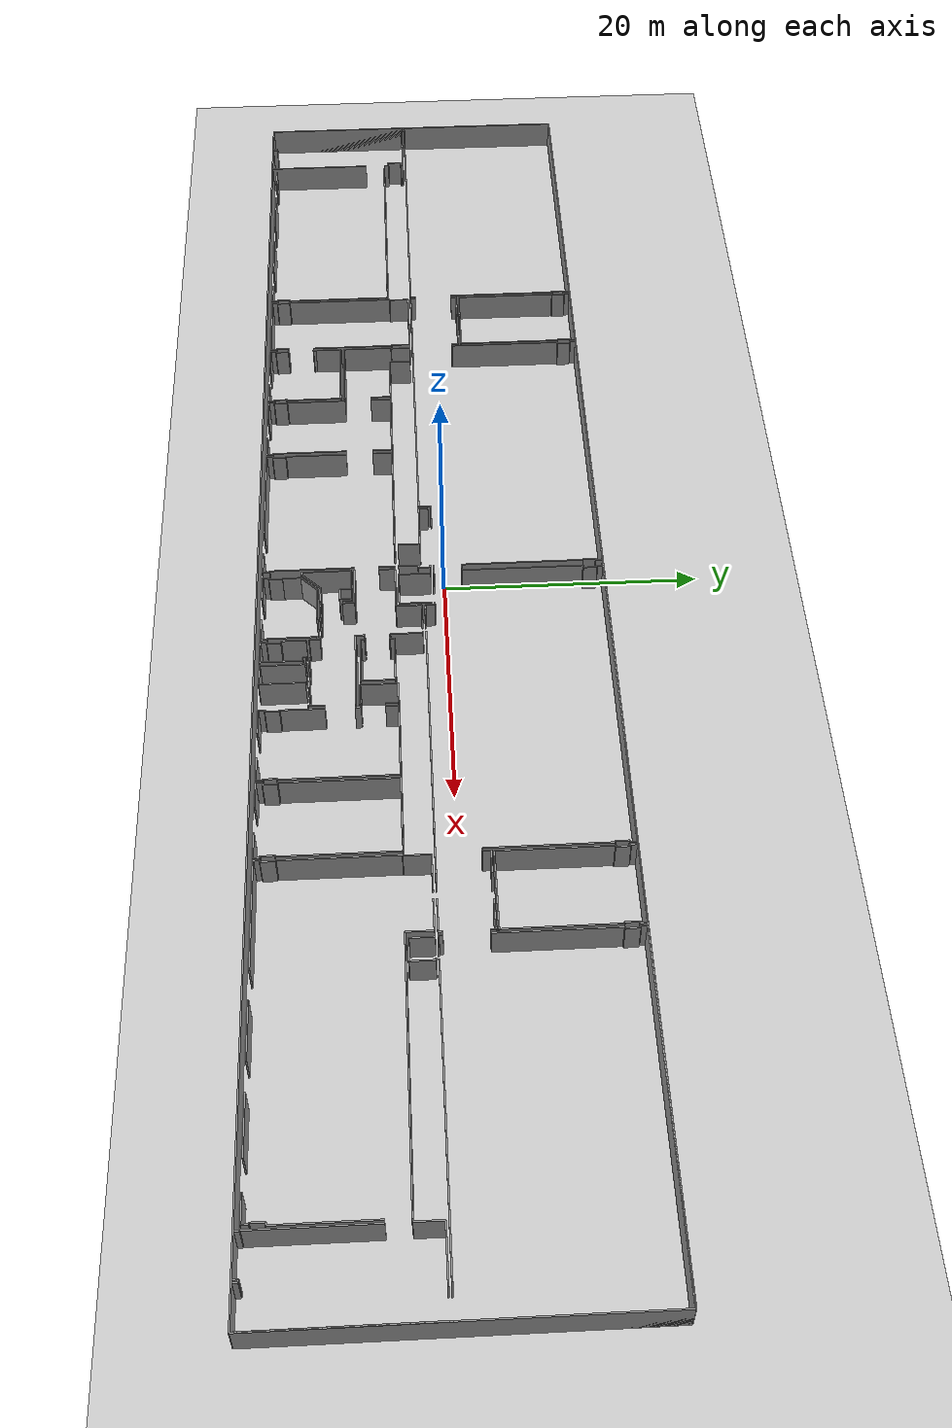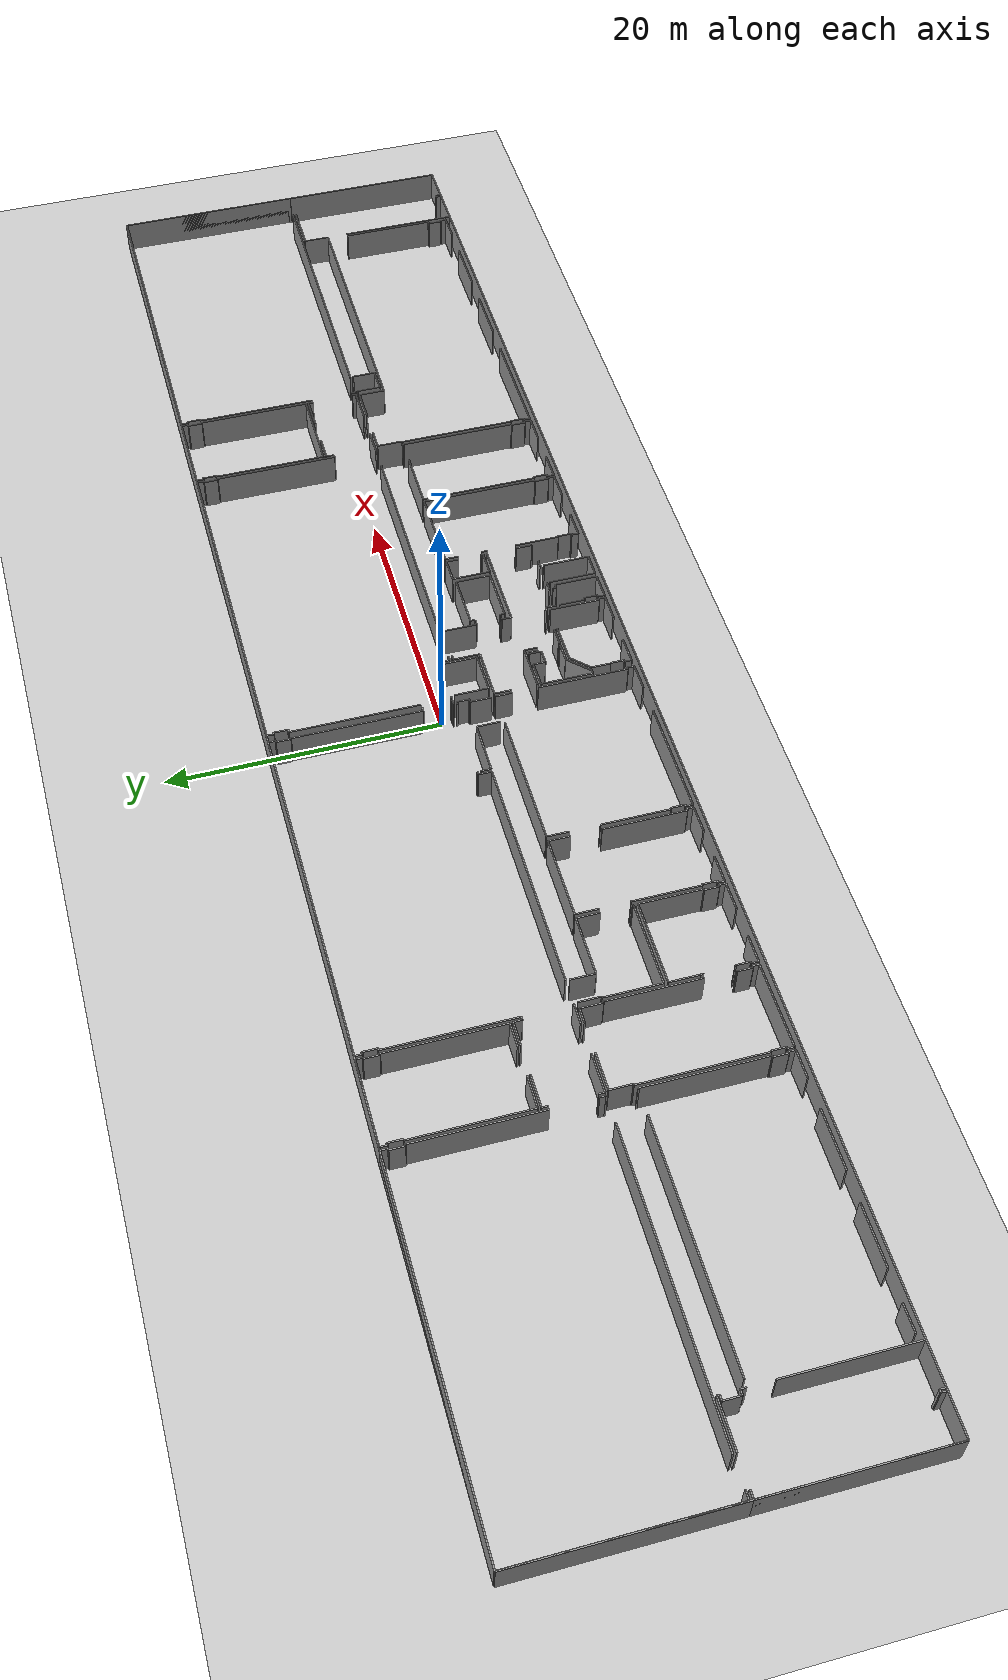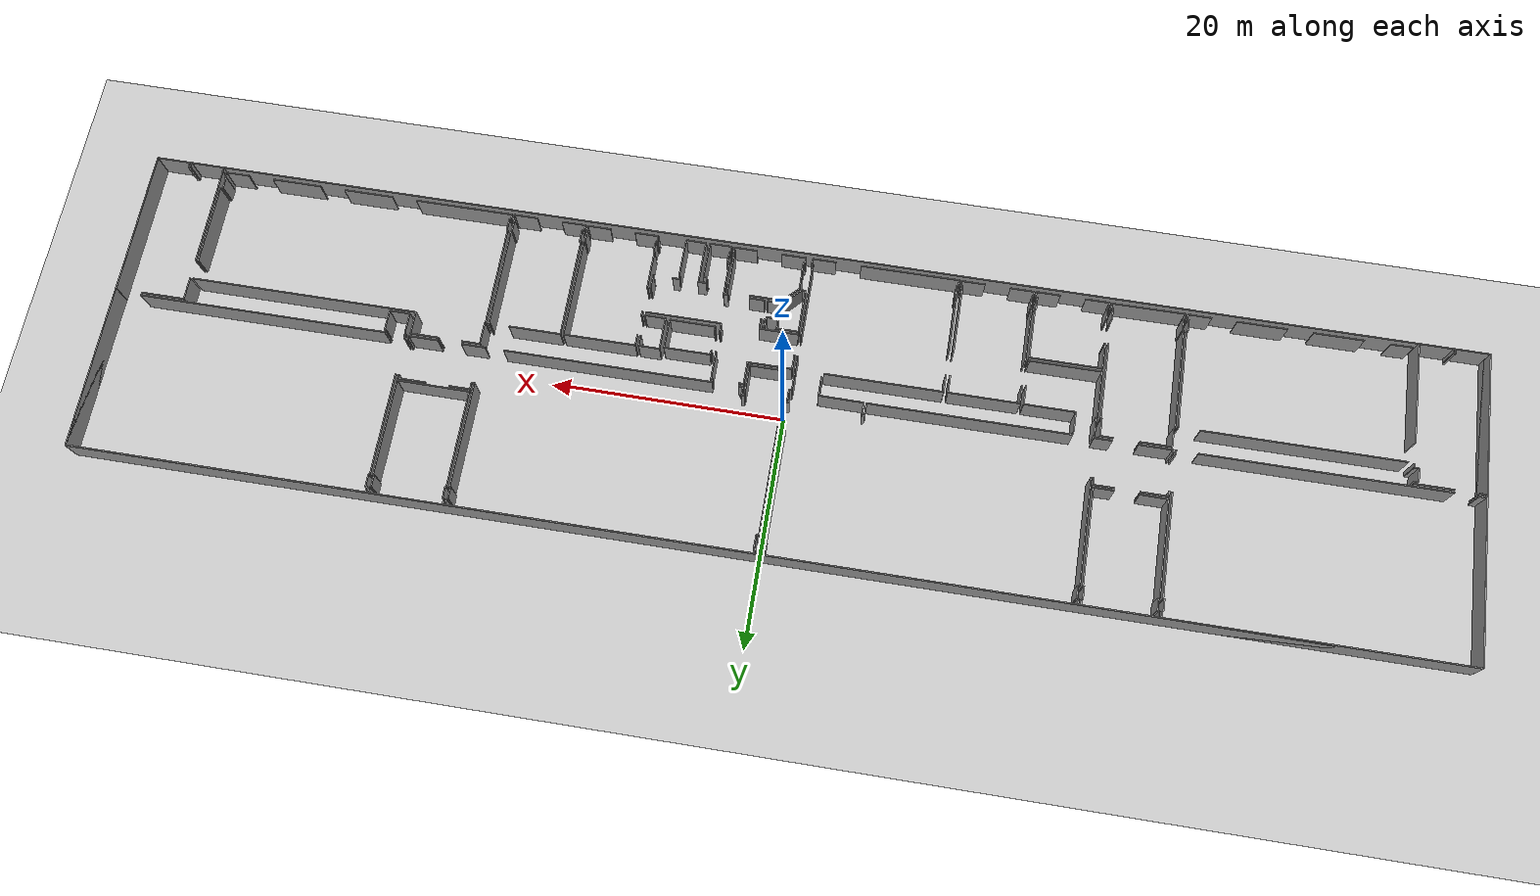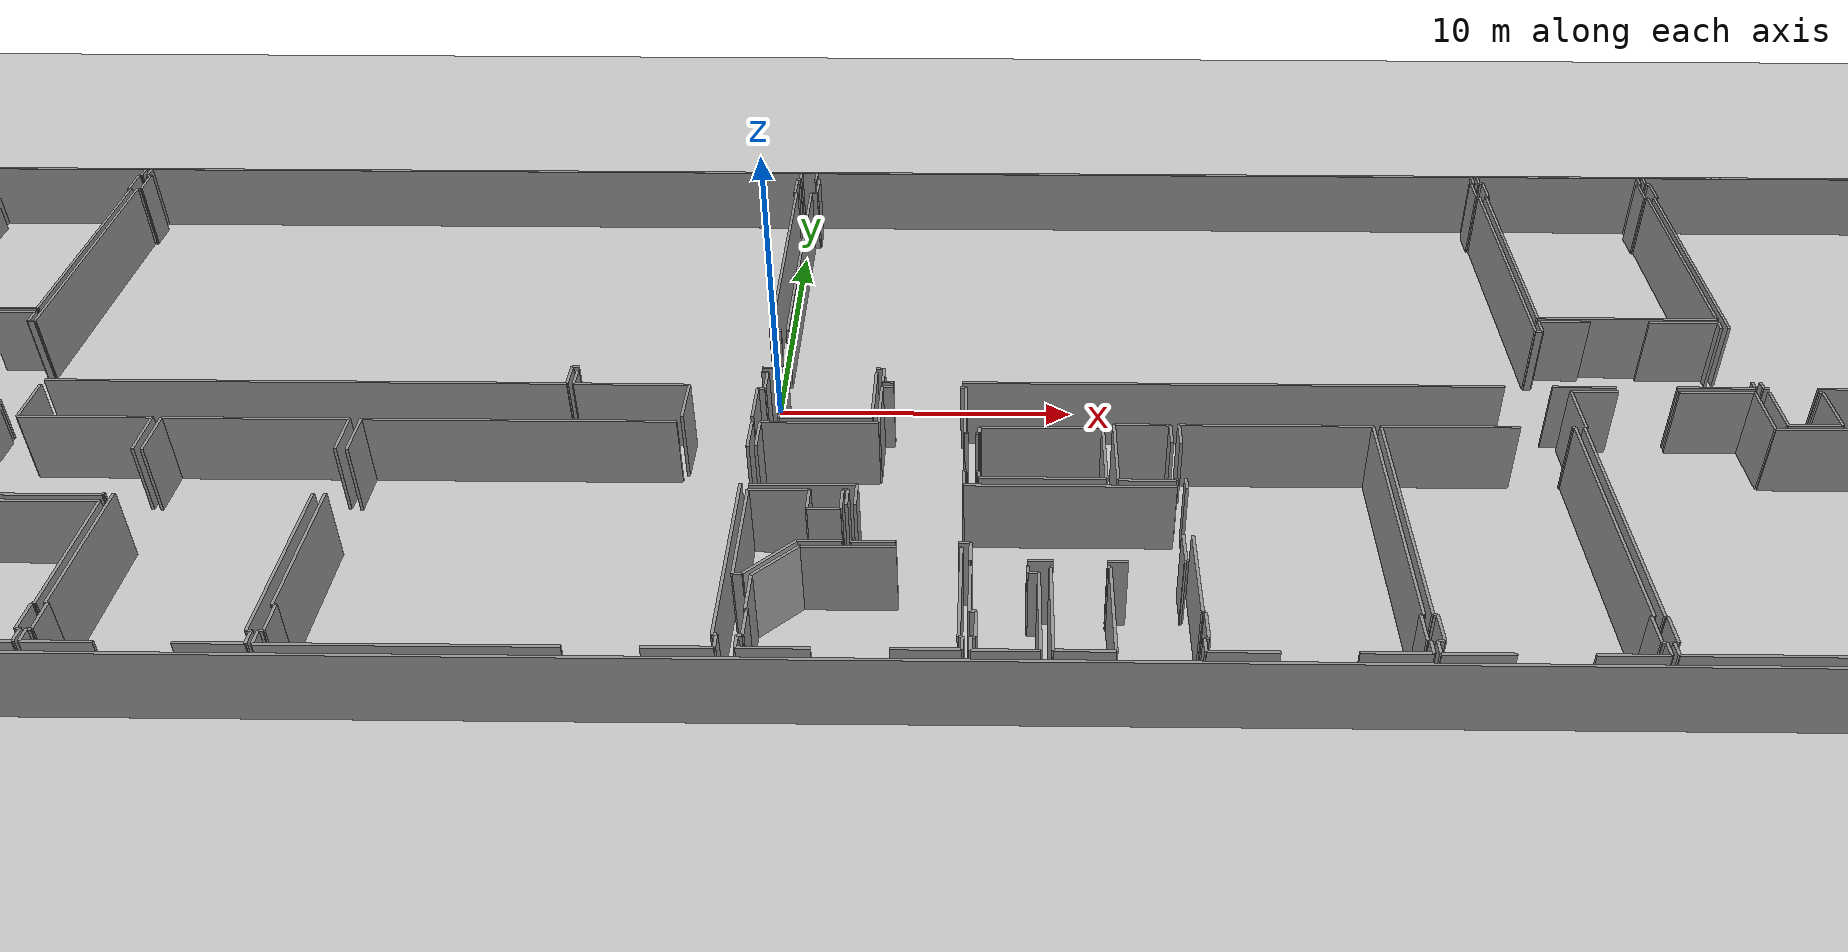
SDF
<sdf version="1.6">
  <world name="default">
    <light name="sun" type="directional">
      <cast_shadows>1</cast_shadows>
      <pose frame="">0 0 10 0 -0 0</pose>
      <diffuse>0.8 0.8 0.8 1</diffuse>
      <specular>0.1 0.1 0.1 1</specular>
      <attenuation>
        <range>1000</range>
        <constant>0.9</constant>
        <linear>0.01</linear>
        <quadratic>0.001</quadratic>
      </attenuation>
      <direction>-0.5 0.5 -1</direction>
    </light>
    <model name="ground_plane">
      <static>1</static>
      <link name="link">
        <collision name="collision">
          <geometry>
            <plane>
              <normal>0 0 1</normal>
              <size>100 100</size>
            </plane>
          </geometry>
          <surface>
            <friction>
              <ode>
                <mu>100</mu>
                <mu2>50</mu2>
              </ode>
              <torsional>
                <ode />
              </torsional>
            </friction>
            <contact>
              <ode />
            </contact>
            <bounce />
          </surface>
          <max_contacts>10</max_contacts>
        </collision>
        <visual name="visual">
          <cast_shadows>0</cast_shadows>
          <geometry>
            <plane>
              <normal>0 0 1</normal>
              <size>100 100</size>
            </plane>
          </geometry>
          <material>
            <script>
              <uri>file://media/materials/scripts/gazebo.material</uri>
              <name>Gazebo/Grey</name>
            </script>
          </material>
        </visual>
        <self_collide>0</self_collide>
        <kinematic>0</kinematic>
        <gravity>1</gravity>
      </link>
    </model>
    <gravity>0 0 -9.8</gravity>
    <magnetic_field>6e-06 2.3e-05 -4.2e-05</magnetic_field>
    <atmosphere type="adiabatic" />
    <physics default="0" name="default_physics" type="ode">
      <max_step_size>0.001</max_step_size>
      <real_time_factor>1</real_time_factor>
      <real_time_update_rate>1000</real_time_update_rate>
    </physics>
    <scene>
      <ambient>0.4 0.4 0.4 1</ambient>
      <background>0.7 0.7 0.7 1</background>
      <shadows>1</shadows>
    </scene>
    <spherical_coordinates>
      <surface_model>EARTH_WGS84</surface_model>
      <latitude_deg>0</latitude_deg>
      <longitude_deg>0</longitude_deg>
      <elevation>0</elevation>
      <heading_deg>0</heading_deg>
    </spherical_coordinates>
  <model name="0510040946_A-40">
		<static>1</static>
		<link name="Wall_0">
			<collision name="Wall_0_Collision">
				<geometry>
					<box>
						<size>14.3027451378 0.1 2.5</size>
					</box>
				</geometry>
				<pose frame="">7.15137256891 0 1.25 0 0 0</pose>
			</collision>
			<visual name="Wall_0_Visual">
				<pose frame="">7.15137256891 0 1.25 0 0 0</pose>
				<geometry>
					<box>
						<size>14.3027451378 0.1 2.5</size>
					</box>
				</geometry>
				<material>
					<script>
						<uri>file://media/materials/scripts/gazebo.material</uri>
						<name>Gazebo/Grey</name>
					</script>
					<ambient>1 1 1 1</ambient>
				</material>
			</visual>
			<pose frame="">0.0110338180181 -14.3027451378 0 0 0 1.57079632679</pose>
		</link>
		<link name="Wall_1">
			<collision name="Wall_1_Collision">
				<geometry>
					<box>
						<size>25.5827314407 0.1 2.5</size>
					</box>
				</geometry>
				<pose frame="">12.7913657203 0 1.25 0 0 0</pose>
			</collision>
			<visual name="Wall_1_Visual">
				<pose frame="">12.7913657203 0 1.25 0 0 0</pose>
				<geometry>
					<box>
						<size>25.5827314407 0.1 2.5</size>
					</box>
				</geometry>
				<material>
					<script>
						<uri>file://media/materials/scripts/gazebo.material</uri>
						<name>Gazebo/Grey</name>
					</script>
					<ambient>1 1 1 1</ambient>
				</material>
			</visual>
			<pose frame="">0.0110338180181 -0.0 0 0 0 0.0</pose>
		</link>
		<link name="Wall_2">
			<collision name="Wall_2_Collision">
				<geometry>
					<box>
						<size>0.525564849046 0.1 2.5</size>
					</box>
				</geometry>
				<pose frame="">0.262782424523 0 1.25 0 0 0</pose>
			</collision>
			<visual name="Wall_2_Visual">
				<pose frame="">0.262782424523 0 1.25 0 0 0</pose>
				<geometry>
					<box>
						<size>0.525564849046 0.1 2.5</size>
					</box>
				</geometry>
				<material>
					<script>
						<uri>file://media/materials/scripts/gazebo.material</uri>
						<name>Gazebo/Grey</name>
					</script>
					<ambient>1 1 1 1</ambient>
				</material>
			</visual>
			<pose frame="">25.5937652587 -0.0 0 0 0 -1.57079632679</pose>
		</link>
		<link name="Wall_3">
			<collision name="Wall_3_Collision">
				<geometry>
					<box>
						<size>0.108435797764 0.1 2.5</size>
					</box>
				</geometry>
				<pose frame="">0.054217898882 0 1.25 0 0 0</pose>
			</collision>
			<visual name="Wall_3_Visual">
				<pose frame="">0.054217898882 0 1.25 0 0 0</pose>
				<geometry>
					<box>
						<size>0.108435797764 0.1 2.5</size>
					</box>
				</geometry>
				<material>
					<script>
						<uri>file://media/materials/scripts/gazebo.material</uri>
						<name>Gazebo/Grey</name>
					</script>
					<ambient>1 1 1 1</ambient>
				</material>
			</visual>
			<pose frame="">25.5937652587 -0.525564849046 0 0 0 3.14159265359</pose>
		</link>
		<link name="Wall_4">
			<collision name="Wall_4_Collision">
				<geometry>
					<box>
						<size>1.04237873897 0.1 2.5</size>
					</box>
				</geometry>
				<pose frame="">0.521189369487 0 1.25 0 0 0</pose>
			</collision>
			<visual name="Wall_4_Visual">
				<pose frame="">0.521189369487 0 1.25 0 0 0</pose>
				<geometry>
					<box>
						<size>1.04237873897 0.1 2.5</size>
					</box>
				</geometry>
				<material>
					<script>
						<uri>file://media/materials/scripts/gazebo.material</uri>
						<name>Gazebo/Grey</name>
					</script>
					<ambient>1 1 1 1</ambient>
				</material>
			</visual>
			<pose frame="">25.4853294609 -0.525564849046 0 0 0 -1.57079632679</pose>
		</link>
		<link name="Wall_5">
			<collision name="Wall_5_Collision">
				<geometry>
					<box>
						<size>0.108435797764 0.1 2.5</size>
					</box>
				</geometry>
				<pose frame="">0.054217898882 0 1.25 0 0 0</pose>
			</collision>
			<visual name="Wall_5_Visual">
				<pose frame="">0.054217898882 0 1.25 0 0 0</pose>
				<geometry>
					<box>
						<size>0.108435797764 0.1 2.5</size>
					</box>
				</geometry>
				<material>
					<script>
						<uri>file://media/materials/scripts/gazebo.material</uri>
						<name>Gazebo/Grey</name>
					</script>
					<ambient>1 1 1 1</ambient>
				</material>
			</visual>
			<pose frame="">25.4853294609 -1.56794358802 0 0 0 0.0</pose>
		</link>
		<link name="Wall_6">
			<collision name="Wall_6_Collision">
				<geometry>
					<box>
						<size>9.08780763109 0.1 2.5</size>
					</box>
				</geometry>
				<pose frame="">4.54390381555 0 1.25 0 0 0</pose>
			</collision>
			<visual name="Wall_6_Visual">
				<pose frame="">4.54390381555 0 1.25 0 0 0</pose>
				<geometry>
					<box>
						<size>9.08780763109 0.1 2.5</size>
					</box>
				</geometry>
				<material>
					<script>
						<uri>file://media/materials/scripts/gazebo.material</uri>
						<name>Gazebo/Grey</name>
					</script>
					<ambient>1 1 1 1</ambient>
				</material>
			</visual>
			<pose frame="">25.5937652587 -1.56794358802 0 0 0 -1.57079632679</pose>
		</link>
		<link name="Wall_7">
			<collision name="Wall_7_Collision">
				<geometry>
					<box>
						<size>0.433616365562 0.1 2.5</size>
					</box>
				</geometry>
				<pose frame="">0.216808182781 0 1.25 0 0 0</pose>
			</collision>
			<visual name="Wall_7_Visual">
				<pose frame="">0.216808182781 0 1.25 0 0 0</pose>
				<geometry>
					<box>
						<size>0.433616365562 0.1 2.5</size>
					</box>
				</geometry>
				<material>
					<script>
						<uri>file://media/materials/scripts/gazebo.material</uri>
						<name>Gazebo/Grey</name>
					</script>
					<ambient>1 1 1 1</ambient>
				</material>
			</visual>
			<pose frame="">25.5937652587 -13.8679873428 0 0 0 -1.57079632679</pose>
		</link>
		<link name="Wall_8">
			<collision name="Wall_8_Collision">
				<geometry>
					<box>
						<size>0.0667102100864 0.1 2.5</size>
					</box>
				</geometry>
				<pose frame="">0.0333551050432 0 1.25 0 0 0</pose>
			</collision>
			<visual name="Wall_8_Visual">
				<pose frame="">0.0333551050432 0 1.25 0 0 0</pose>
				<geometry>
					<box>
						<size>0.0667102100864 0.1 2.5</size>
					</box>
				</geometry>
				<material>
					<script>
						<uri>file://media/materials/scripts/gazebo.material</uri>
						<name>Gazebo/Grey</name>
					</script>
					<ambient>1 1 1 1</ambient>
				</material>
			</visual>
			<pose frame="">25.5937652587 -14.3016037084 0 0 0 3.14159265359</pose>
		</link>
		<link name="Wall_9">
			<collision name="Wall_9_Collision">
				<geometry>
					<box>
						<size>21.0861335346 0.1 2.5</size>
					</box>
				</geometry>
				<pose frame="">10.5430667673 0 1.25 0 0 0</pose>
			</collision>
			<visual name="Wall_9_Visual">
				<pose frame="">10.5430667673 0 1.25 0 0 0</pose>
				<geometry>
					<box>
						<size>21.0861335346 0.1 2.5</size>
					</box>
				</geometry>
				<material>
					<script>
						<uri>file://media/materials/scripts/gazebo.material</uri>
						<name>Gazebo/Grey</name>
					</script>
					<ambient>1 1 1 1</ambient>
				</material>
			</visual>
			<pose frame="">23.7249915978 -14.3016037084 0 0 0 3.14159265359</pose>
		</link>
		<link name="Wall_10">
			<collision name="Wall_10_Collision">
				<geometry>
					<box>
						<size>0.62867501224 0.1 2.5</size>
					</box>
				</geometry>
				<pose frame="">0.31433750612 0 1.25 0 0 0</pose>
			</collision>
			<visual name="Wall_10_Visual">
				<pose frame="">0.31433750612 0 1.25 0 0 0</pose>
				<geometry>
					<box>
						<size>0.62867501224 0.1 2.5</size>
					</box>
				</geometry>
				<material>
					<script>
						<uri>file://media/materials/scripts/gazebo.material</uri>
						<name>Gazebo/Grey</name>
					</script>
					<ambient>1 1 1 1</ambient>
				</material>
			</visual>
			<pose frame="">0.639707794061 -14.3016037084 0 0 0 -3.1397770413</pose>
		</link>
		<link name="Wall_11">
			<collision name="Wall_11_Collision">
				<geometry>
					<box>
						<size>12.5573726831 0.1 2.5</size>
					</box>
				</geometry>
				<pose frame="">6.27868634153 0 1.25 0 0 0</pose>
			</collision>
			<visual name="Wall_11_Visual">
				<pose frame="">6.27868634153 0 1.25 0 0 0</pose>
				<geometry>
					<box>
						<size>12.5573726831 0.1 2.5</size>
					</box>
				</geometry>
				<material>
					<script>
						<uri>file://media/materials/scripts/gazebo.material</uri>
						<name>Gazebo/Grey</name>
					</script>
					<ambient>1 1 1 1</ambient>
				</material>
			</visual>
			<pose frame="">0.0 -27.1080616626 0 0 0 1.57079632679</pose>
		</link>
		<link name="Wall_12">
			<collision name="Wall_12_Collision">
				<geometry>
					<box>
						<size>0.594557918033 0.1 2.5</size>
					</box>
				</geometry>
				<pose frame="">0.297278959016 0 1.25 0 0 0</pose>
			</collision>
			<visual name="Wall_12_Visual">
				<pose frame="">0.297278959016 0 1.25 0 0 0</pose>
				<geometry>
					<box>
						<size>0.594557918033 0.1 2.5</size>
					</box>
				</geometry>
				<material>
					<script>
						<uri>file://media/materials/scripts/gazebo.material</uri>
						<name>Gazebo/Grey</name>
					</script>
					<ambient>1 1 1 1</ambient>
				</material>
			</visual>
			<pose frame="">0.0 -14.5506889795 0 0 0 0.0</pose>
		</link>
		<link name="Wall_13">
			<collision name="Wall_13_Collision">
				<geometry>
					<box>
						<size>3.36062195222 0.1 2.5</size>
					</box>
				</geometry>
				<pose frame="">1.68031097611 0 1.25 0 0 0</pose>
			</collision>
			<visual name="Wall_13_Visual">
				<pose frame="">1.68031097611 0 1.25 0 0 0</pose>
				<geometry>
					<box>
						<size>3.36062195222 0.1 2.5</size>
					</box>
				</geometry>
				<material>
					<script>
						<uri>file://media/materials/scripts/gazebo.material</uri>
						<name>Gazebo/Grey</name>
					</script>
					<ambient>1 1 1 1</ambient>
				</material>
			</visual>
			<pose frame="">2.63657520435 -14.5506889795 0 0 0 0.0</pose>
		</link>
		<link name="Wall_14">
			<collision name="Wall_14_Collision">
				<geometry>
					<box>
						<size>0.167790129172 0.1 2.5</size>
					</box>
				</geometry>
				<pose frame="">0.0838950645859 0 1.25 0 0 0</pose>
			</collision>
			<visual name="Wall_14_Visual">
				<pose frame="">0.0838950645859 0 1.25 0 0 0</pose>
				<geometry>
					<box>
						<size>0.167790129172 0.1 2.5</size>
					</box>
				</geometry>
				<material>
					<script>
						<uri>file://media/materials/scripts/gazebo.material</uri>
						<name>Gazebo/Grey</name>
					</script>
					<ambient>1 1 1 1</ambient>
				</material>
			</visual>
			<pose frame="">5.99719715657 -14.5506889795 0 0 0 -1.57079632679</pose>
		</link>
		<link name="Wall_15">
			<collision name="Wall_15_Collision">
				<geometry>
					<box>
						<size>0.36703298097 0.1 2.5</size>
					</box>
				</geometry>
				<pose frame="">0.183516490485 0 1.25 0 0 0</pose>
			</collision>
			<visual name="Wall_15_Visual">
				<pose frame="">0.183516490485 0 1.25 0 0 0</pose>
				<geometry>
					<box>
						<size>0.36703298097 0.1 2.5</size>
					</box>
				</geometry>
				<material>
					<script>
						<uri>file://media/materials/scripts/gazebo.material</uri>
						<name>Gazebo/Grey</name>
					</script>
					<ambient>1 1 1 1</ambient>
				</material>
			</visual>
			<pose frame="">5.99719715657 -14.7184791087 0 0 0 3.14159265359</pose>
		</link>
		<link name="Wall_16">
			<collision name="Wall_16_Collision">
				<geometry>
					<box>
						<size>1.22589522946 0.1 2.5</size>
					</box>
				</geometry>
				<pose frame="">0.61294761473 0 1.25 0 0 0</pose>
			</collision>
			<visual name="Wall_16_Visual">
				<pose frame="">0.61294761473 0 1.25 0 0 0</pose>
				<geometry>
					<box>
						<size>1.22589522946 0.1 2.5</size>
					</box>
				</geometry>
				<material>
					<script>
						<uri>file://media/materials/scripts/gazebo.material</uri>
						<name>Gazebo/Grey</name>
					</script>
					<ambient>1 1 1 1</ambient>
				</material>
			</visual>
			<pose frame="">5.6301641756 -14.7184791087 0 0 0 -1.57079632679</pose>
		</link>
		<link name="Wall_17">
			<collision name="Wall_17_Collision">
				<geometry>
					<box>
						<size>0.375022987121 0.1 2.5</size>
					</box>
				</geometry>
				<pose frame="">0.18751149356 0 1.25 0 0 0</pose>
			</collision>
			<visual name="Wall_17_Visual">
				<pose frame="">0.18751149356 0 1.25 0 0 0</pose>
				<geometry>
					<box>
						<size>0.375022987121 0.1 2.5</size>
					</box>
				</geometry>
				<material>
					<script>
						<uri>file://media/materials/scripts/gazebo.material</uri>
						<name>Gazebo/Grey</name>
					</script>
					<ambient>1 1 1 1</ambient>
				</material>
			</visual>
			<pose frame="">5.6301641756 -15.9443743381 0 0 0 0.0</pose>
		</link>
		<link name="Wall_18">
			<collision name="Wall_18_Collision">
				<geometry>
					<box>
						<size>0.37984235591 0.1 2.5</size>
					</box>
				</geometry>
				<pose frame="">0.189921177955 0 1.25 0 0 0</pose>
			</collision>
			<visual name="Wall_18_Visual">
				<pose frame="">0.189921177955 0 1.25 0 0 0</pose>
				<geometry>
					<box>
						<size>0.37984235591 0.1 2.5</size>
					</box>
				</geometry>
				<material>
					<script>
						<uri>file://media/materials/scripts/gazebo.material</uri>
						<name>Gazebo/Grey</name>
					</script>
					<ambient>1 1 1 1</ambient>
				</material>
			</visual>
			<pose frame="">6.00518716272 -15.9443743381 0 0 0 -1.57079632679</pose>
		</link>
		<link name="Wall_19">
			<collision name="Wall_19_Collision">
				<geometry>
					<box>
						<size>9.00410280475 0.1 2.5</size>
					</box>
				</geometry>
				<pose frame="">4.50205140237 0 1.25 0 0 0</pose>
			</collision>
			<visual name="Wall_19_Visual">
				<pose frame="">4.50205140237 0 1.25 0 0 0</pose>
				<geometry>
					<box>
						<size>9.00410280475 0.1 2.5</size>
					</box>
				</geometry>
				<material>
					<script>
						<uri>file://media/materials/scripts/gazebo.material</uri>
						<name>Gazebo/Grey</name>
					</script>
					<ambient>1 1 1 1</ambient>
				</material>
			</visual>
			<pose frame="">6.00518716272 -18.0874715435 0 0 0 -1.57079632679</pose>
		</link>
		<link name="Wall_20">
			<collision name="Wall_20_Collision">
				<geometry>
					<box>
						<size>0.390876173928 0.1 2.5</size>
					</box>
				</geometry>
				<pose frame="">0.195438086964 0 1.25 0 0 0</pose>
			</collision>
			<visual name="Wall_20_Visual">
				<pose frame="">0.195438086964 0 1.25 0 0 0</pose>
				<geometry>
					<box>
						<size>0.390876173928 0.1 2.5</size>
					</box>
				</geometry>
				<material>
					<script>
						<uri>file://media/materials/scripts/gazebo.material</uri>
						<name>Gazebo/Grey</name>
					</script>
					<ambient>1 1 1 1</ambient>
				</material>
			</visual>
			<pose frame="">3.09251285693 -27.0915743483 0 0 0 1.57079632679</pose>
		</link>
		<link name="Wall_21">
			<collision name="Wall_21_Collision">
				<geometry>
					<box>
						<size>0.17654108829 0.1 2.5</size>
					</box>
				</geometry>
				<pose frame="">0.0882705441448 0 1.25 0 0 0</pose>
			</collision>
			<visual name="Wall_21_Visual">
				<pose frame="">0.0882705441448 0 1.25 0 0 0</pose>
				<geometry>
					<box>
						<size>0.17654108829 0.1 2.5</size>
					</box>
				</geometry>
				<material>
					<script>
						<uri>file://media/materials/scripts/gazebo.material</uri>
						<name>Gazebo/Grey</name>
					</script>
					<ambient>1 1 1 1</ambient>
				</material>
			</visual>
			<pose frame="">3.09251285693 -26.7006981743 0 0 0 3.14159265359</pose>
		</link>
		<link name="Wall_22">
			<collision name="Wall_22_Collision">
				<geometry>
					<box>
						<size>0.397217448652 0.1 2.5</size>
					</box>
				</geometry>
				<pose frame="">0.198608724326 0 1.25 0 0 0</pose>
			</collision>
			<visual name="Wall_22_Visual">
				<pose frame="">0.198608724326 0 1.25 0 0 0</pose>
				<geometry>
					<box>
						<size>0.397217448652 0.1 2.5</size>
					</box>
				</geometry>
				<material>
					<script>
						<uri>file://media/materials/scripts/gazebo.material</uri>
						<name>Gazebo/Grey</name>
					</script>
					<ambient>1 1 1 1</ambient>
				</material>
			</visual>
			<pose frame="">2.91597176864 -26.7006981743 0 0 0 -1.57079632679</pose>
		</link>
		<link name="Wall_23">
			<collision name="Wall_23_Collision">
				<geometry>
					<box>
						<size>17.241165019 0.1 2.5</size>
					</box>
				</geometry>
				<pose frame="">8.6205825095 0 1.25 0 0 0</pose>
			</collision>
			<visual name="Wall_23_Visual">
				<pose frame="">8.6205825095 0 1.25 0 0 0</pose>
				<geometry>
					<box>
						<size>17.241165019 0.1 2.5</size>
					</box>
				</geometry>
				<material>
					<script>
						<uri>file://media/materials/scripts/gazebo.material</uri>
						<name>Gazebo/Grey</name>
					</script>
					<ambient>1 1 1 1</ambient>
				</material>
			</visual>
			<pose frame="">6.48052911596 -16.3597278325 0 0 0 0.0</pose>
		</link>
		<link name="Wall_24">
			<collision name="Wall_24_Collision">
				<geometry>
					<box>
						<size>0.0834511753553 0.1 2.5</size>
					</box>
				</geometry>
				<pose frame="">0.0417255876776 0 1.25 0 0 0</pose>
			</collision>
			<visual name="Wall_24_Visual">
				<pose frame="">0.0417255876776 0 1.25 0 0 0</pose>
				<geometry>
					<box>
						<size>0.0834511753553 0.1 2.5</size>
					</box>
				</geometry>
				<material>
					<script>
						<uri>file://media/materials/scripts/gazebo.material</uri>
						<name>Gazebo/Grey</name>
					</script>
					<ambient>1 1 1 1</ambient>
				</material>
			</visual>
			<pose frame="">25.5103140833 -16.3597278325 0 0 0 0.0</pose>
		</link>
		<link name="Wall_25">
			<collision name="Wall_25_Collision">
				<geometry>
					<box>
						<size>8.75197372176 0.1 2.5</size>
					</box>
				</geometry>
				<pose frame="">4.37598686088 0 1.25 0 0 0</pose>
			</collision>
			<visual name="Wall_25_Visual">
				<pose frame="">4.37598686088 0 1.25 0 0 0</pose>
				<geometry>
					<box>
						<size>8.75197372176 0.1 2.5</size>
					</box>
				</geometry>
				<material>
					<script>
						<uri>file://media/materials/scripts/gazebo.material</uri>
						<name>Gazebo/Grey</name>
					</script>
					<ambient>1 1 1 1</ambient>
				</material>
			</visual>
			<pose frame="">25.5937652587 -16.3597278325 0 0 0 -1.57079632679</pose>
		</link>
		<link name="Wall_26">
			<collision name="Wall_26_Collision">
				<geometry>
					<box>
						<size>0.104250556447 0.1 2.5</size>
					</box>
				</geometry>
				<pose frame="">0.0521252782234 0 1.25 0 0 0</pose>
			</collision>
			<visual name="Wall_26_Visual">
				<pose frame="">0.0521252782234 0 1.25 0 0 0</pose>
				<geometry>
					<box>
						<size>0.104250556447 0.1 2.5</size>
					</box>
				</geometry>
				<material>
					<script>
						<uri>file://media/materials/scripts/gazebo.material</uri>
						<name>Gazebo/Grey</name>
					</script>
					<ambient>1 1 1 1</ambient>
				</material>
			</visual>
			<pose frame="">25.5937652587 -25.1117015542 0 0 0 3.14159265359</pose>
		</link>
		<link name="Wall_27">
			<collision name="Wall_27_Collision">
				<geometry>
					<box>
						<size>1.06799748886 0.1 2.5</size>
					</box>
				</geometry>
				<pose frame="">0.533998744428 0 1.25 0 0 0</pose>
			</collision>
			<visual name="Wall_27_Visual">
				<pose frame="">0.533998744428 0 1.25 0 0 0</pose>
				<geometry>
					<box>
						<size>1.06799748886 0.1 2.5</size>
					</box>
				</geometry>
				<material>
					<script>
						<uri>file://media/materials/scripts/gazebo.material</uri>
						<name>Gazebo/Grey</name>
					</script>
					<ambient>1 1 1 1</ambient>
				</material>
			</visual>
			<pose frame="">25.4895147022 -25.1117015542 0 0 0 -1.57079632679</pose>
		</link>
		<link name="Wall_28">
			<collision name="Wall_28_Collision">
				<geometry>
					<box>
						<size>0.110084529192 0.1 2.5</size>
					</box>
				</geometry>
				<pose frame="">0.055042264596 0 1.25 0 0 0</pose>
			</collision>
			<visual name="Wall_28_Visual">
				<pose frame="">0.055042264596 0 1.25 0 0 0</pose>
				<geometry>
					<box>
						<size>0.110084529192 0.1 2.5</size>
					</box>
				</geometry>
				<material>
					<script>
						<uri>file://media/materials/scripts/gazebo.material</uri>
						<name>Gazebo/Grey</name>
					</script>
					<ambient>1 1 1 1</ambient>
				</material>
			</visual>
			<pose frame="">25.4895147022 -26.1796990431 0 0 0 0.0</pose>
		</link>
		<link name="Wall_29">
			<collision name="Wall_29_Collision">
				<geometry>
					<box>
						<size>0.491195140047 0.1 2.5</size>
					</box>
				</geometry>
				<pose frame="">0.245597570024 0 1.25 0 0 0</pose>
			</collision>
			<visual name="Wall_29_Visual">
				<pose frame="">0.245597570024 0 1.25 0 0 0</pose>
				<geometry>
					<box>
						<size>0.491195140047 0.1 2.5</size>
					</box>
				</geometry>
				<material>
					<script>
						<uri>file://media/materials/scripts/gazebo.material</uri>
						<name>Gazebo/Grey</name>
					</script>
					<ambient>1 1 1 1</ambient>
				</material>
			</visual>
			<pose frame="">25.5995992314 -26.1796990431 0 0 0 -1.57079632679</pose>
		</link>
		<link name="Wall_30">
			<collision name="Wall_30_Collision">
				<geometry>
					<box>
						<size>2.06928476762 0.1 2.5</size>
					</box>
				</geometry>
				<pose frame="">1.03464238381 0 1.25 0 0 0</pose>
			</collision>
			<visual name="Wall_30_Visual">
				<pose frame="">1.03464238381 0 1.25 0 0 0</pose>
				<geometry>
					<box>
						<size>2.06928476762 0.1 2.5</size>
					</box>
				</geometry>
				<material>
					<script>
						<uri>file://media/materials/scripts/gazebo.material</uri>
						<name>Gazebo/Grey</name>
					</script>
					<ambient>1 1 1 1</ambient>
				</material>
			</visual>
			<pose frame="">25.5995992314 -26.6708941831 0 0 0 3.14159265359</pose>
		</link>
		<link name="Wall_31">
			<collision name="Wall_31_Collision">
				<geometry>
					<box>
						<size>4.30179394662 0.1 2.5</size>
					</box>
				</geometry>
				<pose frame="">2.15089697331 0 1.25 0 0 0</pose>
			</collision>
			<visual name="Wall_31_Visual">
				<pose frame="">2.15089697331 0 1.25 0 0 0</pose>
				<geometry>
					<box>
						<size>4.30179394662 0.1 2.5</size>
					</box>
				</geometry>
				<material>
					<script>
						<uri>file://media/materials/scripts/gazebo.material</uri>
						<name>Gazebo/Grey</name>
					</script>
					<ambient>1 1 1 1</ambient>
				</material>
			</visual>
			<pose frame="">21.3704762931 -26.6708941831 0 0 0 3.14159265359</pose>
		</link>
		<link name="Wall_32">
			<collision name="Wall_32_Collision">
				<geometry>
					<box>
						<size>4.31282776464 0.1 2.5</size>
					</box>
				</geometry>
				<pose frame="">2.15641388232 0 1.25 0 0 0</pose>
			</collision>
			<visual name="Wall_32_Visual">
				<pose frame="">2.15641388232 0 1.25 0 0 0</pose>
				<geometry>
					<box>
						<size>4.31282776464 0.1 2.5</size>
					</box>
				</geometry>
				<material>
					<script>
						<uri>file://media/materials/scripts/gazebo.material</uri>
						<name>Gazebo/Grey</name>
					</script>
					<ambient>1 1 1 1</ambient>
				</material>
			</visual>
			<pose frame="">14.8899471772 -26.6708941831 0 0 0 3.14159265359</pose>
		</link>
		<link name="Wall_33">
			<collision name="Wall_33_Collision">
				<geometry>
					<box>
						<size>1.89376450904 0.1 2.5</size>
					</box>
				</geometry>
				<pose frame="">0.946882254521 0 1.25 0 0 0</pose>
			</collision>
			<visual name="Wall_33_Visual">
				<pose frame="">0.946882254521 0 1.25 0 0 0</pose>
				<geometry>
					<box>
						<size>1.89376450904 0.1 2.5</size>
					</box>
				</geometry>
				<material>
					<script>
						<uri>file://media/materials/scripts/gazebo.material</uri>
						<name>Gazebo/Grey</name>
					</script>
					<ambient>1 1 1 1</ambient>
				</material>
			</visual>
			<pose frame="">8.38278470738 -26.6708941831 0 0 0 -3.12973867801</pose>
		</link>
		<link name="Wall_34">
			<collision name="Wall_34_Collision">
				<geometry>
					<box>
						<size>0.419031433699 0.1 2.5</size>
					</box>
				</geometry>
				<pose frame="">0.209515716849 0 1.25 0 0 0</pose>
			</collision>
			<visual name="Wall_34_Visual">
				<pose frame="">0.209515716849 0 1.25 0 0 0</pose>
				<geometry>
					<box>
						<size>0.419031433699 0.1 2.5</size>
					</box>
				</geometry>
				<material>
					<script>
						<uri>file://media/materials/scripts/gazebo.material</uri>
						<name>Gazebo/Grey</name>
					</script>
					<ambient>1 1 1 1</ambient>
				</material>
			</visual>
			<pose frame="">25.8424700533 -14.3075645066 0 0 0 1.57079632679</pose>
		</link>
		<link name="Wall_35">
			<collision name="Wall_35_Collision">
				<geometry>
					<box>
						<size>0.452132887753 0.1 2.5</size>
					</box>
				</geometry>
				<pose frame="">0.226066443877 0 1.25 0 0 0</pose>
			</collision>
			<visual name="Wall_35_Visual">
				<pose frame="">0.226066443877 0 1.25 0 0 0</pose>
				<geometry>
					<box>
						<size>0.452132887753 0.1 2.5</size>
					</box>
				</geometry>
				<material>
					<script>
						<uri>file://media/materials/scripts/gazebo.material</uri>
						<name>Gazebo/Grey</name>
					</script>
					<ambient>1 1 1 1</ambient>
				</material>
			</visual>
			<pose frame="">25.8424700533 -10.6792139356 0 0 0 1.57079632679</pose>
		</link>
		<link name="Wall_36">
			<collision name="Wall_36_Collision">
				<geometry>
					<box>
						<size>2.35996880093 0.1 2.5</size>
					</box>
				</geometry>
				<pose frame="">1.17998440046 0 1.25 0 0 0</pose>
			</collision>
			<visual name="Wall_36_Visual">
				<pose frame="">1.17998440046 0 1.25 0 0 0</pose>
				<geometry>
					<box>
						<size>2.35996880093 0.1 2.5</size>
					</box>
				</geometry>
				<material>
					<script>
						<uri>file://media/materials/scripts/gazebo.material</uri>
						<name>Gazebo/Grey</name>
					</script>
					<ambient>1 1 1 1</ambient>
				</material>
			</visual>
			<pose frame="">25.8424700533 -10.2270810478 0 0 0 0.0</pose>
		</link>
		<link name="Wall_37">
			<collision name="Wall_37_Collision">
				<geometry>
					<box>
						<size>1.78189819718 0.1 2.5</size>
					</box>
				</geometry>
				<pose frame="">0.890949098588 0 1.25 0 0 0</pose>
			</collision>
			<visual name="Wall_37_Visual">
				<pose frame="">0.890949098588 0 1.25 0 0 0</pose>
				<geometry>
					<box>
						<size>1.78189819718 0.1 2.5</size>
					</box>
				</geometry>
				<material>
					<script>
						<uri>file://media/materials/scripts/gazebo.material</uri>
						<name>Gazebo/Grey</name>
					</script>
					<ambient>1 1 1 1</ambient>
				</material>
			</visual>
			<pose frame="">30.3195368333 -10.2270810478 0 0 0 0.0</pose>
		</link>
		<link name="Wall_38">
			<collision name="Wall_38_Collision">
				<geometry>
					<box>
						<size>0.59646030045 0.1 2.5</size>
					</box>
				</geometry>
				<pose frame="">0.298230150225 0 1.25 0 0 0</pose>
			</collision>
			<visual name="Wall_38_Visual">
				<pose frame="">0.298230150225 0 1.25 0 0 0</pose>
				<geometry>
					<box>
						<size>0.59646030045 0.1 2.5</size>
					</box>
				</geometry>
				<material>
					<script>
						<uri>file://media/materials/scripts/gazebo.material</uri>
						<name>Gazebo/Grey</name>
					</script>
					<ambient>1 1 1 1</ambient>
				</material>
			</visual>
			<pose frame="">32.1014350305 -10.2270810478 0 0 0 -1.57079632679</pose>
		</link>
		<link name="Wall_39">
			<collision name="Wall_39_Collision">
				<geometry>
					<box>
						<size>0.224734776185 0.1 2.5</size>
					</box>
				</geometry>
				<pose frame="">0.112367388092 0 1.25 0 0 0</pose>
			</collision>
			<visual name="Wall_39_Visual">
				<pose frame="">0.112367388092 0 1.25 0 0 0</pose>
				<geometry>
					<box>
						<size>0.224734776185 0.1 2.5</size>
					</box>
				</geometry>
				<material>
					<script>
						<uri>file://media/materials/scripts/gazebo.material</uri>
						<name>Gazebo/Grey</name>
					</script>
					<ambient>1 1 1 1</ambient>
				</material>
			</visual>
			<pose frame="">32.1014350305 -10.8235413483 0 0 0 0.0</pose>
		</link>
		<link name="Wall_40">
			<collision name="Wall_40_Collision">
				<geometry>
					<box>
						<size>9.24266155983 0.1 2.5</size>
					</box>
				</geometry>
				<pose frame="">4.62133077991 0 1.25 0 0 0</pose>
			</collision>
			<visual name="Wall_40_Visual">
				<pose frame="">4.62133077991 0 1.25 0 0 0</pose>
				<geometry>
					<box>
						<size>9.24266155983 0.1 2.5</size>
					</box>
				</geometry>
				<material>
					<script>
						<uri>file://media/materials/scripts/gazebo.material</uri>
						<name>Gazebo/Grey</name>
					</script>
					<ambient>1 1 1 1</ambient>
				</material>
			</visual>
			<pose frame="">32.3261698067 -10.8235413483 0 0 0 1.57079632679</pose>
		</link>
		<link name="Wall_41">
			<collision name="Wall_41_Collision">
				<geometry>
					<box>
						<size>0.133293594678 0.1 2.5</size>
					</box>
				</geometry>
				<pose frame="">0.0666467973392 0 1.25 0 0 0</pose>
			</collision>
			<visual name="Wall_41_Visual">
				<pose frame="">0.0666467973392 0 1.25 0 0 0</pose>
				<geometry>
					<box>
						<size>0.133293594678 0.1 2.5</size>
					</box>
				</geometry>
				<material>
					<script>
						<uri>file://media/materials/scripts/gazebo.material</uri>
						<name>Gazebo/Grey</name>
					</script>
					<ambient>1 1 1 1</ambient>
				</material>
			</visual>
			<pose frame="">32.3261698067 -1.58087978846 0 0 0 0.0</pose>
		</link>
		<link name="Wall_42">
			<collision name="Wall_42_Collision">
				<geometry>
					<box>
						<size>1.05417350996 0.1 2.5</size>
					</box>
				</geometry>
				<pose frame="">0.527086754979 0 1.25 0 0 0</pose>
			</collision>
			<visual name="Wall_42_Visual">
				<pose frame="">0.527086754979 0 1.25 0 0 0</pose>
				<geometry>
					<box>
						<size>1.05417350996 0.1 2.5</size>
					</box>
				</geometry>
				<material>
					<script>
						<uri>file://media/materials/scripts/gazebo.material</uri>
						<name>Gazebo/Grey</name>
					</script>
					<ambient>1 1 1 1</ambient>
				</material>
			</visual>
			<pose frame="">32.4594634013 -1.58087978846 0 0 0 1.57079632679</pose>
		</link>
		<link name="Wall_43">
			<collision name="Wall_43_Collision">
				<geometry>
					<box>
						<size>0.153712499287 0.1 2.5</size>
					</box>
				</geometry>
				<pose frame="">0.0768562496433 0 1.25 0 0 0</pose>
			</collision>
			<visual name="Wall_43_Visual">
				<pose frame="">0.0768562496433 0 1.25 0 0 0</pose>
				<geometry>
					<box>
						<size>0.153712499287 0.1 2.5</size>
					</box>
				</geometry>
				<material>
					<script>
						<uri>file://media/materials/scripts/gazebo.material</uri>
						<name>Gazebo/Grey</name>
					</script>
					<ambient>1 1 1 1</ambient>
				</material>
			</visual>
			<pose frame="">32.4594634013 -0.526706278496 0 0 0 3.14159265359</pose>
		</link>
		<link name="Wall_44">
			<collision name="Wall_44_Collision">
				<geometry>
					<box>
						<size>0.522140560696 0.1 2.5</size>
					</box>
				</geometry>
				<pose frame="">0.261070280348 0 1.25 0 0 0</pose>
			</collision>
			<visual name="Wall_44_Visual">
				<pose frame="">0.261070280348 0 1.25 0 0 0</pose>
				<geometry>
					<box>
						<size>0.522140560696 0.1 2.5</size>
					</box>
				</geometry>
				<material>
					<script>
						<uri>file://media/materials/scripts/gazebo.material</uri>
						<name>Gazebo/Grey</name>
					</script>
					<ambient>1 1 1 1</ambient>
				</material>
			</visual>
			<pose frame="">32.305750902 -0.526706278496 0 0 0 1.57079632679</pose>
		</link>
		<link name="Wall_45">
			<collision name="Wall_45_Collision">
				<geometry>
					<box>
						<size>25.7516629993 0.1 2.5</size>
					</box>
				</geometry>
				<pose frame="">12.8758314996 0 1.25 0 0 0</pose>
			</collision>
			<visual name="Wall_45_Visual">
				<pose frame="">12.8758314996 0 1.25 0 0 0</pose>
				<geometry>
					<box>
						<size>25.7516629993 0.1 2.5</size>
					</box>
				</geometry>
				<material>
					<script>
						<uri>file://media/materials/scripts/gazebo.material</uri>
						<name>Gazebo/Grey</name>
					</script>
					<ambient>1 1 1 1</ambient>
				</material>
			</visual>
			<pose frame="">32.305750902 -0.00456571780059 0 0 0 0.0</pose>
		</link>
		<link name="Wall_46">
			<collision name="Wall_46_Collision">
				<geometry>
					<box>
						<size>0.52936961388 0.1 2.5</size>
					</box>
				</geometry>
				<pose frame="">0.26468480694 0 1.25 0 0 0</pose>
			</collision>
			<visual name="Wall_46_Visual">
				<pose frame="">0.26468480694 0 1.25 0 0 0</pose>
				<geometry>
					<box>
						<size>0.52936961388 0.1 2.5</size>
					</box>
				</geometry>
				<material>
					<script>
						<uri>file://media/materials/scripts/gazebo.material</uri>
						<name>Gazebo/Grey</name>
					</script>
					<ambient>1 1 1 1</ambient>
				</material>
			</visual>
			<pose frame="">58.0574139013 -0.00456571780059 0 0 0 -1.57079632679</pose>
		</link>
		<link name="Wall_47">
			<collision name="Wall_47_Collision">
				<geometry>
					<box>
						<size>0.116806280398 0.1 2.5</size>
					</box>
				</geometry>
				<pose frame="">0.0584031401992 0 1.25 0 0 0</pose>
			</collision>
			<visual name="Wall_47_Visual">
				<pose frame="">0.0584031401992 0 1.25 0 0 0</pose>
				<geometry>
					<box>
						<size>0.116806280398 0.1 2.5</size>
					</box>
				</geometry>
				<material>
					<script>
						<uri>file://media/materials/scripts/gazebo.material</uri>
						<name>Gazebo/Grey</name>
					</script>
					<ambient>1 1 1 1</ambient>
				</material>
			</visual>
			<pose frame="">58.0574139013 -0.53393533168 0 0 0 3.14159265359</pose>
		</link>
		<link name="Wall_48">
			<collision name="Wall_48_Collision">
				<geometry>
					<box>
						<size>1.04313969194 0.1 2.5</size>
					</box>
				</geometry>
				<pose frame="">0.52156984597 0 1.25 0 0 0</pose>
			</collision>
			<visual name="Wall_48_Visual">
				<pose frame="">0.52156984597 0 1.25 0 0 0</pose>
				<geometry>
					<box>
						<size>1.04313969194 0.1 2.5</size>
					</box>
				</geometry>
				<material>
					<script>
						<uri>file://media/materials/scripts/gazebo.material</uri>
						<name>Gazebo/Grey</name>
					</script>
					<ambient>1 1 1 1</ambient>
				</material>
			</visual>
			<pose frame="">57.9406076209 -0.53393533168 0 0 0 -1.57079632679</pose>
		</link>
		<link name="Wall_49">
			<collision name="Wall_49_Collision">
				<geometry>
					<box>
						<size>0.0630322707471 0.1 2.5</size>
					</box>
				</geometry>
				<pose frame="">0.0315161353735 0 1.25 0 0 0</pose>
			</collision>
			<visual name="Wall_49_Visual">
				<pose frame="">0.0315161353735 0 1.25 0 0 0</pose>
				<geometry>
					<box>
						<size>0.0630322707471 0.1 2.5</size>
					</box>
				</geometry>
				<material>
					<script>
						<uri>file://media/materials/scripts/gazebo.material</uri>
						<name>Gazebo/Grey</name>
					</script>
					<ambient>1 1 1 1</ambient>
				</material>
			</visual>
			<pose frame="">57.9406076209 -1.57707502362 0 0 0 0.0</pose>
		</link>
		<link name="Wall_50">
			<collision name="Wall_50_Collision">
				<geometry>
					<box>
						<size>9.52383368105 0.1 2.5</size>
					</box>
				</geometry>
				<pose frame="">4.76191684052 0 1.25 0 0 0</pose>
			</collision>
			<visual name="Wall_50_Visual">
				<pose frame="">4.76191684052 0 1.25 0 0 0</pose>
				<geometry>
					<box>
						<size>9.52383368105 0.1 2.5</size>
					</box>
				</geometry>
				<material>
					<script>
						<uri>file://media/materials/scripts/gazebo.material</uri>
						<name>Gazebo/Grey</name>
					</script>
					<ambient>1 1 1 1</ambient>
				</material>
			</visual>
			<pose frame="">58.0036398917 -1.57707502362 0 0 0 -1.57079632679</pose>
		</link>
		<link name="Wall_51">
			<collision name="Wall_51_Collision">
				<geometry>
					<box>
						<size>0.356252813941 0.1 2.5</size>
					</box>
				</geometry>
				<pose frame="">0.17812640697 0 1.25 0 0 0</pose>
			</collision>
			<visual name="Wall_51_Visual">
				<pose frame="">0.17812640697 0 1.25 0 0 0</pose>
				<geometry>
					<box>
						<size>0.356252813941 0.1 2.5</size>
					</box>
				</geometry>
				<material>
					<script>
						<uri>file://media/materials/scripts/gazebo.material</uri>
						<name>Gazebo/Grey</name>
					</script>
					<ambient>1 1 1 1</ambient>
				</material>
			</visual>
			<pose frame="">58.0036398917 -11.1009087047 0 0 0 0.0</pose>
		</link>
		<link name="Wall_52">
			<collision name="Wall_52_Collision">
				<geometry>
					<box>
						<size>0.0750806927209 0.1 2.5</size>
					</box>
				</geometry>
				<pose frame="">0.0375403463604 0 1.25 0 0 0</pose>
			</collision>
			<visual name="Wall_52_Visual">
				<pose frame="">0.0375403463604 0 1.25 0 0 0</pose>
				<geometry>
					<box>
						<size>0.0750806927209 0.1 2.5</size>
					</box>
				</geometry>
				<material>
					<script>
						<uri>file://media/materials/scripts/gazebo.material</uri>
						<name>Gazebo/Grey</name>
					</script>
					<ambient>1 1 1 1</ambient>
				</material>
			</visual>
			<pose frame="">58.3598927056 -13.2592249694 0 0 0 -1.57079632679</pose>
		</link>
		<link name="Wall_53">
			<collision name="Wall_53_Collision">
				<geometry>
					<box>
						<size>0.402544119419 0.1 2.5</size>
					</box>
				</geometry>
				<pose frame="">0.201272059709 0 1.25 0 0 0</pose>
			</collision>
			<visual name="Wall_53_Visual">
				<pose frame="">0.201272059709 0 1.25 0 0 0</pose>
				<geometry>
					<box>
						<size>0.402544119419 0.1 2.5</size>
					</box>
				</geometry>
				<material>
					<script>
						<uri>file://media/materials/scripts/gazebo.material</uri>
						<name>Gazebo/Grey</name>
					</script>
					<ambient>1 1 1 1</ambient>
				</material>
			</visual>
			<pose frame="">58.3598927056 -13.3343056621 0 0 0 3.14159265359</pose>
		</link>
		<link name="Wall_54">
			<collision name="Wall_54_Collision">
				<geometry>
					<box>
						<size>0.227017635085 0.1 2.5</size>
					</box>
				</geometry>
				<pose frame="">0.113508817543 0 1.25 0 0 0</pose>
			</collision>
			<visual name="Wall_54_Visual">
				<pose frame="">0.113508817543 0 1.25 0 0 0</pose>
				<geometry>
					<box>
						<size>0.227017635085 0.1 2.5</size>
					</box>
				</geometry>
				<material>
					<script>
						<uri>file://media/materials/scripts/gazebo.material</uri>
						<name>Gazebo/Grey</name>
					</script>
					<ambient>1 1 1 1</ambient>
				</material>
			</visual>
			<pose frame="">51.7959124143 -13.3343056621 0 0 0 3.14159265359</pose>
		</link>
		<link name="Wall_55">
			<collision name="Wall_55_Collision">
				<geometry>
					<box>
						<size>0.969834556142 0.1 2.5</size>
					</box>
				</geometry>
				<pose frame="">0.484917278071 0 1.25 0 0 0</pose>
			</collision>
			<visual name="Wall_55_Visual">
				<pose frame="">0.484917278071 0 1.25 0 0 0</pose>
				<geometry>
					<box>
						<size>0.969834556142 0.1 2.5</size>
					</box>
				</geometry>
				<material>
					<script>
						<uri>file://media/materials/scripts/gazebo.material</uri>
						<name>Gazebo/Grey</name>
					</script>
					<ambient>1 1 1 1</ambient>
				</material>
			</visual>
			<pose frame="">51.5688947792 -13.3343056621 0 0 0 -1.57079632679</pose>
		</link>
		<link name="Wall_56">
			<collision name="Wall_56_Collision">
				<geometry>
					<box>
						<size>17.3943702163 0.1 2.5</size>
					</box>
				</geometry>
				<pose frame="">8.69718510815 0 1.25 0 0 0</pose>
			</collision>
			<visual name="Wall_56_Visual">
				<pose frame="">8.69718510815 0 1.25 0 0 0</pose>
				<geometry>
					<box>
						<size>17.3943702163 0.1 2.5</size>
					</box>
				</geometry>
				<material>
					<script>
						<uri>file://media/materials/scripts/gazebo.material</uri>
						<name>Gazebo/Grey</name>
					</script>
					<ambient>1 1 1 1</ambient>
				</material>
			</visual>
			<pose frame="">51.5688947792 -14.3041402183 0 0 0 3.14159265359</pose>
		</link>
		<link name="Wall_57">
			<collision name="Wall_57_Collision">
				<geometry>
					<box>
						<size>1.53446165748 0.1 2.5</size>
					</box>
				</geometry>
				<pose frame="">0.767230828741 0 1.25 0 0 0</pose>
			</collision>
			<visual name="Wall_57_Visual">
				<pose frame="">0.767230828741 0 1.25 0 0 0</pose>
				<geometry>
					<box>
						<size>1.53446165748 0.1 2.5</size>
					</box>
				</geometry>
				<material>
					<script>
						<uri>file://media/materials/scripts/gazebo.material</uri>
						<name>Gazebo/Grey</name>
					</script>
					<ambient>1 1 1 1</ambient>
				</material>
			</visual>
			<pose frame="">32.4150744783 -14.3041402183 0 0 0 3.14159265359</pose>
		</link>
		<link name="Wall_58">
			<collision name="Wall_58_Collision">
				<geometry>
					<box>
						<size>2.84393694933 0.1 2.5</size>
					</box>
				</geometry>
				<pose frame="">1.42196847466 0 1.25 0 0 0</pose>
			</collision>
			<visual name="Wall_58_Visual">
				<pose frame="">1.42196847466 0 1.25 0 0 0</pose>
				<geometry>
					<box>
						<size>2.84393694933 0.1 2.5</size>
					</box>
				</geometry>
				<material>
					<script>
						<uri>file://media/materials/scripts/gazebo.material</uri>
						<name>Gazebo/Grey</name>
					</script>
					<ambient>1 1 1 1</ambient>
				</material>
			</visual>
			<pose frame="">28.6864049411 -14.3041402183 0 0 0 -3.1403885871</pose>
		</link>
		<link name="Wall_59">
			<collision name="Wall_59_Collision">
				<geometry>
					<box>
						<size>8.41030583968 0.1 2.5</size>
					</box>
				</geometry>
				<pose frame="">4.20515291984 0 1.25 0 0 0</pose>
			</collision>
			<visual name="Wall_59_Visual">
				<pose frame="">4.20515291984 0 1.25 0 0 0</pose>
				<geometry>
					<box>
						<size>8.41030583968 0.1 2.5</size>
					</box>
				</geometry>
				<material>
					<script>
						<uri>file://media/materials/scripts/gazebo.material</uri>
						<name>Gazebo/Grey</name>
					</script>
					<ambient>1 1 1 1</ambient>
				</material>
			</visual>
			<pose frame="">25.8633962599 -9.99549769495 0 0 0 1.57079632679</pose>
		</link>
		<link name="Wall_60">
			<collision name="Wall_60_Collision">
				<geometry>
					<box>
						<size>0.0967678522737 0.1 2.5</size>
					</box>
				</geometry>
				<pose frame="">0.0483839261368 0 1.25 0 0 0</pose>
			</collision>
			<visual name="Wall_60_Visual">
				<pose frame="">0.0483839261368 0 1.25 0 0 0</pose>
				<geometry>
					<box>
						<size>0.0967678522737 0.1 2.5</size>
					</box>
				</geometry>
				<material>
					<script>
						<uri>file://media/materials/scripts/gazebo.material</uri>
						<name>Gazebo/Grey</name>
					</script>
					<ambient>1 1 1 1</ambient>
				</material>
			</visual>
			<pose frame="">25.8633962599 -1.58519185527 0 0 0 0.0</pose>
		</link>
		<link name="Wall_61">
			<collision name="Wall_61_Collision">
				<geometry>
					<box>
						<size>1.06216351611 0.1 2.5</size>
					</box>
				</geometry>
				<pose frame="">0.531081758055 0 1.25 0 0 0</pose>
			</collision>
			<visual name="Wall_61_Visual">
				<pose frame="">0.531081758055 0 1.25 0 0 0</pose>
				<geometry>
					<box>
						<size>1.06216351611 0.1 2.5</size>
					</box>
				</geometry>
				<material>
					<script>
						<uri>file://media/materials/scripts/gazebo.material</uri>
						<name>Gazebo/Grey</name>
					</script>
					<ambient>1 1 1 1</ambient>
				</material>
			</visual>
			<pose frame="">25.9601641122 -1.58519185527 0 0 0 1.57079632679</pose>
		</link>
		<link name="Wall_62">
			<collision name="Wall_62_Collision">
				<geometry>
					<box>
						<size>0.150541861925 0.1 2.5</size>
					</box>
				</geometry>
				<pose frame="">0.0752709309625 0 1.25 0 0 0</pose>
			</collision>
			<visual name="Wall_62_Visual">
				<pose frame="">0.0752709309625 0 1.25 0 0 0</pose>
				<geometry>
					<box>
						<size>0.150541861925 0.1 2.5</size>
					</box>
				</geometry>
				<material>
					<script>
						<uri>file://media/materials/scripts/gazebo.material</uri>
						<name>Gazebo/Grey</name>
					</script>
					<ambient>1 1 1 1</ambient>
				</material>
			</visual>
			<pose frame="">25.9601641122 -0.523028339157 0 0 0 3.14159265359</pose>
		</link>
		<link name="Wall_63">
			<collision name="Wall_63_Collision">
				<geometry>
					<box>
						<size>0.514150554544 0.1 2.5</size>
					</box>
				</geometry>
				<pose frame="">0.257075277272 0 1.25 0 0 0</pose>
			</collision>
			<visual name="Wall_63_Visual">
				<pose frame="">0.257075277272 0 1.25 0 0 0</pose>
				<geometry>
					<box>
						<size>0.514150554544 0.1 2.5</size>
					</box>
				</geometry>
				<material>
					<script>
						<uri>file://media/materials/scripts/gazebo.material</uri>
						<name>Gazebo/Grey</name>
					</script>
					<ambient>1 1 1 1</ambient>
				</material>
			</visual>
			<pose frame="">25.8096222503 -0.523028339157 0 0 0 1.57079632679</pose>
		</link>
		<link name="Wall_64">
			<collision name="Wall_64_Collision">
				<geometry>
					<box>
						<size>6.26048688307 0.1 2.5</size>
					</box>
				</geometry>
				<pose frame="">3.13024344154 0 1.25 0 0 0</pose>
			</collision>
			<visual name="Wall_64_Visual">
				<pose frame="">3.13024344154 0 1.25 0 0 0</pose>
				<geometry>
					<box>
						<size>6.26048688307 0.1 2.5</size>
					</box>
				</geometry>
				<material>
					<script>
						<uri>file://media/materials/scripts/gazebo.material</uri>
						<name>Gazebo/Grey</name>
					</script>
					<ambient>1 1 1 1</ambient>
				</material>
			</visual>
			<pose frame="">25.8096222503 -0.00887778461226 0 0 0 0.0</pose>
		</link>
		<link name="Wall_65">
			<collision name="Wall_65_Collision">
				<geometry>
					<box>
						<size>0.489165932136 0.1 2.5</size>
					</box>
				</geometry>
				<pose frame="">0.244582966068 0 1.25 0 0 0</pose>
			</collision>
			<visual name="Wall_65_Visual">
				<pose frame="">0.244582966068 0 1.25 0 0 0</pose>
				<geometry>
					<box>
						<size>0.489165932136 0.1 2.5</size>
					</box>
				</geometry>
				<material>
					<script>
						<uri>file://media/materials/scripts/gazebo.material</uri>
						<name>Gazebo/Grey</name>
					</script>
					<ambient>1 1 1 1</ambient>
				</material>
			</visual>
			<pose frame="">32.0701091333 -0.00887778461226 0 0 0 -1.57079632679</pose>
		</link>
		<link name="Wall_66">
			<collision name="Wall_66_Collision">
				<geometry>
					<box>
						<size>0.0909338795285 0.1 2.5</size>
					</box>
				</geometry>
				<pose frame="">0.0454669397642 0 1.25 0 0 0</pose>
			</collision>
			<visual name="Wall_66_Visual">
				<pose frame="">0.0454669397642 0 1.25 0 0 0</pose>
				<geometry>
					<box>
						<size>0.0909338795285 0.1 2.5</size>
					</box>
				</geometry>
				<material>
					<script>
						<uri>file://media/materials/scripts/gazebo.material</uri>
						<name>Gazebo/Grey</name>
					</script>
					<ambient>1 1 1 1</ambient>
				</material>
			</visual>
			<pose frame="">32.0701091333 -0.498043716748 0 0 0 3.14159265359</pose>
		</link>
		<link name="Wall_67">
			<collision name="Wall_67_Collision">
				<geometry>
					<box>
						<size>1.07522654204 0.1 2.5</size>
					</box>
				</geometry>
				<pose frame="">0.53761327102 0 1.25 0 0 0</pose>
			</collision>
			<visual name="Wall_67_Visual">
				<pose frame="">0.53761327102 0 1.25 0 0 0</pose>
				<geometry>
					<box>
						<size>1.07522654204 0.1 2.5</size>
					</box>
				</geometry>
				<material>
					<script>
						<uri>file://media/materials/scripts/gazebo.material</uri>
						<name>Gazebo/Grey</name>
					</script>
					<ambient>1 1 1 1</ambient>
				</material>
			</visual>
			<pose frame="">31.9791752538 -0.498043716748 0 0 0 -1.57079632679</pose>
		</link>
		<link name="Wall_68">
			<collision name="Wall_68_Collision">
				<geometry>
					<box>
						<size>0.0909338795285 0.1 2.5</size>
					</box>
				</geometry>
				<pose frame="">0.0454669397642 0 1.25 0 0 0</pose>
			</collision>
			<visual name="Wall_68_Visual">
				<pose frame="">0.0454669397642 0 1.25 0 0 0</pose>
				<geometry>
					<box>
						<size>0.0909338795285 0.1 2.5</size>
					</box>
				</geometry>
				<material>
					<script>
						<uri>file://media/materials/scripts/gazebo.material</uri>
						<name>Gazebo/Grey</name>
					</script>
					<ambient>1 1 1 1</ambient>
				</material>
			</visual>
			<pose frame="">31.9791752538 -1.57327025879 0 0 0 0.0</pose>
		</link>
		<link name="Wall_69">
			<collision name="Wall_69_Collision">
				<geometry>
					<box>
						<size>8.43808062297 0.1 2.5</size>
					</box>
				</geometry>
				<pose frame="">4.21904031148 0 1.25 0 0 0</pose>
			</collision>
			<visual name="Wall_69_Visual">
				<pose frame="">4.21904031148 0 1.25 0 0 0</pose>
				<geometry>
					<box>
						<size>8.43808062297 0.1 2.5</size>
					</box>
				</geometry>
				<material>
					<script>
						<uri>file://media/materials/scripts/gazebo.material</uri>
						<name>Gazebo/Grey</name>
					</script>
					<ambient>1 1 1 1</ambient>
				</material>
			</visual>
			<pose frame="">32.0701091333 -1.57327025879 0 0 0 -1.57079632679</pose>
		</link>
		<link name="Wall_70">
			<collision name="Wall_70_Collision">
				<geometry>
					<box>
						<size>1.78151772069 0.1 2.5</size>
					</box>
				</geometry>
				<pose frame="">0.890758860346 0 1.25 0 0 0</pose>
			</collision>
			<visual name="Wall_70_Visual">
				<pose frame="">0.890758860346 0 1.25 0 0 0</pose>
				<geometry>
					<box>
						<size>1.78151772069 0.1 2.5</size>
					</box>
				</geometry>
				<material>
					<script>
						<uri>file://media/materials/scripts/gazebo.material</uri>
						<name>Gazebo/Grey</name>
					</script>
					<ambient>1 1 1 1</ambient>
				</material>
			</visual>
			<pose frame="">32.0701091333 -10.0113508818 0 0 0 3.14159265359</pose>
		</link>
		<link name="Wall_71">
			<collision name="Wall_71_Collision">
				<geometry>
					<box>
						<size>2.34049136573 0.1 2.5</size>
					</box>
				</geometry>
				<pose frame="">1.17024568287 0 1.25 0 0 0</pose>
			</collision>
			<visual name="Wall_71_Visual">
				<pose frame="">1.17024568287 0 1.25 0 0 0</pose>
				<geometry>
					<box>
						<size>2.34049136573 0.1 2.5</size>
					</box>
				</geometry>
				<material>
					<script>
						<uri>file://media/materials/scripts/gazebo.material</uri>
						<name>Gazebo/Grey</name>
					</script>
					<ambient>1 1 1 1</ambient>
				</material>
			</visual>
			<pose frame="">28.2038339347 -10.0113508818 0 0 0 3.13481915796</pose>
		</link>
		<link name="Wall_72">
			<collision name="Wall_72_Collision">
				<geometry>
					<box>
						<size>0.488912281147 0.1 2.5</size>
					</box>
				</geometry>
				<pose frame="">0.244456140573 0 1.25 0 0 0</pose>
			</collision>
			<visual name="Wall_72_Visual">
				<pose frame="">0.244456140573 0 1.25 0 0 0</pose>
				<geometry>
					<box>
						<size>0.488912281147 0.1 2.5</size>
					</box>
				</geometry>
				<material>
					<script>
						<uri>file://media/materials/scripts/gazebo.material</uri>
						<name>Gazebo/Grey</name>
					</script>
					<ambient>1 1 1 1</ambient>
				</material>
			</visual>
			<pose frame="">25.8145684445 -26.6807865717 0 0 0 1.57079632679</pose>
		</link>
		<link name="Wall_73">
			<collision name="Wall_73_Collision">
				<geometry>
					<box>
						<size>0.126825494461 0.1 2.5</size>
					</box>
				</geometry>
				<pose frame="">0.0634127472304 0 1.25 0 0 0</pose>
			</collision>
			<visual name="Wall_73_Visual">
				<pose frame="">0.0634127472304 0 1.25 0 0 0</pose>
				<geometry>
					<box>
						<size>0.126825494461 0.1 2.5</size>
					</box>
				</geometry>
				<material>
					<script>
						<uri>file://media/materials/scripts/gazebo.material</uri>
						<name>Gazebo/Grey</name>
					</script>
					<ambient>1 1 1 1</ambient>
				</material>
			</visual>
			<pose frame="">25.8145684445 -26.1918742906 0 0 0 0.0</pose>
		</link>
		<link name="Wall_74">
			<collision name="Wall_74_Collision">
				<geometry>
					<box>
						<size>1.06267081809 0.1 2.5</size>
					</box>
				</geometry>
				<pose frame="">0.531335409044 0 1.25 0 0 0</pose>
			</collision>
			<visual name="Wall_74_Visual">
				<pose frame="">0.531335409044 0 1.25 0 0 0</pose>
				<geometry>
					<box>
						<size>1.06267081809 0.1 2.5</size>
					</box>
				</geometry>
				<material>
					<script>
						<uri>file://media/materials/scripts/gazebo.material</uri>
						<name>Gazebo/Grey</name>
					</script>
					<ambient>1 1 1 1</ambient>
				</material>
			</visual>
			<pose frame="">25.941393939 -26.1918742906 0 0 0 1.57079632679</pose>
		</link>
		<link name="Wall_75">
			<collision name="Wall_75_Collision">
				<geometry>
					<box>
						<size>0.0877632421669 0.1 2.5</size>
					</box>
				</geometry>
				<pose frame="">0.0438816210835 0 1.25 0 0 0</pose>
			</collision>
			<visual name="Wall_75_Visual">
				<pose frame="">0.0438816210835 0 1.25 0 0 0</pose>
				<geometry>
					<box>
						<size>0.0877632421669 0.1 2.5</size>
					</box>
				</geometry>
				<material>
					<script>
						<uri>file://media/materials/scripts/gazebo.material</uri>
						<name>Gazebo/Grey</name>
					</script>
					<ambient>1 1 1 1</ambient>
				</material>
			</visual>
			<pose frame="">25.941393939 -25.1292034725 0 0 0 3.14159265359</pose>
		</link>
		<link name="Wall_76">
			<collision name="Wall_76_Collision">
				<geometry>
					<box>
						<size>8.96288451905 0.1 2.5</size>
					</box>
				</geometry>
				<pose frame="">4.48144225952 0 1.25 0 0 0</pose>
			</collision>
			<visual name="Wall_76_Visual">
				<pose frame="">4.48144225952 0 1.25 0 0 0</pose>
				<geometry>
					<box>
						<size>8.96288451905 0.1 2.5</size>
					</box>
				</geometry>
				<material>
					<script>
						<uri>file://media/materials/scripts/gazebo.material</uri>
						<name>Gazebo/Grey</name>
					</script>
					<ambient>1 1 1 1</ambient>
				</material>
			</visual>
			<pose frame="">25.8536306968 -25.1292034725 0 0 0 1.57079632679</pose>
		</link>
		<link name="Wall_77">
			<collision name="Wall_77_Collision">
				<geometry>
					<box>
						<size>0.0814219674439 0.1 2.5</size>
					</box>
				</geometry>
				<pose frame="">0.0407109837219 0 1.25 0 0 0</pose>
			</collision>
			<visual name="Wall_77_Visual">
				<pose frame="">0.0407109837219 0 1.25 0 0 0</pose>
				<geometry>
					<box>
						<size>0.0814219674439 0.1 2.5</size>
					</box>
				</geometry>
				<material>
					<script>
						<uri>file://media/materials/scripts/gazebo.material</uri>
						<name>Gazebo/Grey</name>
					</script>
					<ambient>1 1 1 1</ambient>
				</material>
			</visual>
			<pose frame="">25.8536306968 -16.1663189534 0 0 0 0.0</pose>
		</link>
		<link name="Wall_78">
			<collision name="Wall_78_Collision">
				<geometry>
					<box>
						<size>1.61562997394 0.1 2.5</size>
					</box>
				</geometry>
				<pose frame="">0.807814986969 0 1.25 0 0 0</pose>
			</collision>
			<visual name="Wall_78_Visual">
				<pose frame="">0.807814986969 0 1.25 0 0 0</pose>
				<geometry>
					<box>
						<size>1.61562997394 0.1 2.5</size>
					</box>
				</geometry>
				<material>
					<script>
						<uri>file://media/materials/scripts/gazebo.material</uri>
						<name>Gazebo/Grey</name>
					</script>
					<ambient>1 1 1 1</ambient>
				</material>
			</visual>
			<pose frame="">25.9350526643 -16.1663189534 0 0 0 1.57079632679</pose>
		</link>
		<link name="Wall_79">
			<collision name="Wall_79_Collision">
				<geometry>
					<box>
						<size>2.71939225223 0.1 2.5</size>
					</box>
				</geometry>
				<pose frame="">1.35969612612 0 1.25 0 0 0</pose>
			</collision>
			<visual name="Wall_79_Visual">
				<pose frame="">1.35969612612 0 1.25 0 0 0</pose>
				<geometry>
					<box>
						<size>2.71939225223 0.1 2.5</size>
					</box>
				</geometry>
				<material>
					<script>
						<uri>file://media/materials/scripts/gazebo.material</uri>
						<name>Gazebo/Grey</name>
					</script>
					<ambient>1 1 1 1</ambient>
				</material>
			</visual>
			<pose frame="">25.9350526643 -14.5506889795 0 0 0 0.0</pose>
		</link>
		<link name="Wall_80">
			<collision name="Wall_80_Collision">
				<geometry>
					<box>
						<size>1.10274767434 0.1 2.5</size>
					</box>
				</geometry>
				<pose frame="">0.551373837169 0 1.25 0 0 0</pose>
			</collision>
			<visual name="Wall_80_Visual">
				<pose frame="">0.551373837169 0 1.25 0 0 0</pose>
				<geometry>
					<box>
						<size>1.10274767434 0.1 2.5</size>
					</box>
				</geometry>
				<material>
					<script>
						<uri>file://media/materials/scripts/gazebo.material</uri>
						<name>Gazebo/Grey</name>
					</script>
					<ambient>1 1 1 1</ambient>
				</material>
			</visual>
			<pose frame="">30.8560086749 -14.5506889795 0 0 0 0.0</pose>
		</link>
		<link name="Wall_81">
			<collision name="Wall_81_Collision">
				<geometry>
					<box>
						<size>1.57948470802 0.1 2.5</size>
					</box>
				</geometry>
				<pose frame="">0.789742354008 0 1.25 0 0 0</pose>
			</collision>
			<visual name="Wall_81_Visual">
				<pose frame="">0.789742354008 0 1.25 0 0 0</pose>
				<geometry>
					<box>
						<size>1.57948470802 0.1 2.5</size>
					</box>
				</geometry>
				<material>
					<script>
						<uri>file://media/materials/scripts/gazebo.material</uri>
						<name>Gazebo/Grey</name>
					</script>
					<ambient>1 1 1 1</ambient>
				</material>
			</visual>
			<pose frame="">31.9587563492 -14.5506889795 0 0 0 -1.57079632679</pose>
		</link>
		<link name="Wall_82">
			<collision name="Wall_82_Collision">
				<geometry>
					<box>
						<size>0.0925826109565 0.1 2.5</size>
					</box>
				</geometry>
				<pose frame="">0.0462913054782 0 1.25 0 0 0</pose>
			</collision>
			<visual name="Wall_82_Visual">
				<pose frame="">0.0462913054782 0 1.25 0 0 0</pose>
				<geometry>
					<box>
						<size>0.0925826109565 0.1 2.5</size>
					</box>
				</geometry>
				<material>
					<script>
						<uri>file://media/materials/scripts/gazebo.material</uri>
						<name>Gazebo/Grey</name>
					</script>
					<ambient>1 1 1 1</ambient>
				</material>
			</visual>
			<pose frame="">31.9587563492 -16.1301736875 0 0 0 0.0</pose>
		</link>
		<link name="Wall_83">
			<collision name="Wall_83_Collision">
				<geometry>
					<box>
						<size>6.788841893 0.1 2.5</size>
					</box>
				</geometry>
				<pose frame="">3.3944209465 0 1.25 0 0 0</pose>
			</collision>
			<visual name="Wall_83_Visual">
				<pose frame="">3.3944209465 0 1.25 0 0 0</pose>
				<geometry>
					<box>
						<size>6.788841893 0.1 2.5</size>
					</box>
				</geometry>
				<material>
					<script>
						<uri>file://media/materials/scripts/gazebo.material</uri>
						<name>Gazebo/Grey</name>
					</script>
					<ambient>1 1 1 1</ambient>
				</material>
			</visual>
			<pose frame="">32.0513389602 -16.1301736875 0 0 0 -1.57079632679</pose>
		</link>
		<link name="Wall_84">
			<collision name="Wall_84_Collision">
				<geometry>
					<box>
						<size>0.0801537124993 0.1 2.5</size>
					</box>
				</geometry>
				<pose frame="">0.0400768562496 0 1.25 0 0 0</pose>
			</collision>
			<visual name="Wall_84_Visual">
				<pose frame="">0.0400768562496 0 1.25 0 0 0</pose>
				<geometry>
					<box>
						<size>0.0801537124993 0.1 2.5</size>
					</box>
				</geometry>
				<material>
					<script>
						<uri>file://media/materials/scripts/gazebo.material</uri>
						<name>Gazebo/Grey</name>
					</script>
					<ambient>1 1 1 1</ambient>
				</material>
			</visual>
			<pose frame="">32.0513389602 -25.1136039367 0 0 0 3.14159265359</pose>
		</link>
		<link name="Wall_85">
			<collision name="Wall_85_Collision">
				<geometry>
					<box>
						<size>1.05632954336 0.1 2.5</size>
					</box>
				</geometry>
				<pose frame="">0.528164771682 0 1.25 0 0 0</pose>
			</collision>
			<visual name="Wall_85_Visual">
				<pose frame="">0.528164771682 0 1.25 0 0 0</pose>
				<geometry>
					<box>
						<size>1.05632954336 0.1 2.5</size>
					</box>
				</geometry>
				<material>
					<script>
						<uri>file://media/materials/scripts/gazebo.material</uri>
						<name>Gazebo/Grey</name>
					</script>
					<ambient>1 1 1 1</ambient>
				</material>
			</visual>
			<pose frame="">31.9711852477 -25.1136039367 0 0 0 -1.57079632679</pose>
		</link>
		<link name="Wall_86">
			<collision name="Wall_86_Collision">
				<geometry>
					<box>
						<size>0.133420420173 0.1 2.5</size>
					</box>
				</geometry>
				<pose frame="">0.0667102100864 0 1.25 0 0 0</pose>
			</collision>
			<visual name="Wall_86_Visual">
				<pose frame="">0.0667102100864 0 1.25 0 0 0</pose>
				<geometry>
					<box>
						<size>0.133420420173 0.1 2.5</size>
					</box>
				</geometry>
				<material>
					<script>
						<uri>file://media/materials/scripts/gazebo.material</uri>
						<name>Gazebo/Grey</name>
					</script>
					<ambient>1 1 1 1</ambient>
				</material>
			</visual>
			<pose frame="">31.9711852477 -26.16993348 0 0 0 0.0</pose>
		</link>
		<link name="Wall_87">
			<collision name="Wall_87_Collision">
				<geometry>
					<box>
						<size>0.47648338269 0.1 2.5</size>
					</box>
				</geometry>
				<pose frame="">0.238241691345 0 1.25 0 0 0</pose>
			</collision>
			<visual name="Wall_87_Visual">
				<pose frame="">0.238241691345 0 1.25 0 0 0</pose>
				<geometry>
					<box>
						<size>0.47648338269 0.1 2.5</size>
					</box>
				</geometry>
				<material>
					<script>
						<uri>file://media/materials/scripts/gazebo.material</uri>
						<name>Gazebo/Grey</name>
					</script>
					<ambient>1 1 1 1</ambient>
				</material>
			</visual>
			<pose frame="">32.1046056678 -26.16993348 0 0 0 -1.57079632679</pose>
		</link>
		<link name="Wall_88">
			<collision name="Wall_88_Collision">
				<geometry>
					<box>
						<size>6.29013112321 0.1 2.5</size>
					</box>
				</geometry>
				<pose frame="">3.14506556161 0 1.25 0 0 0</pose>
			</collision>
			<visual name="Wall_88_Visual">
				<pose frame="">3.14506556161 0 1.25 0 0 0</pose>
				<geometry>
					<box>
						<size>6.29013112321 0.1 2.5</size>
					</box>
				</geometry>
				<material>
					<script>
						<uri>file://media/materials/scripts/gazebo.material</uri>
						<name>Gazebo/Grey</name>
					</script>
					<ambient>1 1 1 1</ambient>
				</material>
			</visual>
			<pose frame="">32.1046056678 -26.6464168627 0 0 0 -3.13612855764</pose>
		</link>
		<link name="Wall_89">
			<collision name="Wall_89_Collision">
				<geometry>
					<box>
						<size>2.13802418562 0.1 2.5</size>
					</box>
				</geometry>
				<pose frame="">1.06901209281 0 1.25 0 0 0</pose>
			</collision>
			<visual name="Wall_89_Visual">
				<pose frame="">1.06901209281 0 1.25 0 0 0</pose>
				<geometry>
					<box>
						<size>2.13802418562 0.1 2.5</size>
					</box>
				</geometry>
				<material>
					<script>
						<uri>file://media/materials/scripts/gazebo.material</uri>
						<name>Gazebo/Grey</name>
					</script>
					<ambient>1 1 1 1</ambient>
				</material>
			</visual>
			<pose frame="">32.3372036247 -22.7155874874 0 0 0 1.57079632679</pose>
		</link>
		<link name="Wall_90">
			<collision name="Wall_90_Collision">
				<geometry>
					<box>
						<size>6.21774669144 0.1 2.5</size>
					</box>
				</geometry>
				<pose frame="">3.10887334572 0 1.25 0 0 0</pose>
			</collision>
			<visual name="Wall_90_Visual">
				<pose frame="">3.10887334572 0 1.25 0 0 0</pose>
				<geometry>
					<box>
						<size>6.21774669144 0.1 2.5</size>
					</box>
				</geometry>
				<material>
					<script>
						<uri>file://media/materials/scripts/gazebo.material</uri>
						<name>Gazebo/Grey</name>
					</script>
					<ambient>1 1 1 1</ambient>
				</material>
			</visual>
			<pose frame="">32.3372036247 -20.5775633018 0 0 0 0.0</pose>
		</link>
		<link name="Wall_91">
			<collision name="Wall_91_Collision">
				<geometry>
					<box>
						<size>4.5655909751 0.1 2.5</size>
					</box>
				</geometry>
				<pose frame="">2.28279548755 0 1.25 0 0 0</pose>
			</collision>
			<visual name="Wall_91_Visual">
				<pose frame="">2.28279548755 0 1.25 0 0 0</pose>
				<geometry>
					<box>
						<size>4.5655909751 0.1 2.5</size>
					</box>
				</geometry>
				<material>
					<script>
						<uri>file://media/materials/scripts/gazebo.material</uri>
						<name>Gazebo/Grey</name>
					</script>
					<ambient>1 1 1 1</ambient>
				</material>
			</visual>
			<pose frame="">38.5549503161 -20.5775633018 0 0 0 -1.57079632679</pose>
		</link>
		<link name="Wall_92">
			<collision name="Wall_92_Collision">
				<geometry>
					<box>
						<size>0.0824365713996 0.1 2.5</size>
					</box>
				</geometry>
				<pose frame="">0.0412182856998 0 1.25 0 0 0</pose>
			</collision>
			<visual name="Wall_92_Visual">
				<pose frame="">0.0412182856998 0 1.25 0 0 0</pose>
				<geometry>
					<box>
						<size>0.0824365713996 0.1 2.5</size>
					</box>
				</geometry>
				<material>
					<script>
						<uri>file://media/materials/scripts/gazebo.material</uri>
						<name>Gazebo/Grey</name>
					</script>
					<ambient>1 1 1 1</ambient>
				</material>
			</visual>
			<pose frame="">38.5549503161 -25.1431542769 0 0 0 3.14159265359</pose>
		</link>
		<link name="Wall_93">
			<collision name="Wall_93_Collision">
				<geometry>
					<box>
						<size>1.04377381941 0.1 2.5</size>
					</box>
				</geometry>
				<pose frame="">0.521886909707 0 1.25 0 0 0</pose>
			</collision>
			<visual name="Wall_93_Visual">
				<pose frame="">0.521886909707 0 1.25 0 0 0</pose>
				<geometry>
					<box>
						<size>1.04377381941 0.1 2.5</size>
					</box>
				</geometry>
				<material>
					<script>
						<uri>file://media/materials/scripts/gazebo.material</uri>
						<name>Gazebo/Grey</name>
					</script>
					<ambient>1 1 1 1</ambient>
				</material>
			</visual>
			<pose frame="">38.4725137447 -25.1431542769 0 0 0 -1.57079632679</pose>
		</link>
		<link name="Wall_94">
			<collision name="Wall_94_Collision">
				<geometry>
					<box>
						<size>0.134561849623 0.1 2.5</size>
					</box>
				</geometry>
				<pose frame="">0.0672809248115 0 1.25 0 0 0</pose>
			</collision>
			<visual name="Wall_94_Visual">
				<pose frame="">0.0672809248115 0 1.25 0 0 0</pose>
				<geometry>
					<box>
						<size>0.134561849623 0.1 2.5</size>
					</box>
				</geometry>
				<material>
					<script>
						<uri>file://media/materials/scripts/gazebo.material</uri>
						<name>Gazebo/Grey</name>
					</script>
					<ambient>1 1 1 1</ambient>
				</material>
			</visual>
			<pose frame="">38.4725137447 -26.1869280963 0 0 0 0.0</pose>
		</link>
		<link name="Wall_95">
			<collision name="Wall_95_Collision">
				<geometry>
					<box>
						<size>0.497409589276 0.1 2.5</size>
					</box>
				</geometry>
				<pose frame="">0.248704794638 0 1.25 0 0 0</pose>
			</collision>
			<visual name="Wall_95_Visual">
				<pose frame="">0.248704794638 0 1.25 0 0 0</pose>
				<geometry>
					<box>
						<size>0.497409589276 0.1 2.5</size>
					</box>
				</geometry>
				<material>
					<script>
						<uri>file://media/materials/scripts/gazebo.material</uri>
						<name>Gazebo/Grey</name>
					</script>
					<ambient>1 1 1 1</ambient>
				</material>
			</visual>
			<pose frame="">38.6070755943 -26.1869280963 0 0 0 -1.57079632679</pose>
		</link>
		<link name="Wall_96">
			<collision name="Wall_96_Collision">
				<geometry>
					<box>
						<size>2.0766406463 0.1 2.5</size>
					</box>
				</geometry>
				<pose frame="">1.03832032315 0 1.25 0 0 0</pose>
			</collision>
			<visual name="Wall_96_Visual">
				<pose frame="">1.03832032315 0 1.25 0 0 0</pose>
				<geometry>
					<box>
						<size>2.0766406463 0.1 2.5</size>
					</box>
				</geometry>
				<material>
					<script>
						<uri>file://media/materials/scripts/gazebo.material</uri>
						<name>Gazebo/Grey</name>
					</script>
					<ambient>1 1 1 1</ambient>
				</material>
			</visual>
			<pose frame="">38.6070755943 -26.6843376856 0 0 0 3.14159265359</pose>
		</link>
		<link name="Wall_97">
			<collision name="Wall_97_Collision">
				<geometry>
					<box>
						<size>2.04544157467 0.1 2.5</size>
					</box>
				</geometry>
				<pose frame="">1.02272078733 0 1.25 0 0 0</pose>
			</collision>
			<visual name="Wall_97_Visual">
				<pose frame="">1.02272078733 0 1.25 0 0 0</pose>
				<geometry>
					<box>
						<size>2.04544157467 0.1 2.5</size>
					</box>
				</geometry>
				<material>
					<script>
						<uri>file://media/materials/scripts/gazebo.material</uri>
						<name>Gazebo/Grey</name>
					</script>
					<ambient>1 1 1 1</ambient>
				</material>
			</visual>
			<pose frame="">34.3533485101 -26.6843376856 0 0 0 3.14159265359</pose>
		</link>
		<link name="Wall_98">
			<collision name="Wall_98_Collision">
				<geometry>
					<box>
						<size>0.494999904881 0.1 2.5</size>
					</box>
				</geometry>
				<pose frame="">0.24749995244 0 1.25 0 0 0</pose>
			</collision>
			<visual name="Wall_98_Visual">
				<pose frame="">0.24749995244 0 1.25 0 0 0</pose>
				<geometry>
					<box>
						<size>0.494999904881 0.1 2.5</size>
					</box>
				</geometry>
				<material>
					<script>
						<uri>file://media/materials/scripts/gazebo.material</uri>
						<name>Gazebo/Grey</name>
					</script>
					<ambient>1 1 1 1</ambient>
				</material>
			</visual>
			<pose frame="">32.3079069355 -26.6843376856 0 0 0 1.57079632679</pose>
		</link>
		<link name="Wall_99">
			<collision name="Wall_99_Collision">
				<geometry>
					<box>
						<size>0.123908508088 0.1 2.5</size>
					</box>
				</geometry>
				<pose frame="">0.0619542540441 0 1.25 0 0 0</pose>
			</collision>
			<visual name="Wall_99_Visual">
				<pose frame="">0.0619542540441 0 1.25 0 0 0</pose>
				<geometry>
					<box>
						<size>0.123908508088 0.1 2.5</size>
					</box>
				</geometry>
				<material>
					<script>
						<uri>file://media/materials/scripts/gazebo.material</uri>
						<name>Gazebo/Grey</name>
					</script>
					<ambient>1 1 1 1</ambient>
				</material>
			</visual>
			<pose frame="">32.3079069355 -26.1893377807 0 0 0 0.0</pose>
		</link>
		<link name="Wall_100">
			<collision name="Wall_100_Collision">
				<geometry>
					<box>
						<size>1.04973461765 0.1 2.5</size>
					</box>
				</geometry>
				<pose frame="">0.524867308826 0 1.25 0 0 0</pose>
			</collision>
			<visual name="Wall_100_Visual">
				<pose frame="">0.524867308826 0 1.25 0 0 0</pose>
				<geometry>
					<box>
						<size>1.04973461765 0.1 2.5</size>
					</box>
				</geometry>
				<material>
					<script>
						<uri>file://media/materials/scripts/gazebo.material</uri>
						<name>Gazebo/Grey</name>
					</script>
					<ambient>1 1 1 1</ambient>
				</material>
			</visual>
			<pose frame="">32.4318154435 -26.1893377807 0 0 0 1.57079632679</pose>
		</link>
		<link name="Wall_101">
			<collision name="Wall_101_Collision">
				<geometry>
					<box>
						<size>0.0710222768981 0.1 2.5</size>
					</box>
				</geometry>
				<pose frame="">0.0355111384491 0 1.25 0 0 0</pose>
			</collision>
			<visual name="Wall_101_Visual">
				<pose frame="">0.0355111384491 0 1.25 0 0 0</pose>
				<geometry>
					<box>
						<size>0.0710222768981 0.1 2.5</size>
					</box>
				</geometry>
				<material>
					<script>
						<uri>file://media/materials/scripts/gazebo.material</uri>
						<name>Gazebo/Grey</name>
					</script>
					<ambient>1 1 1 1</ambient>
				</material>
			</visual>
			<pose frame="">32.4318154435 -25.139603163 0 0 0 3.14159265359</pose>
		</link>
		<link name="Wall_102">
			<collision name="Wall_102_Collision">
				<geometry>
					<box>
						<size>0.0205457301027 0.1 2.5</size>
					</box>
				</geometry>
				<pose frame="">0.0102728650513 0 1.25 0 0 0</pose>
			</collision>
			<visual name="Wall_102_Visual">
				<pose frame="">0.0102728650513 0 1.25 0 0 0</pose>
				<geometry>
					<box>
						<size>0.0205457301027 0.1 2.5</size>
					</box>
				</geometry>
				<material>
					<script>
						<uri>file://media/materials/scripts/gazebo.material</uri>
						<name>Gazebo/Grey</name>
					</script>
					<ambient>1 1 1 1</ambient>
				</material>
			</visual>
			<pose frame="">32.3607931666 -22.9328395594 0 0 0 3.14159265359</pose>
		</link>
		<link name="Wall_103">
			<collision name="Wall_103_Collision">
				<geometry>
					<box>
						<size>0.21727339364 0.1 2.5</size>
					</box>
				</geometry>
				<pose frame="">0.10863669682 0 1.25 0 0 0</pose>
			</collision>
			<visual name="Wall_103_Visual">
				<pose frame="">0.10863669682 0 1.25 0 0 0</pose>
				<geometry>
					<box>
						<size>0.21727339364 0.1 2.5</size>
					</box>
				</geometry>
				<material>
					<script>
						<uri>file://media/materials/scripts/gazebo.material</uri>
						<name>Gazebo/Grey</name>
					</script>
					<ambient>1 1 1 1</ambient>
				</material>
			</visual>
			<pose frame="">32.3402474365 -22.9328395594 0 0 0 1.58480591806</pose>
		</link>
		<link name="Wall_104">
			<collision name="Wall_104_Collision">
				<geometry>
					<box>
						<size>4.13413064294 0.1 2.5</size>
					</box>
				</geometry>
				<pose frame="">2.06706532147 0 1.25 0 0 0</pose>
			</collision>
			<visual name="Wall_104_Visual">
				<pose frame="">2.06706532147 0 1.25 0 0 0</pose>
				<geometry>
					<box>
						<size>4.13413064294 0.1 2.5</size>
					</box>
				</geometry>
				<material>
					<script>
						<uri>file://media/materials/scripts/gazebo.material</uri>
						<name>Gazebo/Grey</name>
					</script>
					<ambient>1 1 1 1</ambient>
				</material>
			</visual>
			<pose frame="">32.3443058524 -20.2871329195 0 0 0 1.57079632679</pose>
		</link>
		<link name="Wall_105">
			<collision name="Wall_105_Collision">
				<geometry>
					<box>
						<size>0.0823097459051 0.1 2.5</size>
					</box>
				</geometry>
				<pose frame="">0.0411548729526 0 1.25 0 0 0</pose>
			</collision>
			<visual name="Wall_105_Visual">
				<pose frame="">0.0411548729526 0 1.25 0 0 0</pose>
				<geometry>
					<box>
						<size>0.0823097459051 0.1 2.5</size>
					</box>
				</geometry>
				<material>
					<script>
						<uri>file://media/materials/scripts/gazebo.material</uri>
						<name>Gazebo/Grey</name>
					</script>
					<ambient>1 1 1 1</ambient>
				</material>
			</visual>
			<pose frame="">32.3443058524 -16.1530022765 0 0 0 0.0</pose>
		</link>
		<link name="Wall_106">
			<collision name="Wall_106_Collision">
				<geometry>
					<box>
						<size>1.58455772779 0.1 2.5</size>
					</box>
				</geometry>
				<pose frame="">0.792278863897 0 1.25 0 0 0</pose>
			</collision>
			<visual name="Wall_106_Visual">
				<pose frame="">0.792278863897 0 1.25 0 0 0</pose>
				<geometry>
					<box>
						<size>1.58455772779 0.1 2.5</size>
					</box>
				</geometry>
				<material>
					<script>
						<uri>file://media/materials/scripts/gazebo.material</uri>
						<name>Gazebo/Grey</name>
					</script>
					<ambient>1 1 1 1</ambient>
				</material>
			</visual>
			<pose frame="">32.4266155983 -16.1530022765 0 0 0 1.57079632679</pose>
		</link>
		<link name="Wall_107">
			<collision name="Wall_107_Collision">
				<geometry>
					<box>
						<size>1.76097199059 0.1 2.5</size>
					</box>
				</geometry>
				<pose frame="">0.880485995295 0 1.25 0 0 0</pose>
			</collision>
			<visual name="Wall_107_Visual">
				<pose frame="">0.880485995295 0 1.25 0 0 0</pose>
				<geometry>
					<box>
						<size>1.76097199059 0.1 2.5</size>
					</box>
				</geometry>
				<material>
					<script>
						<uri>file://media/materials/scripts/gazebo.material</uri>
						<name>Gazebo/Grey</name>
					</script>
					<ambient>1 1 1 1</ambient>
				</material>
			</visual>
			<pose frame="">34.1553739133 -14.5684445487 0 0 0 -1.57079632679</pose>
		</link>
		<link name="Wall_108">
			<collision name="Wall_108_Collision">
				<geometry>
					<box>
						<size>4.38410369252 0.1 2.5</size>
					</box>
				</geometry>
				<pose frame="">2.19205184626 0 1.25 0 0 0</pose>
			</collision>
			<visual name="Wall_108_Visual">
				<pose frame="">2.19205184626 0 1.25 0 0 0</pose>
				<geometry>
					<box>
						<size>4.38410369252 0.1 2.5</size>
					</box>
				</geometry>
				<material>
					<script>
						<uri>file://media/materials/scripts/gazebo.material</uri>
						<name>Gazebo/Grey</name>
					</script>
					<ambient>1 1 1 1</ambient>
				</material>
			</visual>
			<pose frame="">34.1553739133 -16.3294165393 0 0 0 0.0</pose>
		</link>
		<link name="Wall_109">
			<collision name="Wall_109_Collision">
				<geometry>
					<box>
						<size>1.66636017172 0.1 2.5</size>
					</box>
				</geometry>
				<pose frame="">0.833180085861 0 1.25 0 0 0</pose>
			</collision>
			<visual name="Wall_109_Visual">
				<pose frame="">0.833180085861 0 1.25 0 0 0</pose>
				<geometry>
					<box>
						<size>1.66636017172 0.1 2.5</size>
					</box>
				</geometry>
				<material>
					<script>
						<uri>file://media/materials/scripts/gazebo.material</uri>
						<name>Gazebo/Grey</name>
					</script>
					<ambient>1 1 1 1</ambient>
				</material>
			</visual>
			<pose frame="">38.5394776058 -16.3294165393 0 0 0 -1.57079632679</pose>
		</link>
		<link name="Wall_110">
			<collision name="Wall_110_Collision">
				<geometry>
					<box>
						<size>0.0942313423844 0.1 2.5</size>
					</box>
				</geometry>
				<pose frame="">0.0471156711922 0 1.25 0 0 0</pose>
			</collision>
			<visual name="Wall_110_Visual">
				<pose frame="">0.0471156711922 0 1.25 0 0 0</pose>
				<geometry>
					<box>
						<size>0.0942313423844 0.1 2.5</size>
					</box>
				</geometry>
				<material>
					<script>
						<uri>file://media/materials/scripts/gazebo.material</uri>
						<name>Gazebo/Grey</name>
					</script>
					<ambient>1 1 1 1</ambient>
				</material>
			</visual>
			<pose frame="">38.5394776058 -20.1921406241 0 0 0 -1.57079632679</pose>
		</link>
		<link name="Wall_111">
			<collision name="Wall_111_Collision">
				<geometry>
					<box>
						<size>6.19517180016 0.1 2.5</size>
					</box>
				</geometry>
				<pose frame="">3.09758590008 0 1.25 0 0 0</pose>
			</collision>
			<visual name="Wall_111_Visual">
				<pose frame="">3.09758590008 0 1.25 0 0 0</pose>
				<geometry>
					<box>
						<size>6.19517180016 0.1 2.5</size>
					</box>
				</geometry>
				<material>
					<script>
						<uri>file://media/materials/scripts/gazebo.material</uri>
						<name>Gazebo/Grey</name>
					</script>
					<ambient>1 1 1 1</ambient>
				</material>
			</visual>
			<pose frame="">38.5394776058 -20.2863719665 0 0 0 -3.14146982359</pose>
		</link>
		<link name="Wall_112">
			<collision name="Wall_112_Collision">
				<geometry>
					<box>
						<size>0.482444180929 0.1 2.5</size>
					</box>
				</geometry>
				<pose frame="">0.241222090465 0 1.25 0 0 0</pose>
			</collision>
			<visual name="Wall_112_Visual">
				<pose frame="">0.241222090465 0 1.25 0 0 0</pose>
				<geometry>
					<box>
						<size>0.482444180929 0.1 2.5</size>
					</box>
				</geometry>
				<material>
					<script>
						<uri>file://media/materials/scripts/gazebo.material</uri>
						<name>Gazebo/Grey</name>
					</script>
					<ambient>1 1 1 1</ambient>
				</material>
			</visual>
			<pose frame="">38.7869141455 -26.6748257735 0 0 0 1.57079632679</pose>
		</link>
		<link name="Wall_113">
			<collision name="Wall_113_Collision">
				<geometry>
					<box>
						<size>0.137098359512 0.1 2.5</size>
					</box>
				</geometry>
				<pose frame="">0.0685491797561 0 1.25 0 0 0</pose>
			</collision>
			<visual name="Wall_113_Visual">
				<pose frame="">0.0685491797561 0 1.25 0 0 0</pose>
				<geometry>
					<box>
						<size>0.137098359512 0.1 2.5</size>
					</box>
				</geometry>
				<material>
					<script>
						<uri>file://media/materials/scripts/gazebo.material</uri>
						<name>Gazebo/Grey</name>
					</script>
					<ambient>1 1 1 1</ambient>
				</material>
			</visual>
			<pose frame="">38.7869141455 -26.1923815925 0 0 0 0.0</pose>
		</link>
		<link name="Wall_114">
			<collision name="Wall_114_Collision">
				<geometry>
					<box>
						<size>1.06292446908 0.1 2.5</size>
					</box>
				</geometry>
				<pose frame="">0.531462234538 0 1.25 0 0 0</pose>
			</collision>
			<visual name="Wall_114_Visual">
				<pose frame="">0.531462234538 0 1.25 0 0 0</pose>
				<geometry>
					<box>
						<size>1.06292446908 0.1 2.5</size>
					</box>
				</geometry>
				<material>
					<script>
						<uri>file://media/materials/scripts/gazebo.material</uri>
						<name>Gazebo/Grey</name>
					</script>
					<ambient>1 1 1 1</ambient>
				</material>
			</visual>
			<pose frame="">38.924012505 -26.1923815925 0 0 0 1.57079632679</pose>
		</link>
		<link name="Wall_115">
			<collision name="Wall_115_Collision">
				<geometry>
					<box>
						<size>0.0760952966765 0.1 2.5</size>
					</box>
				</geometry>
				<pose frame="">0.0380476483383 0 1.25 0 0 0</pose>
			</collision>
			<visual name="Wall_115_Visual">
				<pose frame="">0.0380476483383 0 1.25 0 0 0</pose>
				<geometry>
					<box>
						<size>0.0760952966765 0.1 2.5</size>
					</box>
				</geometry>
				<material>
					<script>
						<uri>file://media/materials/scripts/gazebo.material</uri>
						<name>Gazebo/Grey</name>
					</script>
					<ambient>1 1 1 1</ambient>
				</material>
			</visual>
			<pose frame="">38.924012505 -25.1294571235 0 0 0 3.14159265359</pose>
		</link>
		<link name="Wall_116">
			<collision name="Wall_116_Collision">
				<geometry>
					<box>
						<size>4.92881919123 0.1 2.5</size>
					</box>
				</geometry>
				<pose frame="">2.46440959562 0 1.25 0 0 0</pose>
			</collision>
			<visual name="Wall_116_Visual">
				<pose frame="">2.46440959562 0 1.25 0 0 0</pose>
				<geometry>
					<box>
						<size>4.92881919123 0.1 2.5</size>
					</box>
				</geometry>
				<material>
					<script>
						<uri>file://media/materials/scripts/gazebo.material</uri>
						<name>Gazebo/Grey</name>
					</script>
					<ambient>1 1 1 1</ambient>
				</material>
			</visual>
			<pose frame="">38.8479172083 -25.1294571235 0 0 0 1.57079632679</pose>
		</link>
		<link name="Wall_117">
			<collision name="Wall_117_Collision">
				<geometry>
					<box>
						<size>1.67714033875 0.1 2.5</size>
					</box>
				</geometry>
				<pose frame="">0.838570169375 0 1.25 0 0 0</pose>
			</collision>
			<visual name="Wall_117_Visual">
				<pose frame="">0.838570169375 0 1.25 0 0 0</pose>
				<geometry>
					<box>
						<size>1.67714033875 0.1 2.5</size>
					</box>
				</geometry>
				<material>
					<script>
						<uri>file://media/materials/scripts/gazebo.material</uri>
						<name>Gazebo/Grey</name>
					</script>
					<ambient>1 1 1 1</ambient>
				</material>
			</visual>
			<pose frame="">38.8479172083 -18.0220295884 0 0 0 1.57079632679</pose>
		</link>
		<link name="Wall_118">
			<collision name="Wall_118_Collision">
				<geometry>
					<box>
						<size>6.08990659302 0.1 2.5</size>
					</box>
				</geometry>
				<pose frame="">3.04495329651 0 1.25 0 0 0</pose>
			</collision>
			<visual name="Wall_118_Visual">
				<pose frame="">3.04495329651 0 1.25 0 0 0</pose>
				<geometry>
					<box>
						<size>6.08990659302 0.1 2.5</size>
					</box>
				</geometry>
				<material>
					<script>
						<uri>file://media/materials/scripts/gazebo.material</uri>
						<name>Gazebo/Grey</name>
					</script>
					<ambient>1 1 1 1</ambient>
				</material>
			</visual>
			<pose frame="">38.8479172083 -16.3448892496 0 0 0 0.0</pose>
		</link>
		<link name="Wall_119">
			<collision name="Wall_119_Collision">
				<geometry>
					<box>
						<size>1.58481137878 0.1 2.5</size>
					</box>
				</geometry>
				<pose frame="">0.792405689392 0 1.25 0 0 0</pose>
			</collision>
			<visual name="Wall_119_Visual">
				<pose frame="">0.792405689392 0 1.25 0 0 0</pose>
				<geometry>
					<box>
						<size>1.58481137878 0.1 2.5</size>
					</box>
				</geometry>
				<material>
					<script>
						<uri>file://media/materials/scripts/gazebo.material</uri>
						<name>Gazebo/Grey</name>
					</script>
					<ambient>1 1 1 1</ambient>
				</material>
			</visual>
			<pose frame="">44.9378238013 -16.3448892496 0 0 0 -1.57079632679</pose>
		</link>
		<link name="Wall_120">
			<collision name="Wall_120_Collision">
				<geometry>
					<box>
						<size>6.04729322688 0.1 2.5</size>
					</box>
				</geometry>
				<pose frame="">3.02364661344 0 1.25 0 0 0</pose>
			</collision>
			<visual name="Wall_120_Visual">
				<pose frame="">3.02364661344 0 1.25 0 0 0</pose>
				<geometry>
					<box>
						<size>6.04729322688 0.1 2.5</size>
					</box>
				</geometry>
				<material>
					<script>
						<uri>file://media/materials/scripts/gazebo.material</uri>
						<name>Gazebo/Grey</name>
					</script>
					<ambient>1 1 1 1</ambient>
				</material>
			</visual>
			<pose frame="">44.9378238013 -20.1341813731 0 0 0 -1.57079632679</pose>
		</link>
		<link name="Wall_121">
			<collision name="Wall_121_Collision">
				<geometry>
					<box>
						<size>0.149019955992 0.1 2.5</size>
					</box>
				</geometry>
				<pose frame="">0.0745099779958 0 1.25 0 0 0</pose>
			</collision>
			<visual name="Wall_121_Visual">
				<pose frame="">0.0745099779958 0 1.25 0 0 0</pose>
				<geometry>
					<box>
						<size>0.149019955992 0.1 2.5</size>
					</box>
				</geometry>
				<material>
					<script>
						<uri>file://media/materials/scripts/gazebo.material</uri>
						<name>Gazebo/Grey</name>
					</script>
					<ambient>1 1 1 1</ambient>
				</material>
			</visual>
			<pose frame="">44.9378238013 -26.1814746 0 0 0 0.0</pose>
		</link>
		<link name="Wall_122">
			<collision name="Wall_122_Collision">
				<geometry>
					<box>
						<size>0.498931495209 0.1 2.5</size>
					</box>
				</geometry>
				<pose frame="">0.249465747605 0 1.25 0 0 0</pose>
			</collision>
			<visual name="Wall_122_Visual">
				<pose frame="">0.249465747605 0 1.25 0 0 0</pose>
				<geometry>
					<box>
						<size>0.498931495209 0.1 2.5</size>
					</box>
				</geometry>
				<material>
					<script>
						<uri>file://media/materials/scripts/gazebo.material</uri>
						<name>Gazebo/Grey</name>
					</script>
					<ambient>1 1 1 1</ambient>
				</material>
			</visual>
			<pose frame="">45.0868437573 -26.1814746 0 0 0 -1.57079632679</pose>
		</link>
		<link name="Wall_123">
			<collision name="Wall_123_Collision">
				<geometry>
					<box>
						<size>2.0560949162 0.1 2.5</size>
					</box>
				</geometry>
				<pose frame="">1.0280474581 0 1.25 0 0 0</pose>
			</collision>
			<visual name="Wall_123_Visual">
				<pose frame="">1.0280474581 0 1.25 0 0 0</pose>
				<geometry>
					<box>
						<size>2.0560949162 0.1 2.5</size>
					</box>
				</geometry>
				<material>
					<script>
						<uri>file://media/materials/scripts/gazebo.material</uri>
						<name>Gazebo/Grey</name>
					</script>
					<ambient>1 1 1 1</ambient>
				</material>
			</visual>
			<pose frame="">45.0868437573 -26.6804060952 0 0 0 3.14159265359</pose>
		</link>
		<link name="Wall_124">
			<collision name="Wall_124_Collision">
				<geometry>
					<box>
						<size>2.06168279005 0.1 2.5</size>
					</box>
				</geometry>
				<pose frame="">1.03084139503 0 1.25 0 0 0</pose>
			</collision>
			<visual name="Wall_124_Visual">
				<pose frame="">1.03084139503 0 1.25 0 0 0</pose>
				<geometry>
					<box>
						<size>2.06168279005 0.1 2.5</size>
					</box>
				</geometry>
				<material>
					<script>
						<uri>file://media/materials/scripts/gazebo.material</uri>
						<name>Gazebo/Grey</name>
					</script>
					<ambient>1 1 1 1</ambient>
				</material>
			</visual>
			<pose frame="">40.8485893834 -26.6804060952 0 0 0 3.13888596729</pose>
		</link>
		<link name="Wall_125">
			<collision name="Wall_125_Collision">
				<geometry>
					<box>
						<size>0.525311198057 0.1 2.5</size>
					</box>
				</geometry>
				<pose frame="">0.262655599029 0 1.25 0 0 0</pose>
			</collision>
			<visual name="Wall_125_Visual">
				<pose frame="">0.262655599029 0 1.25 0 0 0</pose>
				<geometry>
					<box>
						<size>0.525311198057 0.1 2.5</size>
					</box>
				</geometry>
				<material>
					<script>
						<uri>file://media/materials/scripts/gazebo.material</uri>
						<name>Gazebo/Grey</name>
					</script>
					<ambient>1 1 1 1</ambient>
				</material>
			</visual>
			<pose frame="">45.2820281933 -26.7099564354 0 0 0 1.57079632679</pose>
		</link>
		<link name="Wall_126">
			<collision name="Wall_126_Collision">
				<geometry>
					<box>
						<size>0.141790902807 0.1 2.5</size>
					</box>
				</geometry>
				<pose frame="">0.0708954514036 0 1.25 0 0 0</pose>
			</collision>
			<visual name="Wall_126_Visual">
				<pose frame="">0.0708954514036 0 1.25 0 0 0</pose>
				<geometry>
					<box>
						<size>0.141790902807 0.1 2.5</size>
					</box>
				</geometry>
				<material>
					<script>
						<uri>file://media/materials/scripts/gazebo.material</uri>
						<name>Gazebo/Grey</name>
					</script>
					<ambient>1 1 1 1</ambient>
				</material>
			</visual>
			<pose frame="">45.2820281933 -26.1846452374 0 0 0 0.0</pose>
		</link>
		<link name="Wall_127">
			<collision name="Wall_127_Collision">
				<geometry>
					<box>
						<size>1.05911970424 0.1 2.5</size>
					</box>
				</geometry>
				<pose frame="">0.529559852121 0 1.25 0 0 0</pose>
			</collision>
			<visual name="Wall_127_Visual">
				<pose frame="">0.529559852121 0 1.25 0 0 0</pose>
				<geometry>
					<box>
						<size>1.05911970424 0.1 2.5</size>
					</box>
				</geometry>
				<material>
					<script>
						<uri>file://media/materials/scripts/gazebo.material</uri>
						<name>Gazebo/Grey</name>
					</script>
					<ambient>1 1 1 1</ambient>
				</material>
			</visual>
			<pose frame="">45.4238190961 -26.1846452374 0 0 0 1.57079632679</pose>
		</link>
		<link name="Wall_128">
			<collision name="Wall_128_Collision">
				<geometry>
					<box>
						<size>0.108435797764 0.1 2.5</size>
					</box>
				</geometry>
				<pose frame="">0.054217898882 0 1.25 0 0 0</pose>
			</collision>
			<visual name="Wall_128_Visual">
				<pose frame="">0.054217898882 0 1.25 0 0 0</pose>
				<geometry>
					<box>
						<size>0.108435797764 0.1 2.5</size>
					</box>
				</geometry>
				<material>
					<script>
						<uri>file://media/materials/scripts/gazebo.material</uri>
						<name>Gazebo/Grey</name>
					</script>
					<ambient>1 1 1 1</ambient>
				</material>
			</visual>
			<pose frame="">45.4238190961 -25.1255255331 0 0 0 3.14159265359</pose>
		</link>
		<link name="Wall_129">
			<collision name="Wall_129_Collision">
				<geometry>
					<box>
						<size>4.99502209934 0.1 2.5</size>
					</box>
				</geometry>
				<pose frame="">2.49751104967 0 1.25 0 0 0</pose>
			</collision>
			<visual name="Wall_129_Visual">
				<pose frame="">2.49751104967 0 1.25 0 0 0</pose>
				<geometry>
					<box>
						<size>4.99502209934 0.1 2.5</size>
					</box>
				</geometry>
				<material>
					<script>
						<uri>file://media/materials/scripts/gazebo.material</uri>
						<name>Gazebo/Grey</name>
					</script>
					<ambient>1 1 1 1</ambient>
				</material>
			</visual>
			<pose frame="">45.3153832984 -25.1255255331 0 0 0 1.57079632679</pose>
		</link>
		<link name="Wall_130">
			<collision name="Wall_130_Collision">
				<geometry>
					<box>
						<size>1.58785519065 0.1 2.5</size>
					</box>
				</geometry>
				<pose frame="">0.793927595325 0 1.25 0 0 0</pose>
			</collision>
			<visual name="Wall_130_Visual">
				<pose frame="">0.793927595325 0 1.25 0 0 0</pose>
				<geometry>
					<box>
						<size>1.58785519065 0.1 2.5</size>
					</box>
				</geometry>
				<material>
					<script>
						<uri>file://media/materials/scripts/gazebo.material</uri>
						<name>Gazebo/Grey</name>
					</script>
					<ambient>1 1 1 1</ambient>
				</material>
			</visual>
			<pose frame="">45.3153832984 -17.9349004737 0 0 0 1.57079632679</pose>
		</link>
		<link name="Wall_131">
			<collision name="Wall_131_Collision">
				<geometry>
					<box>
						<size>10.1986721371 0.1 2.5</size>
					</box>
				</geometry>
				<pose frame="">5.09933606854 0 1.25 0 0 0</pose>
			</collision>
			<visual name="Wall_131_Visual">
				<pose frame="">5.09933606854 0 1.25 0 0 0</pose>
				<geometry>
					<box>
						<size>10.1986721371 0.1 2.5</size>
					</box>
				</geometry>
				<material>
					<script>
						<uri>file://media/materials/scripts/gazebo.material</uri>
						<name>Gazebo/Grey</name>
					</script>
					<ambient>1 1 1 1</ambient>
				</material>
			</visual>
			<pose frame="">45.3153832984 -16.347045283 0 0 0 0.0</pose>
		</link>
		<link name="Wall_132">
			<collision name="Wall_132_Collision">
				<geometry>
					<box>
						<size>1.27091827999 0.1 2.5</size>
					</box>
				</geometry>
				<pose frame="">0.635459139996 0 1.25 0 0 0</pose>
			</collision>
			<visual name="Wall_132_Visual">
				<pose frame="">0.635459139996 0 1.25 0 0 0</pose>
				<geometry>
					<box>
						<size>1.27091827999 0.1 2.5</size>
					</box>
				</geometry>
				<material>
					<script>
						<uri>file://media/materials/scripts/gazebo.material</uri>
						<name>Gazebo/Grey</name>
					</script>
					<ambient>1 1 1 1</ambient>
				</material>
			</visual>
			<pose frame="">57.9477098486 -16.347045283 0 0 0 -1.57079632679</pose>
		</link>
		<link name="Wall_133">
			<collision name="Wall_133_Collision">
				<geometry>
					<box>
						<size>6.66772354579 0.1 2.5</size>
					</box>
				</geometry>
				<pose frame="">3.33386177289 0 1.25 0 0 0</pose>
			</collision>
			<visual name="Wall_133_Visual">
				<pose frame="">3.33386177289 0 1.25 0 0 0</pose>
				<geometry>
					<box>
						<size>6.66772354579 0.1 2.5</size>
					</box>
				</geometry>
				<material>
					<script>
						<uri>file://media/materials/scripts/gazebo.material</uri>
						<name>Gazebo/Grey</name>
					</script>
					<ambient>1 1 1 1</ambient>
				</material>
			</visual>
			<pose frame="">57.9477098486 -19.5032245382 0 0 0 -1.57079632679</pose>
		</link>
		<link name="Wall_134">
			<collision name="Wall_134_Collision">
				<geometry>
					<box>
						<size>0.122132951166 0.1 2.5</size>
					</box>
				</geometry>
				<pose frame="">0.0610664755829 0 1.25 0 0 0</pose>
			</collision>
			<visual name="Wall_134_Visual">
				<pose frame="">0.0610664755829 0 1.25 0 0 0</pose>
				<geometry>
					<box>
						<size>0.122132951166 0.1 2.5</size>
					</box>
				</geometry>
				<material>
					<script>
						<uri>file://media/materials/scripts/gazebo.material</uri>
						<name>Gazebo/Grey</name>
					</script>
					<ambient>1 1 1 1</ambient>
				</material>
			</visual>
			<pose frame="">57.9477098486 -26.170948084 0 0 0 0.0</pose>
		</link>
		<link name="Wall_135">
			<collision name="Wall_135_Collision">
				<geometry>
					<box>
						<size>0.52340881564 0.1 2.5</size>
					</box>
				</geometry>
				<pose frame="">0.26170440782 0 1.25 0 0 0</pose>
			</collision>
			<visual name="Wall_135_Visual">
				<pose frame="">0.26170440782 0 1.25 0 0 0</pose>
				<geometry>
					<box>
						<size>0.52340881564 0.1 2.5</size>
					</box>
				</geometry>
				<material>
					<script>
						<uri>file://media/materials/scripts/gazebo.material</uri>
						<name>Gazebo/Grey</name>
					</script>
					<ambient>1 1 1 1</ambient>
				</material>
			</visual>
			<pose frame="">58.0698427998 -26.170948084 0 0 0 -1.57079632679</pose>
		</link>
		<link name="Wall_136">
			<collision name="Wall_136_Collision">
				<geometry>
					<box>
						<size>2.05558761422 0.1 2.5</size>
					</box>
				</geometry>
				<pose frame="">1.02779380711 0 1.25 0 0 0</pose>
			</collision>
			<visual name="Wall_136_Visual">
				<pose frame="">1.02779380711 0 1.25 0 0 0</pose>
				<geometry>
					<box>
						<size>2.05558761422 0.1 2.5</size>
					</box>
				</geometry>
				<material>
					<script>
						<uri>file://media/materials/scripts/gazebo.material</uri>
						<name>Gazebo/Grey</name>
					</script>
					<ambient>1 1 1 1</ambient>
				</material>
			</visual>
			<pose frame="">58.0698427998 -26.6943568996 0 0 0 3.14159265359</pose>
		</link>
		<link name="Wall_137">
			<collision name="Wall_137_Collision">
				<geometry>
					<box>
						<size>8.55058906632 0.1 2.5</size>
					</box>
				</geometry>
				<pose frame="">4.27529453316 0 1.25 0 0 0</pose>
			</collision>
			<visual name="Wall_137_Visual">
				<pose frame="">4.27529453316 0 1.25 0 0 0</pose>
				<geometry>
					<box>
						<size>8.55058906632 0.1 2.5</size>
					</box>
				</geometry>
				<material>
					<script>
						<uri>file://media/materials/scripts/gazebo.material</uri>
						<name>Gazebo/Grey</name>
					</script>
					<ambient>1 1 1 1</ambient>
				</material>
			</visual>
			<pose frame="">53.8326030299 -26.6943568996 0 0 0 -3.13976827116</pose>
		</link>
		<link name="Wall_138">
			<collision name="Wall_138_Collision">
				<geometry>
					<box>
						<size>0.739646283696 0.1 2.5</size>
					</box>
				</geometry>
				<pose frame="">0.369823141848 0 1.25 0 0 0</pose>
			</collision>
			<visual name="Wall_138_Visual">
				<pose frame="">0.369823141848 0 1.25 0 0 0</pose>
				<geometry>
					<box>
						<size>0.739646283696 0.1 2.5</size>
					</box>
				</geometry>
				<material>
					<script>
						<uri>file://media/materials/scripts/gazebo.material</uri>
						<name>Gazebo/Grey</name>
					</script>
					<ambient>1 1 1 1</ambient>
				</material>
			</visual>
			<pose frame="">51.7959124143 -14.3185983246 0 0 0 1.57079632679</pose>
		</link>
		<link name="Wall_139">
			<collision name="Wall_139_Collision">
				<geometry>
					<box>
						<size>0.203047616632 0.1 2.5</size>
					</box>
				</geometry>
				<pose frame="">0.101523808316 0 1.25 0 0 0</pose>
			</collision>
			<visual name="Wall_139_Visual">
				<pose frame="">0.101523808316 0 1.25 0 0 0</pose>
				<geometry>
					<box>
						<size>0.203047616632 0.1 2.5</size>
					</box>
				</geometry>
				<material>
					<script>
						<uri>file://media/materials/scripts/gazebo.material</uri>
						<name>Gazebo/Grey</name>
					</script>
					<ambient>1 1 1 1</ambient>
				</material>
			</visual>
			<pose frame="">57.9595046196 -13.5789520409 0 0 0 0.0</pose>
		</link>
		<link name="Wall_140">
			<collision name="Wall_140_Collision">
				<geometry>
					<box>
						<size>0.919611660336 0.1 2.5</size>
					</box>
				</geometry>
				<pose frame="">0.459805830168 0 1.25 0 0 0</pose>
			</collision>
			<visual name="Wall_140_Visual">
				<pose frame="">0.459805830168 0 1.25 0 0 0</pose>
				<geometry>
					<box>
						<size>0.919611660336 0.1 2.5</size>
					</box>
				</geometry>
				<material>
					<script>
						<uri>file://media/materials/scripts/gazebo.material</uri>
						<name>Gazebo/Grey</name>
					</script>
					<ambient>1 1 1 1</ambient>
				</material>
			</visual>
			<pose frame="">58.1625522363 -13.5789520409 0 0 0 -1.57079632679</pose>
		</link>
		<link name="Wall_141">
			<collision name="Wall_141_Collision">
				<geometry>
					<box>
						<size>0.237036849147 0.1 2.5</size>
					</box>
				</geometry>
				<pose frame="">0.118518424574 0 1.25 0 0 0</pose>
			</collision>
			<visual name="Wall_141_Visual">
				<pose frame="">0.118518424574 0 1.25 0 0 0</pose>
				<geometry>
					<box>
						<size>0.237036849147 0.1 2.5</size>
					</box>
				</geometry>
				<material>
					<script>
						<uri>file://media/materials/scripts/gazebo.material</uri>
						<name>Gazebo/Grey</name>
					</script>
					<ambient>1 1 1 1</ambient>
				</material>
			</visual>
			<pose frame="">58.1625522363 -14.4985637013 0 0 0 3.14159265359</pose>
		</link>
		<link name="Wall_142">
			<collision name="Wall_142_Collision">
				<geometry>
					<box>
						<size>1.56857771549 0.1 2.5</size>
					</box>
				</geometry>
				<pose frame="">0.784288857746 0 1.25 0 0 0</pose>
			</collision>
			<visual name="Wall_142_Visual">
				<pose frame="">0.784288857746 0 1.25 0 0 0</pose>
				<geometry>
					<box>
						<size>1.56857771549 0.1 2.5</size>
					</box>
				</geometry>
				<material>
					<script>
						<uri>file://media/materials/scripts/gazebo.material</uri>
						<name>Gazebo/Grey</name>
					</script>
					<ambient>1 1 1 1</ambient>
				</material>
			</visual>
			<pose frame="">57.9255153871 -14.4985637013 0 0 0 -1.57079632679</pose>
		</link>
		<link name="Wall_143">
			<collision name="Wall_143_Collision">
				<geometry>
					<box>
						<size>1.72393894621 0.1 2.5</size>
					</box>
				</geometry>
				<pose frame="">0.861969473103 0 1.25 0 0 0</pose>
			</collision>
			<visual name="Wall_143_Visual">
				<pose frame="">0.861969473103 0 1.25 0 0 0</pose>
				<geometry>
					<box>
						<size>1.72393894621 0.1 2.5</size>
					</box>
				</geometry>
				<material>
					<script>
						<uri>file://media/materials/scripts/gazebo.material</uri>
						<name>Gazebo/Grey</name>
					</script>
					<ambient>1 1 1 1</ambient>
				</material>
			</visual>
			<pose frame="">55.6422760103 -16.0671414168 0 0 0 1.57079632679</pose>
		</link>
		<link name="Wall_144">
			<collision name="Wall_144_Collision">
				<geometry>
					<box>
						<size>3.84644228823 0.1 2.5</size>
					</box>
				</geometry>
				<pose frame="">1.92322114412 0 1.25 0 0 0</pose>
			</collision>
			<visual name="Wall_144_Visual">
				<pose frame="">1.92322114412 0 1.25 0 0 0</pose>
				<geometry>
					<box>
						<size>3.84644228823 0.1 2.5</size>
					</box>
				</geometry>
				<material>
					<script>
						<uri>file://media/materials/scripts/gazebo.material</uri>
						<name>Gazebo/Grey</name>
					</script>
					<ambient>1 1 1 1</ambient>
				</material>
			</visual>
			<pose frame="">55.6422760103 -14.3432024706 0 0 0 3.13519601174</pose>
		</link>
		<link name="Wall_145">
			<collision name="Wall_145_Collision">
				<geometry>
					<box>
						<size>9.49529794479 0.1 2.5</size>
					</box>
				</geometry>
				<pose frame="">4.7476489724 0 1.25 0 0 0</pose>
			</collision>
			<visual name="Wall_145_Visual">
				<pose frame="">4.7476489724 0 1.25 0 0 0</pose>
				<geometry>
					<box>
						<size>9.49529794479 0.1 2.5</size>
					</box>
				</geometry>
				<material>
					<script>
						<uri>file://media/materials/scripts/gazebo.material</uri>
						<name>Gazebo/Grey</name>
					</script>
					<ambient>1 1 1 1</ambient>
				</material>
			</visual>
			<pose frame="">58.5744814423 -11.0744021763 0 0 0 1.57079632679</pose>
		</link>
		<link name="Wall_146">
			<collision name="Wall_146_Collision">
				<geometry>
					<box>
						<size>0.225495729151 0.1 2.5</size>
					</box>
				</geometry>
				<pose frame="">0.112747864576 0 1.25 0 0 0</pose>
			</collision>
			<visual name="Wall_146_Visual">
				<pose frame="">0.112747864576 0 1.25 0 0 0</pose>
				<geometry>
					<box>
						<size>0.225495729151 0.1 2.5</size>
					</box>
				</geometry>
				<material>
					<script>
						<uri>file://media/materials/scripts/gazebo.material</uri>
						<name>Gazebo/Grey</name>
					</script>
					<ambient>1 1 1 1</ambient>
				</material>
			</visual>
			<pose frame="">58.5744814423 -1.57910423153 0 0 0 0.0</pose>
		</link>
		<link name="Wall_147">
			<collision name="Wall_147_Collision">
				<geometry>
					<box>
						<size>1.05277842952 0.1 2.5</size>
					</box>
				</geometry>
				<pose frame="">0.52638921476 0 1.25 0 0 0</pose>
			</collision>
			<visual name="Wall_147_Visual">
				<pose frame="">0.52638921476 0 1.25 0 0 0</pose>
				<geometry>
					<box>
						<size>1.05277842952 0.1 2.5</size>
					</box>
				</geometry>
				<material>
					<script>
						<uri>file://media/materials/scripts/gazebo.material</uri>
						<name>Gazebo/Grey</name>
					</script>
					<ambient>1 1 1 1</ambient>
				</material>
			</visual>
			<pose frame="">58.7999771714 -1.57910423153 0 0 0 1.57079632679</pose>
		</link>
		<link name="Wall_148">
			<collision name="Wall_148_Collision">
				<geometry>
					<box>
						<size>0.13164486325 0.1 2.5</size>
					</box>
				</geometry>
				<pose frame="">0.0658224316252 0 1.25 0 0 0</pose>
			</collision>
			<visual name="Wall_148_Visual">
				<pose frame="">0.0658224316252 0 1.25 0 0 0</pose>
				<geometry>
					<box>
						<size>0.13164486325 0.1 2.5</size>
					</box>
				</geometry>
				<material>
					<script>
						<uri>file://media/materials/scripts/gazebo.material</uri>
						<name>Gazebo/Grey</name>
					</script>
					<ambient>1 1 1 1</ambient>
				</material>
			</visual>
			<pose frame="">58.7999771714 -0.526325802013 0 0 0 3.14159265359</pose>
		</link>
		<link name="Wall_149">
			<collision name="Wall_149_Collision">
				<geometry>
					<box>
						<size>0.509838487733 0.1 2.5</size>
					</box>
				</geometry>
				<pose frame="">0.254919243866 0 1.25 0 0 0</pose>
			</collision>
			<visual name="Wall_149_Visual">
				<pose frame="">0.254919243866 0 1.25 0 0 0</pose>
				<geometry>
					<box>
						<size>0.509838487733 0.1 2.5</size>
					</box>
				</geometry>
				<material>
					<script>
						<uri>file://media/materials/scripts/gazebo.material</uri>
						<name>Gazebo/Grey</name>
					</script>
					<ambient>1 1 1 1</ambient>
				</material>
			</visual>
			<pose frame="">58.6683323082 -0.526325802013 0 0 0 1.57079632679</pose>
		</link>
		<link name="Wall_150">
			<collision name="Wall_150_Collision">
				<geometry>
					<box>
						<size>25.7486191874 0.1 2.5</size>
					</box>
				</geometry>
				<pose frame="">12.8743095937 0 1.25 0 0 0</pose>
			</collision>
			<visual name="Wall_150_Visual">
				<pose frame="">12.8743095937 0 1.25 0 0 0</pose>
				<geometry>
					<box>
						<size>25.7486191874 0.1 2.5</size>
					</box>
				</geometry>
				<material>
					<script>
						<uri>file://media/materials/scripts/gazebo.material</uri>
						<name>Gazebo/Grey</name>
					</script>
					<ambient>1 1 1 1</ambient>
				</material>
			</visual>
			<pose frame="">58.6683323082 -0.0164873142799 0 0 0 0.0</pose>
		</link>
		<link name="Wall_151">
			<collision name="Wall_151_Collision">
				<geometry>
					<box>
						<size>0.525818500035 0.1 2.5</size>
					</box>
				</geometry>
				<pose frame="">0.262909250017 0 1.25 0 0 0</pose>
			</collision>
			<visual name="Wall_151_Visual">
				<pose frame="">0.262909250017 0 1.25 0 0 0</pose>
				<geometry>
					<box>
						<size>0.525818500035 0.1 2.5</size>
					</box>
				</geometry>
				<material>
					<script>
						<uri>file://media/materials/scripts/gazebo.material</uri>
						<name>Gazebo/Grey</name>
					</script>
					<ambient>1 1 1 1</ambient>
				</material>
			</visual>
			<pose frame="">84.4169514956 -0.0164873142799 0 0 0 -1.57079632679</pose>
		</link>
		<link name="Wall_152">
			<collision name="Wall_152_Collision">
				<geometry>
					<box>
						<size>0.108435797764 0.1 2.5</size>
					</box>
				</geometry>
				<pose frame="">0.054217898882 0 1.25 0 0 0</pose>
			</collision>
			<visual name="Wall_152_Visual">
				<pose frame="">0.054217898882 0 1.25 0 0 0</pose>
				<geometry>
					<box>
						<size>0.108435797764 0.1 2.5</size>
					</box>
				</geometry>
				<material>
					<script>
						<uri>file://media/materials/scripts/gazebo.material</uri>
						<name>Gazebo/Grey</name>
					</script>
					<ambient>1 1 1 1</ambient>
				</material>
			</visual>
			<pose frame="">84.4169514956 -0.542305814315 0 0 0 3.14159265359</pose>
		</link>
		<link name="Wall_153">
			<collision name="Wall_153_Collision">
				<geometry>
					<box>
						<size>1.03058396799 0.1 2.5</size>
					</box>
				</geometry>
				<pose frame="">0.515291983995 0 1.25 0 0 0</pose>
			</collision>
			<visual name="Wall_153_Visual">
				<pose frame="">0.515291983995 0 1.25 0 0 0</pose>
				<geometry>
					<box>
						<size>1.03058396799 0.1 2.5</size>
					</box>
				</geometry>
				<material>
					<script>
						<uri>file://media/materials/scripts/gazebo.material</uri>
						<name>Gazebo/Grey</name>
					</script>
					<ambient>1 1 1 1</ambient>
				</material>
			</visual>
			<pose frame="">84.3085156978 -0.542305814315 0 0 0 -1.57079632679</pose>
		</link>
		<link name="Wall_154">
			<collision name="Wall_154_Collision">
				<geometry>
					<box>
						<size>0.0975288052404 0.1 2.5</size>
					</box>
				</geometry>
				<pose frame="">0.0487644026202 0 1.25 0 0 0</pose>
			</collision>
			<visual name="Wall_154_Visual">
				<pose frame="">0.0487644026202 0 1.25 0 0 0</pose>
				<geometry>
					<box>
						<size>0.0975288052404 0.1 2.5</size>
					</box>
				</geometry>
				<material>
					<script>
						<uri>file://media/materials/scripts/gazebo.material</uri>
						<name>Gazebo/Grey</name>
					</script>
					<ambient>1 1 1 1</ambient>
				</material>
			</visual>
			<pose frame="">84.3085156978 -1.5728897823 0 0 0 0.0</pose>
		</link>
		<link name="Wall_155">
			<collision name="Wall_155_Collision">
				<geometry>
					<box>
						<size>9.25128569345 0.1 2.5</size>
					</box>
				</geometry>
				<pose frame="">4.62564284673 0 1.25 0 0 0</pose>
			</collision>
			<visual name="Wall_155_Visual">
				<pose frame="">4.62564284673 0 1.25 0 0 0</pose>
				<geometry>
					<box>
						<size>9.25128569345 0.1 2.5</size>
					</box>
				</geometry>
				<material>
					<script>
						<uri>file://media/materials/scripts/gazebo.material</uri>
						<name>Gazebo/Grey</name>
					</script>
					<ambient>1 1 1 1</ambient>
				</material>
			</visual>
			<pose frame="">84.4060445031 -1.5728897823 0 0 0 -1.57079632679</pose>
		</link>
		<link name="Wall_156">
			<collision name="Wall_156_Collision">
				<geometry>
					<box>
						<size>0.236022245192 0.1 2.5</size>
					</box>
				</geometry>
				<pose frame="">0.118011122596 0 1.25 0 0 0</pose>
			</collision>
			<visual name="Wall_156_Visual">
				<pose frame="">0.118011122596 0 1.25 0 0 0</pose>
				<geometry>
					<box>
						<size>0.236022245192 0.1 2.5</size>
					</box>
				</geometry>
				<material>
					<script>
						<uri>file://media/materials/scripts/gazebo.material</uri>
						<name>Gazebo/Grey</name>
					</script>
					<ambient>1 1 1 1</ambient>
				</material>
			</visual>
			<pose frame="">84.4060445031 -10.8241754758 0 0 0 0.0</pose>
		</link>
		<link name="Wall_157">
			<collision name="Wall_157_Collision">
				<geometry>
					<box>
						<size>0.608762373412 0.1 2.5</size>
					</box>
				</geometry>
				<pose frame="">0.304381186706 0 1.25 0 0 0</pose>
			</collision>
			<visual name="Wall_157_Visual">
				<pose frame="">0.304381186706 0 1.25 0 0 0</pose>
				<geometry>
					<box>
						<size>0.608762373412 0.1 2.5</size>
					</box>
				</geometry>
				<material>
					<script>
						<uri>file://media/materials/scripts/gazebo.material</uri>
						<name>Gazebo/Grey</name>
					</script>
					<ambient>1 1 1 1</ambient>
				</material>
			</visual>
			<pose frame="">84.6420667483 -10.8241754758 0 0 0 1.57079632679</pose>
		</link>
		<link name="Wall_158">
			<collision name="Wall_158_Collision">
				<geometry>
					<box>
						<size>1.80117567233 0.1 2.5</size>
					</box>
				</geometry>
				<pose frame="">0.900587836167 0 1.25 0 0 0</pose>
			</collision>
			<visual name="Wall_158_Visual">
				<pose frame="">0.900587836167 0 1.25 0 0 0</pose>
				<geometry>
					<box>
						<size>1.80117567233 0.1 2.5</size>
					</box>
				</geometry>
				<material>
					<script>
						<uri>file://media/materials/scripts/gazebo.material</uri>
						<name>Gazebo/Grey</name>
					</script>
					<ambient>1 1 1 1</ambient>
				</material>
			</visual>
			<pose frame="">84.6420667483 -10.2154131023 0 0 0 0.0</pose>
		</link>
		<link name="Wall_159">
			<collision name="Wall_159_Collision">
				<geometry>
					<box>
						<size>2.39319708048 0.1 2.5</size>
					</box>
				</geometry>
				<pose frame="">1.19659854024 0 1.25 0 0 0</pose>
			</collision>
			<visual name="Wall_159_Visual">
				<pose frame="">1.19659854024 0 1.25 0 0 0</pose>
				<geometry>
					<box>
						<size>2.39319708048 0.1 2.5</size>
					</box>
				</geometry>
				<material>
					<script>
						<uri>file://media/materials/scripts/gazebo.material</uri>
						<name>Gazebo/Grey</name>
					</script>
					<ambient>1 1 1 1</ambient>
				</material>
			</visual>
			<pose frame="">88.4864011364 -10.2154131023 0 0 0 0.0</pose>
		</link>
		<link name="Wall_160">
			<collision name="Wall_160_Collision">
				<geometry>
					<box>
						<size>0.358662498335 0.1 2.5</size>
					</box>
				</geometry>
				<pose frame="">0.179331249168 0 1.25 0 0 0</pose>
			</collision>
			<visual name="Wall_160_Visual">
				<pose frame="">0.179331249168 0 1.25 0 0 0</pose>
				<geometry>
					<box>
						<size>0.358662498335 0.1 2.5</size>
					</box>
				</geometry>
				<material>
					<script>
						<uri>file://media/materials/scripts/gazebo.material</uri>
						<name>Gazebo/Grey</name>
					</script>
					<ambient>1 1 1 1</ambient>
				</material>
			</visual>
			<pose frame="">90.8795982168 -10.2154131023 0 0 0 -1.57079632679</pose>
		</link>
		<link name="Wall_161">
			<collision name="Wall_161_Collision">
				<geometry>
					<box>
						<size>0.316936910658 0.1 2.5</size>
					</box>
				</geometry>
				<pose frame="">0.158468455329 0 1.25 0 0 0</pose>
			</collision>
			<visual name="Wall_161_Visual">
				<pose frame="">0.158468455329 0 1.25 0 0 0</pose>
				<geometry>
					<box>
						<size>0.316936910658 0.1 2.5</size>
					</box>
				</geometry>
				<material>
					<script>
						<uri>file://media/materials/scripts/gazebo.material</uri>
						<name>Gazebo/Grey</name>
					</script>
					<ambient>1 1 1 1</ambient>
				</material>
			</visual>
			<pose frame="">90.8795982168 -13.7845361675 0 0 0 -1.57079632679</pose>
		</link>
		<link name="Wall_162">
			<collision name="Wall_162_Collision">
				<geometry>
					<box>
						<size>2.56834308833 0.1 2.5</size>
					</box>
				</geometry>
				<pose frame="">1.28417154416 0 1.25 0 0 0</pose>
			</collision>
			<visual name="Wall_162_Visual">
				<pose frame="">1.28417154416 0 1.25 0 0 0</pose>
				<geometry>
					<box>
						<size>2.56834308833 0.1 2.5</size>
					</box>
				</geometry>
				<material>
					<script>
						<uri>file://media/materials/scripts/gazebo.material</uri>
						<name>Gazebo/Grey</name>
					</script>
					<ambient>1 1 1 1</ambient>
				</material>
			</visual>
			<pose frame="">90.8795982168 -14.1014730781 0 0 0 3.14159265359</pose>
		</link>
		<link name="Wall_163">
			<collision name="Wall_163_Collision">
				<geometry>
					<box>
						<size>2.10543003355 0.1 2.5</size>
					</box>
				</geometry>
				<pose frame="">1.05271501677 0 1.25 0 0 0</pose>
			</collision>
			<visual name="Wall_163_Visual">
				<pose frame="">1.05271501677 0 1.25 0 0 0</pose>
				<geometry>
					<box>
						<size>2.10543003355 0.1 2.5</size>
					</box>
				</geometry>
				<material>
					<script>
						<uri>file://media/materials/scripts/gazebo.material</uri>
						<name>Gazebo/Grey</name>
					</script>
					<ambient>1 1 1 1</ambient>
				</material>
			</visual>
			<pose frame="">86.2975199275 -14.1014730781 0 0 0 3.14159265359</pose>
		</link>
		<link name="Wall_164">
			<collision name="Wall_164_Collision">
				<geometry>
					<box>
						<size>17.9492317546 0.1 2.5</size>
					</box>
				</geometry>
				<pose frame="">8.97461587728 0 1.25 0 0 0</pose>
			</collision>
			<visual name="Wall_164_Visual">
				<pose frame="">8.97461587728 0 1.25 0 0 0</pose>
				<geometry>
					<box>
						<size>17.9492317546 0.1 2.5</size>
					</box>
				</geometry>
				<material>
					<script>
						<uri>file://media/materials/scripts/gazebo.material</uri>
						<name>Gazebo/Grey</name>
					</script>
					<ambient>1 1 1 1</ambient>
				</material>
			</visual>
			<pose frame="">82.6194537626 -14.1014730781 0 0 0 3.14159265359</pose>
		</link>
		<link name="Wall_165">
			<collision name="Wall_165_Collision">
				<geometry>
					<box>
						<size>0.365764726025 0.1 2.5</size>
					</box>
				</geometry>
				<pose frame="">0.182882363013 0 1.25 0 0 0</pose>
			</collision>
			<visual name="Wall_165_Visual">
				<pose frame="">0.182882363013 0 1.25 0 0 0</pose>
				<geometry>
					<box>
						<size>0.365764726025 0.1 2.5</size>
					</box>
				</geometry>
				<material>
					<script>
						<uri>file://media/materials/scripts/gazebo.material</uri>
						<name>Gazebo/Grey</name>
					</script>
					<ambient>1 1 1 1</ambient>
				</material>
			</visual>
			<pose frame="">62.4080356633 -14.1014730781 0 0 0 3.14159265359</pose>
		</link>
		<link name="Wall_166">
			<collision name="Wall_166_Collision">
				<geometry>
					<box>
						<size>0.756767725448 0.1 2.5</size>
					</box>
				</geometry>
				<pose frame="">0.378383862724 0 1.25 0 0 0</pose>
			</collision>
			<visual name="Wall_166_Visual">
				<pose frame="">0.378383862724 0 1.25 0 0 0</pose>
				<geometry>
					<box>
						<size>0.756767725448 0.1 2.5</size>
					</box>
				</geometry>
				<material>
					<script>
						<uri>file://media/materials/scripts/gazebo.material</uri>
						<name>Gazebo/Grey</name>
					</script>
					<ambient>1 1 1 1</ambient>
				</material>
			</visual>
			<pose frame="">62.0422709373 -14.1014730781 0 0 0 1.57079632679</pose>
		</link>
		<link name="Wall_167">
			<collision name="Wall_167_Collision">
				<geometry>
					<box>
						<size>0.269123699246 0.1 2.5</size>
					</box>
				</geometry>
				<pose frame="">0.134561849623 0 1.25 0 0 0</pose>
			</collision>
			<visual name="Wall_167_Visual">
				<pose frame="">0.134561849623 0 1.25 0 0 0</pose>
				<geometry>
					<box>
						<size>0.269123699246 0.1 2.5</size>
					</box>
				</geometry>
				<material>
					<script>
						<uri>file://media/materials/scripts/gazebo.material</uri>
						<name>Gazebo/Grey</name>
					</script>
					<ambient>1 1 1 1</ambient>
				</material>
			</visual>
			<pose frame="">62.0422709373 -13.3447053527 0 0 0 3.14159265359</pose>
		</link>
		<link name="Wall_168">
			<collision name="Wall_168_Collision">
				<geometry>
					<box>
						<size>0.212686354211 0.1 2.5</size>
					</box>
				</geometry>
				<pose frame="">0.106343177105 0 1.25 0 0 0</pose>
			</collision>
			<visual name="Wall_168_Visual">
				<pose frame="">0.106343177105 0 1.25 0 0 0</pose>
				<geometry>
					<box>
						<size>0.212686354211 0.1 2.5</size>
					</box>
				</geometry>
				<material>
					<script>
						<uri>file://media/materials/scripts/gazebo.material</uri>
						<name>Gazebo/Grey</name>
					</script>
					<ambient>1 1 1 1</ambient>
				</material>
			</visual>
			<pose frame="">58.7913530378 -13.3447053527 0 0 0 3.14159265359</pose>
		</link>
		<link name="Wall_169">
			<collision name="Wall_169_Collision">
				<geometry>
					<box>
						<size>0.076222122171 0.1 2.5</size>
					</box>
				</geometry>
				<pose frame="">0.0381110610855 0 1.25 0 0 0</pose>
			</collision>
			<visual name="Wall_169_Visual">
				<pose frame="">0.0381110610855 0 1.25 0 0 0</pose>
				<geometry>
					<box>
						<size>0.076222122171 0.1 2.5</size>
					</box>
				</geometry>
				<material>
					<script>
						<uri>file://media/materials/scripts/gazebo.material</uri>
						<name>Gazebo/Grey</name>
					</script>
					<ambient>1 1 1 1</ambient>
				</material>
			</visual>
			<pose frame="">58.5786666836 -13.3447053527 0 0 0 1.57079632679</pose>
		</link>
		<link name="Wall_170">
			<collision name="Wall_170_Collision">
				<geometry>
					<box>
						<size>2.51837384351 0.1 2.5</size>
					</box>
				</geometry>
				<pose frame="">1.25918692176 0 1.25 0 0 0</pose>
			</collision>
			<visual name="Wall_170_Visual">
				<pose frame="">1.25918692176 0 1.25 0 0 0</pose>
				<geometry>
					<box>
						<size>2.51837384351 0.1 2.5</size>
					</box>
				</geometry>
				<material>
					<script>
						<uri>file://media/materials/scripts/gazebo.material</uri>
						<name>Gazebo/Grey</name>
					</script>
					<ambient>1 1 1 1</ambient>
				</material>
			</visual>
			<pose frame="">58.7995966949 -16.0944088981 0 0 0 1.57079632679</pose>
		</link>
		<link name="Wall_171">
			<collision name="Wall_171_Collision">
				<geometry>
					<box>
						<size>2.51013018637 0.1 2.5</size>
					</box>
				</geometry>
				<pose frame="">1.25506509319 0 1.25 0 0 0</pose>
			</collision>
			<visual name="Wall_171_Visual">
				<pose frame="">1.25506509319 0 1.25 0 0 0</pose>
				<geometry>
					<box>
						<size>2.51013018637 0.1 2.5</size>
					</box>
				</geometry>
				<material>
					<script>
						<uri>file://media/materials/scripts/gazebo.material</uri>
						<name>Gazebo/Grey</name>
					</script>
					<ambient>1 1 1 1</ambient>
				</material>
			</visual>
			<pose frame="">61.8026975783 -13.5760350546 0 0 0 -1.57079632679</pose>
		</link>
		<link name="Wall_172">
			<collision name="Wall_172_Collision">
				<geometry>
					<box>
						<size>3.00311219794 0.1 2.5</size>
					</box>
				</geometry>
				<pose frame="">1.50155609897 0 1.25 0 0 0</pose>
			</collision>
			<visual name="Wall_172_Visual">
				<pose frame="">1.50155609897 0 1.25 0 0 0</pose>
				<geometry>
					<box>
						<size>3.00311219794 0.1 2.5</size>
					</box>
				</geometry>
				<material>
					<script>
						<uri>file://media/materials/scripts/gazebo.material</uri>
						<name>Gazebo/Grey</name>
					</script>
					<ambient>1 1 1 1</ambient>
				</material>
			</visual>
			<pose frame="">61.8026975783 -16.0861652409 0 0 0 -3.13884761213</pose>
		</link>
		<link name="Wall_173">
			<collision name="Wall_173_Collision">
				<geometry>
					<box>
						<size>3.81643277932 0.1 2.5</size>
					</box>
				</geometry>
				<pose frame="">1.90821638966 0 1.25 0 0 0</pose>
			</collision>
			<visual name="Wall_173_Visual">
				<pose frame="">1.90821638966 0 1.25 0 0 0</pose>
				<geometry>
					<box>
						<size>3.81643277932 0.1 2.5</size>
					</box>
				</geometry>
				<material>
					<script>
						<uri>file://media/materials/scripts/gazebo.material</uri>
						<name>Gazebo/Grey</name>
					</script>
					<ambient>1 1 1 1</ambient>
				</material>
			</visual>
			<pose frame="">58.2074484613 -16.3446355986 0 0 0 0.0</pose>
		</link>
		<link name="Wall_174">
			<collision name="Wall_174_Collision">
				<geometry>
					<box>
						<size>1.97911184106 0.1 2.5</size>
					</box>
				</geometry>
				<pose frame="">0.989555920531 0 1.25 0 0 0</pose>
			</collision>
			<visual name="Wall_174_Visual">
				<pose frame="">0.989555920531 0 1.25 0 0 0</pose>
				<geometry>
					<box>
						<size>1.97911184106 0.1 2.5</size>
					</box>
				</geometry>
				<material>
					<script>
						<uri>file://media/materials/scripts/gazebo.material</uri>
						<name>Gazebo/Grey</name>
					</script>
					<ambient>1 1 1 1</ambient>
				</material>
			</visual>
			<pose frame="">62.0238812406 -16.3446355986 0 0 0 1.57079632679</pose>
		</link>
		<link name="Wall_175">
			<collision name="Wall_175_Collision">
				<geometry>
					<box>
						<size>0.394807764257 0.1 2.5</size>
					</box>
				</geometry>
				<pose frame="">0.197403882128 0 1.25 0 0 0</pose>
			</collision>
			<visual name="Wall_175_Visual">
				<pose frame="">0.197403882128 0 1.25 0 0 0</pose>
				<geometry>
					<box>
						<size>0.394807764257 0.1 2.5</size>
					</box>
				</geometry>
				<material>
					<script>
						<uri>file://media/materials/scripts/gazebo.material</uri>
						<name>Gazebo/Grey</name>
					</script>
					<ambient>1 1 1 1</ambient>
				</material>
			</visual>
			<pose frame="">62.0238812406 -14.3655237576 0 0 0 0.0</pose>
		</link>
		<link name="Wall_176">
			<collision name="Wall_176_Collision">
				<geometry>
					<box>
						<size>0.183516490485 0.1 2.5</size>
					</box>
				</geometry>
				<pose frame="">0.0917582452425 0 1.25 0 0 0</pose>
			</collision>
			<visual name="Wall_176_Visual">
				<pose frame="">0.0917582452425 0 1.25 0 0 0</pose>
				<geometry>
					<box>
						<size>0.183516490485 0.1 2.5</size>
					</box>
				</geometry>
				<material>
					<script>
						<uri>file://media/materials/scripts/gazebo.material</uri>
						<name>Gazebo/Grey</name>
					</script>
					<ambient>1 1 1 1</ambient>
				</material>
			</visual>
			<pose frame="">64.6284964204 -14.3655237576 0 0 0 0.0</pose>
		</link>
		<link name="Wall_177">
			<collision name="Wall_177_Collision">
				<geometry>
					<box>
						<size>2.48933080528 0.1 2.5</size>
					</box>
				</geometry>
				<pose frame="">1.24466540264 0 1.25 0 0 0</pose>
			</collision>
			<visual name="Wall_177_Visual">
				<pose frame="">1.24466540264 0 1.25 0 0 0</pose>
				<geometry>
					<box>
						<size>2.48933080528 0.1 2.5</size>
					</box>
				</geometry>
				<material>
					<script>
						<uri>file://media/materials/scripts/gazebo.material</uri>
						<name>Gazebo/Grey</name>
					</script>
					<ambient>1 1 1 1</ambient>
				</material>
			</visual>
			<pose frame="">64.8120129108 -14.3655237576 0 0 0 -1.57079632679</pose>
		</link>
		<link name="Wall_178">
			<collision name="Wall_178_Collision">
				<geometry>
					<box>
						<size>0.101460395569 0.1 2.5</size>
					</box>
				</geometry>
				<pose frame="">0.0507301977844 0 1.25 0 0 0</pose>
			</collision>
			<visual name="Wall_178_Visual">
				<pose frame="">0.0507301977844 0 1.25 0 0 0</pose>
				<geometry>
					<box>
						<size>0.101460395569 0.1 2.5</size>
					</box>
				</geometry>
				<material>
					<script>
						<uri>file://media/materials/scripts/gazebo.material</uri>
						<name>Gazebo/Grey</name>
					</script>
					<ambient>1 1 1 1</ambient>
				</material>
			</visual>
			<pose frame="">64.8120129108 -16.8548545629 0 0 0 0.0</pose>
		</link>
		<link name="Wall_179">
			<collision name="Wall_179_Collision">
				<geometry>
					<box>
						<size>0.0840853028276 0.1 2.5</size>
					</box>
				</geometry>
				<pose frame="">0.0420426514138 0 1.25 0 0 0</pose>
			</collision>
			<visual name="Wall_179_Visual">
				<pose frame="">0.0420426514138 0 1.25 0 0 0</pose>
				<geometry>
					<box>
						<size>0.0840853028276 0.1 2.5</size>
					</box>
				</geometry>
				<material>
					<script>
						<uri>file://media/materials/scripts/gazebo.material</uri>
						<name>Gazebo/Grey</name>
					</script>
					<ambient>1 1 1 1</ambient>
				</material>
			</visual>
			<pose frame="">64.9134733064 -18.7848849376 0 0 0 3.14159265359</pose>
		</link>
		<link name="Wall_180">
			<collision name="Wall_180_Collision">
				<geometry>
					<box>
						<size>0.703120541291 0.1 2.5</size>
					</box>
				</geometry>
				<pose frame="">0.351560270646 0 1.25 0 0 0</pose>
			</collision>
			<visual name="Wall_180_Visual">
				<pose frame="">0.351560270646 0 1.25 0 0 0</pose>
				<geometry>
					<box>
						<size>0.703120541291 0.1 2.5</size>
					</box>
				</geometry>
				<material>
					<script>
						<uri>file://media/materials/scripts/gazebo.material</uri>
						<name>Gazebo/Grey</name>
					</script>
					<ambient>1 1 1 1</ambient>
				</material>
			</visual>
			<pose frame="">64.8293880036 -18.7848849376 0 0 0 -1.57079632679</pose>
		</link>
		<link name="Wall_181">
			<collision name="Wall_181_Collision">
				<geometry>
					<box>
						<size>6.56524854626 0.1 2.5</size>
					</box>
				</geometry>
				<pose frame="">3.28262427313 0 1.25 0 0 0</pose>
			</collision>
			<visual name="Wall_181_Visual">
				<pose frame="">3.28262427313 0 1.25 0 0 0</pose>
				<geometry>
					<box>
						<size>6.56524854626 0.1 2.5</size>
					</box>
				</geometry>
				<material>
					<script>
						<uri>file://media/materials/scripts/gazebo.material</uri>
						<name>Gazebo/Grey</name>
					</script>
					<ambient>1 1 1 1</ambient>
				</material>
			</visual>
			<pose frame="">64.8293880036 -19.4880054789 0 0 0 0.0</pose>
		</link>
		<link name="Wall_182">
			<collision name="Wall_182_Collision">
				<geometry>
					<box>
						<size>1.21727109584 0.1 2.5</size>
					</box>
				</geometry>
				<pose frame="">0.608635547918 0 1.25 0 0 0</pose>
			</collision>
			<visual name="Wall_182_Visual">
				<pose frame="">0.608635547918 0 1.25 0 0 0</pose>
				<geometry>
					<box>
						<size>1.21727109584 0.1 2.5</size>
					</box>
				</geometry>
				<material>
					<script>
						<uri>file://media/materials/scripts/gazebo.material</uri>
						<name>Gazebo/Grey</name>
					</script>
					<ambient>1 1 1 1</ambient>
				</material>
			</visual>
			<pose frame="">71.3946365498 -21.76211342 0 0 0 -1.57079632679</pose>
		</link>
		<link name="Wall_183">
			<collision name="Wall_183_Collision">
				<geometry>
					<box>
						<size>0.0604957608578 0.1 2.5</size>
					</box>
				</geometry>
				<pose frame="">0.0302478804289 0 1.25 0 0 0</pose>
			</collision>
			<visual name="Wall_183_Visual">
				<pose frame="">0.0302478804289 0 1.25 0 0 0</pose>
				<geometry>
					<box>
						<size>0.0604957608578 0.1 2.5</size>
					</box>
				</geometry>
				<material>
					<script>
						<uri>file://media/materials/scripts/gazebo.material</uri>
						<name>Gazebo/Grey</name>
					</script>
					<ambient>1 1 1 1</ambient>
				</material>
			</visual>
			<pose frame="">71.3946365498 -22.9793845159 0 0 0 3.14159265359</pose>
		</link>
		<link name="Wall_184">
			<collision name="Wall_184_Collision">
				<geometry>
					<box>
						<size>0.614215869674 0.1 2.5</size>
					</box>
				</geometry>
				<pose frame="">0.307107934837 0 1.25 0 0 0</pose>
			</collision>
			<visual name="Wall_184_Visual">
				<pose frame="">0.307107934837 0 1.25 0 0 0</pose>
				<geometry>
					<box>
						<size>0.614215869674 0.1 2.5</size>
					</box>
				</geometry>
				<material>
					<script>
						<uri>file://media/materials/scripts/gazebo.material</uri>
						<name>Gazebo/Grey</name>
					</script>
					<ambient>1 1 1 1</ambient>
				</material>
			</visual>
			<pose frame="">69.7057014401 -22.9793845159 0 0 0 3.14159265359</pose>
		</link>
		<link name="Wall_185">
			<collision name="Wall_185_Collision">
				<geometry>
					<box>
						<size>0.74687533688 0.1 2.5</size>
					</box>
				</geometry>
				<pose frame="">0.37343766844 0 1.25 0 0 0</pose>
			</collision>
			<visual name="Wall_185_Visual">
				<pose frame="">0.37343766844 0 1.25 0 0 0</pose>
				<geometry>
					<box>
						<size>0.74687533688 0.1 2.5</size>
					</box>
				</geometry>
				<material>
					<script>
						<uri>file://media/materials/scripts/gazebo.material</uri>
						<name>Gazebo/Grey</name>
					</script>
					<ambient>1 1 1 1</ambient>
				</material>
			</visual>
			<pose frame="">67.5094643525 -22.9793845159 0 0 0 3.14159265359</pose>
		</link>
		<link name="Wall_186">
			<collision name="Wall_186_Collision">
				<geometry>
					<box>
						<size>0.0435011446001 0.1 2.5</size>
					</box>
				</geometry>
				<pose frame="">0.0217505723 0 1.25 0 0 0</pose>
			</collision>
			<visual name="Wall_186_Visual">
				<pose frame="">0.0217505723 0 1.25 0 0 0</pose>
				<geometry>
					<box>
						<size>0.0435011446001 0.1 2.5</size>
					</box>
				</geometry>
				<material>
					<script>
						<uri>file://media/materials/scripts/gazebo.material</uri>
						<name>Gazebo/Grey</name>
					</script>
					<ambient>1 1 1 1</ambient>
				</material>
			</visual>
			<pose frame="">65.1309790294 -22.9793845159 0 0 0 3.14159265359</pose>
		</link>
		<link name="Wall_187">
			<collision name="Wall_187_Collision">
				<geometry>
					<box>
						<size>0.800522521037 0.1 2.5</size>
					</box>
				</geometry>
				<pose frame="">0.400261260519 0 1.25 0 0 0</pose>
			</collision>
			<visual name="Wall_187_Visual">
				<pose frame="">0.400261260519 0 1.25 0 0 0</pose>
				<geometry>
					<box>
						<size>0.800522521037 0.1 2.5</size>
					</box>
				</geometry>
				<material>
					<script>
						<uri>file://media/materials/scripts/gazebo.material</uri>
						<name>Gazebo/Grey</name>
					</script>
					<ambient>1 1 1 1</ambient>
				</material>
			</visual>
			<pose frame="">65.0874778848 -22.9793845159 0 0 0 1.57079632679</pose>
		</link>
		<link name="Wall_188">
			<collision name="Wall_188_Collision">
				<geometry>
					<box>
						<size>0.36589155152 0.1 2.5</size>
					</box>
				</geometry>
				<pose frame="">0.18294577576 0 1.25 0 0 0</pose>
			</collision>
			<visual name="Wall_188_Visual">
				<pose frame="">0.18294577576 0 1.25 0 0 0</pose>
				<geometry>
					<box>
						<size>0.36589155152 0.1 2.5</size>
					</box>
				</geometry>
				<material>
					<script>
						<uri>file://media/materials/scripts/gazebo.material</uri>
						<name>Gazebo/Grey</name>
					</script>
					<ambient>1 1 1 1</ambient>
				</material>
			</visual>
			<pose frame="">65.0874778848 -22.1788619948 0 0 0 3.14159265359</pose>
		</link>
		<link name="Wall_189">
			<collision name="Wall_189_Collision">
				<geometry>
					<box>
						<size>1.33154086634 0.1 2.5</size>
					</box>
				</geometry>
				<pose frame="">0.665770433172 0 1.25 0 0 0</pose>
			</collision>
			<visual name="Wall_189_Visual">
				<pose frame="">0.665770433172 0 1.25 0 0 0</pose>
				<geometry>
					<box>
						<size>1.33154086634 0.1 2.5</size>
					</box>
				</geometry>
				<material>
					<script>
						<uri>file://media/materials/scripts/gazebo.material</uri>
						<name>Gazebo/Grey</name>
					</script>
					<ambient>1 1 1 1</ambient>
				</material>
			</visual>
			<pose frame="">62.8758949124 -22.1788619948 0 0 0 3.14159265359</pose>
		</link>
		<link name="Wall_190">
			<collision name="Wall_190_Collision">
				<geometry>
					<box>
						<size>0.0994311876573 0.1 2.5</size>
					</box>
				</geometry>
				<pose frame="">0.0497155938287 0 1.25 0 0 0</pose>
			</collision>
			<visual name="Wall_190_Visual">
				<pose frame="">0.0497155938287 0 1.25 0 0 0</pose>
				<geometry>
					<box>
						<size>0.0994311876573 0.1 2.5</size>
					</box>
				</geometry>
				<material>
					<script>
						<uri>file://media/materials/scripts/gazebo.material</uri>
						<name>Gazebo/Grey</name>
					</script>
					<ambient>1 1 1 1</ambient>
				</material>
			</visual>
			<pose frame="">61.5443540461 -22.1788619948 0 0 0 1.57079632679</pose>
		</link>
		<link name="Wall_191">
			<collision name="Wall_191_Collision">
				<geometry>
					<box>
						<size>0.961210422519 0.1 2.5</size>
					</box>
				</geometry>
				<pose frame="">0.48060521126 0 1.25 0 0 0</pose>
			</collision>
			<visual name="Wall_191_Visual">
				<pose frame="">0.48060521126 0 1.25 0 0 0</pose>
				<geometry>
					<box>
						<size>0.961210422519 0.1 2.5</size>
					</box>
				</geometry>
				<material>
					<script>
						<uri>file://media/materials/scripts/gazebo.material</uri>
						<name>Gazebo/Grey</name>
					</script>
					<ambient>1 1 1 1</ambient>
				</material>
			</visual>
			<pose frame="">61.5443540461 -20.4898000596 0 0 0 1.57079632679</pose>
		</link>
		<link name="Wall_192">
			<collision name="Wall_192_Collision">
				<geometry>
					<box>
						<size>3.33956892014 0.1 2.5</size>
					</box>
				</geometry>
				<pose frame="">1.66978446007 0 1.25 0 0 0</pose>
			</collision>
			<visual name="Wall_192_Visual">
				<pose frame="">1.66978446007 0 1.25 0 0 0</pose>
				<geometry>
					<box>
						<size>3.33956892014 0.1 2.5</size>
					</box>
				</geometry>
				<material>
					<script>
						<uri>file://media/materials/scripts/gazebo.material</uri>
						<name>Gazebo/Grey</name>
					</script>
					<ambient>1 1 1 1</ambient>
				</material>
			</visual>
			<pose frame="">61.5443540461 -19.5285896371 0 0 0 3.14159265359</pose>
		</link>
		<link name="Wall_193">
			<collision name="Wall_193_Collision">
				<geometry>
					<box>
						<size>1.26381885862 0.1 2.5</size>
					</box>
				</geometry>
				<pose frame="">0.631909429312 0 1.25 0 0 0</pose>
			</collision>
			<visual name="Wall_193_Visual">
				<pose frame="">0.631909429312 0 1.25 0 0 0</pose>
				<geometry>
					<box>
						<size>1.26381885862 0.1 2.5</size>
					</box>
				</geometry>
				<material>
					<script>
						<uri>file://media/materials/scripts/gazebo.material</uri>
						<name>Gazebo/Grey</name>
					</script>
					<ambient>1 1 1 1</ambient>
				</material>
			</visual>
			<pose frame="">58.2047851259 -17.608451651 0 0 0 1.5686889541</pose>
		</link>
		<link name="Wall_194">
			<collision name="Wall_194_Collision">
				<geometry>
					<box>
						<size>0.308439602529 0.1 2.5</size>
					</box>
				</geometry>
				<pose frame="">0.154219801264 0 1.25 0 0 0</pose>
			</collision>
			<visual name="Wall_194_Visual">
				<pose frame="">0.154219801264 0 1.25 0 0 0</pose>
				<geometry>
					<box>
						<size>0.308439602529 0.1 2.5</size>
					</box>
				</geometry>
				<material>
					<script>
						<uri>file://media/materials/scripts/gazebo.material</uri>
						<name>Gazebo/Grey</name>
					</script>
					<ambient>1 1 1 1</ambient>
				</material>
			</visual>
			<pose frame="">65.2873548641 -19.1131093172 0 0 0 1.57079632679</pose>
		</link>
		<link name="Wall_195">
			<collision name="Wall_195_Collision">
				<geometry>
					<box>
						<size>0.0918216579897 0.1 2.5</size>
					</box>
				</geometry>
				<pose frame="">0.0459108289948 0 1.25 0 0 0</pose>
			</collision>
			<visual name="Wall_195_Visual">
				<pose frame="">0.0459108289948 0 1.25 0 0 0</pose>
				<geometry>
					<box>
						<size>0.0918216579897 0.1 2.5</size>
					</box>
				</geometry>
				<material>
					<script>
						<uri>file://media/materials/scripts/gazebo.material</uri>
						<name>Gazebo/Grey</name>
					</script>
					<ambient>1 1 1 1</ambient>
				</material>
			</visual>
			<pose frame="">65.2873548641 -18.8046697147 0 0 0 3.14159265359</pose>
		</link>
		<link name="Wall_196">
			<collision name="Wall_196_Collision">
				<geometry>
					<box>
						<size>0.08586085975 0.1 2.5</size>
					</box>
				</geometry>
				<pose frame="">0.042930429875 0 1.25 0 0 0</pose>
			</collision>
			<visual name="Wall_196_Visual">
				<pose frame="">0.042930429875 0 1.25 0 0 0</pose>
				<geometry>
					<box>
						<size>0.08586085975 0.1 2.5</size>
					</box>
				</geometry>
				<material>
					<script>
						<uri>file://media/materials/scripts/gazebo.material</uri>
						<name>Gazebo/Grey</name>
					</script>
					<ambient>1 1 1 1</ambient>
				</material>
			</visual>
			<pose frame="">65.1955332061 -16.9301889066 0 0 0 1.57079632679</pose>
		</link>
		<link name="Wall_197">
			<collision name="Wall_197_Collision">
				<geometry>
					<box>
						<size>0.0819292694217 0.1 2.5</size>
					</box>
				</geometry>
				<pose frame="">0.0409646347109 0 1.25 0 0 0</pose>
			</collision>
			<visual name="Wall_197_Visual">
				<pose frame="">0.0409646347109 0 1.25 0 0 0</pose>
				<geometry>
					<box>
						<size>0.0819292694217 0.1 2.5</size>
					</box>
				</geometry>
				<material>
					<script>
						<uri>file://media/materials/scripts/gazebo.material</uri>
						<name>Gazebo/Grey</name>
					</script>
					<ambient>1 1 1 1</ambient>
				</material>
			</visual>
			<pose frame="">65.1955332061 -16.8443280468 0 0 0 0.0</pose>
		</link>
		<link name="Wall_198">
			<collision name="Wall_198_Collision">
				<geometry>
					<box>
						<size>0.309961508462 0.1 2.5</size>
					</box>
				</geometry>
				<pose frame="">0.154980754231 0 1.25 0 0 0</pose>
			</collision>
			<visual name="Wall_198_Visual">
				<pose frame="">0.154980754231 0 1.25 0 0 0</pose>
				<geometry>
					<box>
						<size>0.309961508462 0.1 2.5</size>
					</box>
				</geometry>
				<material>
					<script>
						<uri>file://media/materials/scripts/gazebo.material</uri>
						<name>Gazebo/Grey</name>
					</script>
					<ambient>1 1 1 1</ambient>
				</material>
			</visual>
			<pose frame="">65.2774624755 -16.8443280468 0 0 0 1.57079632679</pose>
		</link>
		<link name="Wall_199">
			<collision name="Wall_199_Collision">
				<geometry>
					<box>
						<size>3.95670177619 0.1 2.5</size>
					</box>
				</geometry>
				<pose frame="">1.9783508881 0 1.25 0 0 0</pose>
			</collision>
			<visual name="Wall_199_Visual">
				<pose frame="">1.9783508881 0 1.25 0 0 0</pose>
				<geometry>
					<box>
						<size>3.95670177619 0.1 2.5</size>
					</box>
				</geometry>
				<material>
					<script>
						<uri>file://media/materials/scripts/gazebo.material</uri>
						<name>Gazebo/Grey</name>
					</script>
					<ambient>1 1 1 1</ambient>
				</material>
			</visual>
			<pose frame="">65.2774624755 -16.5343665384 0 0 0 0.0</pose>
		</link>
		<link name="Wall_200">
			<collision name="Wall_200_Collision">
				<geometry>
					<box>
						<size>2.59041072436 0.1 2.5</size>
					</box>
				</geometry>
				<pose frame="">1.29520536218 0 1.25 0 0 0</pose>
			</collision>
			<visual name="Wall_200_Visual">
				<pose frame="">1.29520536218 0 1.25 0 0 0</pose>
				<geometry>
					<box>
						<size>2.59041072436 0.1 2.5</size>
					</box>
				</geometry>
				<material>
					<script>
						<uri>file://media/materials/scripts/gazebo.material</uri>
						<name>Gazebo/Grey</name>
					</script>
					<ambient>1 1 1 1</ambient>
				</material>
			</visual>
			<pose frame="">69.2341642517 -16.5343665384 0 0 0 -1.57079632679</pose>
		</link>
		<link name="Wall_201">
			<collision name="Wall_201_Collision">
				<geometry>
					<box>
						<size>3.94682663455 0.1 2.5</size>
					</box>
				</geometry>
				<pose frame="">1.97341331727 0 1.25 0 0 0</pose>
			</collision>
			<visual name="Wall_201_Visual">
				<pose frame="">1.97341331727 0 1.25 0 0 0</pose>
				<geometry>
					<box>
						<size>3.94682663455 0.1 2.5</size>
					</box>
				</geometry>
				<material>
					<script>
						<uri>file://media/materials/scripts/gazebo.material</uri>
						<name>Gazebo/Grey</name>
					</script>
					<ambient>1 1 1 1</ambient>
				</material>
			</visual>
			<pose frame="">69.2341642517 -19.1247772627 0 0 0 3.138636364</pose>
		</link>
		<link name="Wall_202">
			<collision name="Wall_202_Collision">
				<geometry>
					<box>
						<size>3.85562185711 0.1 2.5</size>
					</box>
				</geometry>
				<pose frame="">1.92781092855 0 1.25 0 0 0</pose>
			</collision>
			<visual name="Wall_202_Visual">
				<pose frame="">1.92781092855 0 1.25 0 0 0</pose>
				<geometry>
					<box>
						<size>3.85562185711 0.1 2.5</size>
					</box>
				</geometry>
				<material>
					<script>
						<uri>file://media/materials/scripts/gazebo.material</uri>
						<name>Gazebo/Grey</name>
					</script>
					<ambient>1 1 1 1</ambient>
				</material>
			</visual>
			<pose frame="">58.2074484613 -23.6329162888 0 0 0 1.57079632679</pose>
		</link>
		<link name="Wall_203">
			<collision name="Wall_203_Collision">
				<geometry>
					<box>
						<size>1.89198272637 0.1 2.5</size>
					</box>
				</geometry>
				<pose frame="">0.945991363184 0 1.25 0 0 0</pose>
			</collision>
			<visual name="Wall_203_Visual">
				<pose frame="">0.945991363184 0 1.25 0 0 0</pose>
				<geometry>
					<box>
						<size>1.89198272637 0.1 2.5</size>
					</box>
				</geometry>
				<material>
					<script>
						<uri>file://media/materials/scripts/gazebo.material</uri>
						<name>Gazebo/Grey</name>
					</script>
					<ambient>1 1 1 1</ambient>
				</material>
			</visual>
			<pose frame="">58.2074484613 -19.7772944317 0 0 0 0.0</pose>
		</link>
		<link name="Wall_204">
			<collision name="Wall_204_Collision">
				<geometry>
					<box>
						<size>0.895641641883 0.1 2.5</size>
					</box>
				</geometry>
				<pose frame="">0.447820820941 0 1.25 0 0 0</pose>
			</collision>
			<visual name="Wall_204_Visual">
				<pose frame="">0.447820820941 0 1.25 0 0 0</pose>
				<geometry>
					<box>
						<size>0.895641641883 0.1 2.5</size>
					</box>
				</geometry>
				<material>
					<script>
						<uri>file://media/materials/scripts/gazebo.material</uri>
						<name>Gazebo/Grey</name>
					</script>
					<ambient>1 1 1 1</ambient>
				</material>
			</visual>
			<pose frame="">60.0994311877 -19.7772944317 0 0 0 -1.57079632679</pose>
		</link>
		<link name="Wall_205">
			<collision name="Wall_205_Collision">
				<geometry>
					<box>
						<size>1.02525729722 0.1 2.5</size>
					</box>
				</geometry>
				<pose frame="">0.512628648611 0 1.25 0 0 0</pose>
			</collision>
			<visual name="Wall_205_Visual">
				<pose frame="">0.512628648611 0 1.25 0 0 0</pose>
				<geometry>
					<box>
						<size>1.02525729722 0.1 2.5</size>
					</box>
				</geometry>
				<material>
					<script>
						<uri>file://media/materials/scripts/gazebo.material</uri>
						<name>Gazebo/Grey</name>
					</script>
					<ambient>1 1 1 1</ambient>
				</material>
			</visual>
			<pose frame="">60.0994311877 -20.6729360736 0 0 0 0.0</pose>
		</link>
		<link name="Wall_206">
			<collision name="Wall_206_Collision">
				<geometry>
					<box>
						<size>0.89640259485 0.1 2.5</size>
					</box>
				</geometry>
				<pose frame="">0.448201297425 0 1.25 0 0 0</pose>
			</collision>
			<visual name="Wall_206_Visual">
				<pose frame="">0.448201297425 0 1.25 0 0 0</pose>
				<geometry>
					<box>
						<size>0.89640259485 0.1 2.5</size>
					</box>
				</geometry>
				<material>
					<script>
						<uri>file://media/materials/scripts/gazebo.material</uri>
						<name>Gazebo/Grey</name>
					</script>
					<ambient>1 1 1 1</ambient>
				</material>
			</visual>
			<pose frame="">61.1246884849 -20.6729360736 0 0 0 1.57079632679</pose>
		</link>
		<link name="Wall_207">
			<collision name="Wall_207_Collision">
				<geometry>
					<box>
						<size>0.152571069836 0.1 2.5</size>
					</box>
				</geometry>
				<pose frame="">0.0762855349182 0 1.25 0 0 0</pose>
			</collision>
			<visual name="Wall_207_Visual">
				<pose frame="">0.0762855349182 0 1.25 0 0 0</pose>
				<geometry>
					<box>
						<size>0.152571069836 0.1 2.5</size>
					</box>
				</geometry>
				<material>
					<script>
						<uri>file://media/materials/scripts/gazebo.material</uri>
						<name>Gazebo/Grey</name>
					</script>
					<ambient>1 1 1 1</ambient>
				</material>
			</visual>
			<pose frame="">61.1246884849 -19.7765334788 0 0 0 0.0</pose>
		</link>
		<link name="Wall_208">
			<collision name="Wall_208_Collision">
				<geometry>
					<box>
						<size>0.691325770306 0.1 2.5</size>
					</box>
				</geometry>
				<pose frame="">0.345662885153 0 1.25 0 0 0</pose>
			</collision>
			<visual name="Wall_208_Visual">
				<pose frame="">0.345662885153 0 1.25 0 0 0</pose>
				<geometry>
					<box>
						<size>0.691325770306 0.1 2.5</size>
					</box>
				</geometry>
				<material>
					<script>
						<uri>file://media/materials/scripts/gazebo.material</uri>
						<name>Gazebo/Grey</name>
					</script>
					<ambient>1 1 1 1</ambient>
				</material>
			</visual>
			<pose frame="">61.2772595547 -19.7765334788 0 0 0 -1.57079632679</pose>
		</link>
		<link name="Wall_209">
			<collision name="Wall_209_Collision">
				<geometry>
					<box>
						<size>0.0787586320602 0.1 2.5</size>
					</box>
				</geometry>
				<pose frame="">0.0393793160301 0 1.25 0 0 0</pose>
			</collision>
			<visual name="Wall_209_Visual">
				<pose frame="">0.0393793160301 0 1.25 0 0 0</pose>
				<geometry>
					<box>
						<size>0.0787586320602 0.1 2.5</size>
					</box>
				</geometry>
				<material>
					<script>
						<uri>file://media/materials/scripts/gazebo.material</uri>
						<name>Gazebo/Grey</name>
					</script>
					<ambient>1 1 1 1</ambient>
				</material>
			</visual>
			<pose frame="">61.2772595547 -22.082981921 0 0 0 -1.57079632679</pose>
		</link>
		<link name="Wall_210">
			<collision name="Wall_210_Collision">
				<geometry>
					<box>
						<size>1.33978452348 0.1 2.5</size>
					</box>
				</geometry>
				<pose frame="">0.669892261742 0 1.25 0 0 0</pose>
			</collision>
			<visual name="Wall_210_Visual">
				<pose frame="">0.669892261742 0 1.25 0 0 0</pose>
				<geometry>
					<box>
						<size>1.33978452348 0.1 2.5</size>
					</box>
				</geometry>
				<material>
					<script>
						<uri>file://media/materials/scripts/gazebo.material</uri>
						<name>Gazebo/Grey</name>
					</script>
					<ambient>1 1 1 1</ambient>
				</material>
			</visual>
			<pose frame="">61.2772595547 -22.1617405531 0 0 0 3.14159265359</pose>
		</link>
		<link name="Wall_211">
			<collision name="Wall_211_Collision">
				<geometry>
					<box>
						<size>2.06916841696 0.1 2.5</size>
					</box>
				</geometry>
				<pose frame="">1.03458420848 0 1.25 0 0 0</pose>
			</collision>
			<visual name="Wall_211_Visual">
				<pose frame="">1.03458420848 0 1.25 0 0 0</pose>
				<geometry>
					<box>
						<size>2.06916841696 0.1 2.5</size>
					</box>
				</geometry>
				<material>
					<script>
						<uri>file://media/materials/scripts/gazebo.material</uri>
						<name>Gazebo/Grey</name>
					</script>
					<ambient>1 1 1 1</ambient>
				</material>
			</visual>
			<pose frame="">59.9374750312 -22.1617405531 0 0 0 -2.34683276647</pose>
		</link>
		<link name="Wall_212">
			<collision name="Wall_212_Collision">
				<geometry>
					<box>
						<size>0.280720289169 0.1 2.5</size>
					</box>
				</geometry>
				<pose frame="">0.140360144584 0 1.25 0 0 0</pose>
			</collision>
			<visual name="Wall_212_Visual">
				<pose frame="">0.140360144584 0 1.25 0 0 0</pose>
				<geometry>
					<box>
						<size>0.280720289169 0.1 2.5</size>
					</box>
				</geometry>
				<material>
					<script>
						<uri>file://media/materials/scripts/gazebo.material</uri>
						<name>Gazebo/Grey</name>
					</script>
					<ambient>1 1 1 1</ambient>
				</material>
			</visual>
			<pose frame="">58.4881132805 -23.6384966106 0 0 0 3.12171276049</pose>
		</link>
		<link name="Wall_213">
			<collision name="Wall_213_Collision">
				<geometry>
					<box>
						<size>0.489165932136 0.1 2.5</size>
					</box>
				</geometry>
				<pose frame="">0.244582966068 0 1.25 0 0 0</pose>
			</collision>
			<visual name="Wall_213_Visual">
				<pose frame="">0.244582966068 0 1.25 0 0 0</pose>
				<geometry>
					<box>
						<size>0.489165932136 0.1 2.5</size>
					</box>
				</geometry>
				<material>
					<script>
						<uri>file://media/materials/scripts/gazebo.material</uri>
						<name>Gazebo/Grey</name>
					</script>
					<ambient>1 1 1 1</ambient>
				</material>
			</visual>
			<pose frame="">58.6477865781 -26.6804060952 0 0 0 1.57079632679</pose>
		</link>
		<link name="Wall_214">
			<collision name="Wall_214_Collision">
				<geometry>
					<box>
						<size>0.143820110719 0.1 2.5</size>
					</box>
				</geometry>
				<pose frame="">0.0719100553593 0 1.25 0 0 0</pose>
			</collision>
			<visual name="Wall_214_Visual">
				<pose frame="">0.0719100553593 0 1.25 0 0 0</pose>
				<geometry>
					<box>
						<size>0.143820110719 0.1 2.5</size>
					</box>
				</geometry>
				<material>
					<script>
						<uri>file://media/materials/scripts/gazebo.material</uri>
						<name>Gazebo/Grey</name>
					</script>
					<ambient>1 1 1 1</ambient>
				</material>
			</visual>
			<pose frame="">58.6477865781 -26.1912401631 0 0 0 0.0</pose>
		</link>
		<link name="Wall_215">
			<collision name="Wall_215_Collision">
				<geometry>
					<box>
						<size>1.06064161018 0.1 2.5</size>
					</box>
				</geometry>
				<pose frame="">0.530320805088 0 1.25 0 0 0</pose>
			</collision>
			<visual name="Wall_215_Visual">
				<pose frame="">0.530320805088 0 1.25 0 0 0</pose>
				<geometry>
					<box>
						<size>1.06064161018 0.1 2.5</size>
					</box>
				</geometry>
				<material>
					<script>
						<uri>file://media/materials/scripts/gazebo.material</uri>
						<name>Gazebo/Grey</name>
					</script>
					<ambient>1 1 1 1</ambient>
				</material>
			</visual>
			<pose frame="">58.7916066888 -26.1912401631 0 0 0 1.57079632679</pose>
		</link>
		<link name="Wall_216">
			<collision name="Wall_216_Collision">
				<geometry>
					<box>
						<size>0.040710983722 0.1 2.5</size>
					</box>
				</geometry>
				<pose frame="">0.020355491861 0 1.25 0 0 0</pose>
			</collision>
			<visual name="Wall_216_Visual">
				<pose frame="">0.020355491861 0 1.25 0 0 0</pose>
				<geometry>
					<box>
						<size>0.040710983722 0.1 2.5</size>
					</box>
				</geometry>
				<material>
					<script>
						<uri>file://media/materials/scripts/gazebo.material</uri>
						<name>Gazebo/Grey</name>
					</script>
					<ambient>1 1 1 1</ambient>
				</material>
			</visual>
			<pose frame="">58.7916066888 -25.1305985529 0 0 0 3.14159265359</pose>
		</link>
		<link name="Wall_217">
			<collision name="Wall_217_Collision">
				<geometry>
					<box>
						<size>1.430972054 0.1 2.5</size>
					</box>
				</geometry>
				<pose frame="">0.715486027001 0 1.25 0 0 0</pose>
			</collision>
			<visual name="Wall_217_Visual">
				<pose frame="">0.715486027001 0 1.25 0 0 0</pose>
				<geometry>
					<box>
						<size>1.430972054 0.1 2.5</size>
					</box>
				</geometry>
				<material>
					<script>
						<uri>file://media/materials/scripts/gazebo.material</uri>
						<name>Gazebo/Grey</name>
					</script>
					<ambient>1 1 1 1</ambient>
				</material>
			</visual>
			<pose frame="">58.7508957051 -25.1305985529 0 0 0 1.57079632679</pose>
		</link>
		<link name="Wall_218">
			<collision name="Wall_218_Collision">
				<geometry>
					<box>
						<size>1.8195020038 0.1 2.5</size>
					</box>
				</geometry>
				<pose frame="">0.9097510019 0 1.25 0 0 0</pose>
			</collision>
			<visual name="Wall_218_Visual">
				<pose frame="">0.9097510019 0 1.25 0 0 0</pose>
				<geometry>
					<box>
						<size>1.8195020038 0.1 2.5</size>
					</box>
				</geometry>
				<material>
					<script>
						<uri>file://media/materials/scripts/gazebo.material</uri>
						<name>Gazebo/Grey</name>
					</script>
					<ambient>1 1 1 1</ambient>
				</material>
			</visual>
			<pose frame="">58.7508957051 -23.6996264989 0 0 0 0.784165969236</pose>
		</link>
		<link name="Wall_219">
			<collision name="Wall_219_Collision">
				<geometry>
					<box>
						<size>2.86219775899 0.1 2.5</size>
					</box>
				</geometry>
				<pose frame="">1.4310988795 0 1.25 0 0 0</pose>
			</collision>
			<visual name="Wall_219_Visual">
				<pose frame="">1.4310988795 0 1.25 0 0 0</pose>
				<geometry>
					<box>
						<size>2.86219775899 0.1 2.5</size>
					</box>
				</geometry>
				<material>
					<script>
						<uri>file://media/materials/scripts/gazebo.material</uri>
						<name>Gazebo/Grey</name>
					</script>
					<ambient>1 1 1 1</ambient>
				</material>
			</visual>
			<pose frame="">60.0390622523 -22.414630589 0 0 0 0.0</pose>
		</link>
		<link name="Wall_220">
			<collision name="Wall_220_Collision">
				<geometry>
					<box>
						<size>0.056690996024 0.1 2.5</size>
					</box>
				</geometry>
				<pose frame="">0.028345498012 0 1.25 0 0 0</pose>
			</collision>
			<visual name="Wall_220_Visual">
				<pose frame="">0.028345498012 0 1.25 0 0 0</pose>
				<geometry>
					<box>
						<size>0.056690996024 0.1 2.5</size>
					</box>
				</geometry>
				<material>
					<script>
						<uri>file://media/materials/scripts/gazebo.material</uri>
						<name>Gazebo/Grey</name>
					</script>
					<ambient>1 1 1 1</ambient>
				</material>
			</visual>
			<pose frame="">64.7600144581 -22.414630589 0 0 0 0.0</pose>
		</link>
		<link name="Wall_221">
			<collision name="Wall_221_Collision">
				<geometry>
					<box>
						<size>3.77280480922 0.1 2.5</size>
					</box>
				</geometry>
				<pose frame="">1.88640240461 0 1.25 0 0 0</pose>
			</collision>
			<visual name="Wall_221_Visual">
				<pose frame="">1.88640240461 0 1.25 0 0 0</pose>
				<geometry>
					<box>
						<size>3.77280480922 0.1 2.5</size>
					</box>
				</geometry>
				<material>
					<script>
						<uri>file://media/materials/scripts/gazebo.material</uri>
						<name>Gazebo/Grey</name>
					</script>
					<ambient>1 1 1 1</ambient>
				</material>
			</visual>
			<pose frame="">64.8167054541 -22.414630589 0 0 0 -1.57079632679</pose>
		</link>
		<link name="Wall_222">
			<collision name="Wall_222_Collision">
				<geometry>
					<box>
						<size>0.0982897582072 0.1 2.5</size>
					</box>
				</geometry>
				<pose frame="">0.0491448791036 0 1.25 0 0 0</pose>
			</collision>
			<visual name="Wall_222_Visual">
				<pose frame="">0.0491448791036 0 1.25 0 0 0</pose>
				<geometry>
					<box>
						<size>0.0982897582072 0.1 2.5</size>
					</box>
				</geometry>
				<material>
					<script>
						<uri>file://media/materials/scripts/gazebo.material</uri>
						<name>Gazebo/Grey</name>
					</script>
					<ambient>1 1 1 1</ambient>
				</material>
			</visual>
			<pose frame="">64.8167054541 -26.1874353983 0 0 0 0.0</pose>
		</link>
		<link name="Wall_223">
			<collision name="Wall_223_Collision">
				<geometry>
					<box>
						<size>0.493351173453 0.1 2.5</size>
					</box>
				</geometry>
				<pose frame="">0.246675586726 0 1.25 0 0 0</pose>
			</collision>
			<visual name="Wall_223_Visual">
				<pose frame="">0.246675586726 0 1.25 0 0 0</pose>
				<geometry>
					<box>
						<size>0.493351173453 0.1 2.5</size>
					</box>
				</geometry>
				<material>
					<script>
						<uri>file://media/materials/scripts/gazebo.material</uri>
						<name>Gazebo/Grey</name>
					</script>
					<ambient>1 1 1 1</ambient>
				</material>
			</visual>
			<pose frame="">64.9149952123 -26.1874353983 0 0 0 -1.57079632679</pose>
		</link>
		<link name="Wall_224">
			<collision name="Wall_224_Collision">
				<geometry>
					<box>
						<size>2.00282820853 0.1 2.5</size>
					</box>
				</geometry>
				<pose frame="">1.00141410426 0 1.25 0 0 0</pose>
			</collision>
			<visual name="Wall_224_Visual">
				<pose frame="">1.00141410426 0 1.25 0 0 0</pose>
				<geometry>
					<box>
						<size>2.00282820853 0.1 2.5</size>
					</box>
				</geometry>
				<material>
					<script>
						<uri>file://media/materials/scripts/gazebo.material</uri>
						<name>Gazebo/Grey</name>
					</script>
					<ambient>1 1 1 1</ambient>
				</material>
			</visual>
			<pose frame="">64.9149952123 -26.6807865717 0 0 0 3.14159265359</pose>
		</link>
		<link name="Wall_225">
			<collision name="Wall_225_Collision">
				<geometry>
					<box>
						<size>2.08767449899 0.1 2.5</size>
					</box>
				</geometry>
				<pose frame="">1.0438372495 0 1.25 0 0 0</pose>
			</collision>
			<visual name="Wall_225_Visual">
				<pose frame="">1.0438372495 0 1.25 0 0 0</pose>
				<geometry>
					<box>
						<size>2.08767449899 0.1 2.5</size>
					</box>
				</geometry>
				<material>
					<script>
						<uri>file://media/materials/scripts/gazebo.material</uri>
						<name>Gazebo/Grey</name>
					</script>
					<ambient>1 1 1 1</ambient>
				</material>
			</visual>
			<pose frame="">60.7354610424 -26.6807865717 0 0 0 3.14141040464</pose>
		</link>
		<link name="Wall_226">
			<collision name="Wall_226_Collision">
				<geometry>
					<box>
						<size>0.522140560696 0.1 2.5</size>
					</box>
				</geometry>
				<pose frame="">0.261070280348 0 1.25 0 0 0</pose>
			</collision>
			<visual name="Wall_226_Visual">
				<pose frame="">0.261070280348 0 1.25 0 0 0</pose>
				<geometry>
					<box>
						<size>0.522140560696 0.1 2.5</size>
					</box>
				</geometry>
				<material>
					<script>
						<uri>file://media/materials/scripts/gazebo.material</uri>
						<name>Gazebo/Grey</name>
					</script>
					<ambient>1 1 1 1</ambient>
				</material>
			</visual>
			<pose frame="">65.1455639613 -26.7110978649 0 0 0 1.57079632679</pose>
		</link>
		<link name="Wall_227">
			<collision name="Wall_227_Collision">
				<geometry>
					<box>
						<size>0.137732486985 0.1 2.5</size>
					</box>
				</geometry>
				<pose frame="">0.0688662434923 0 1.25 0 0 0</pose>
			</collision>
			<visual name="Wall_227_Visual">
				<pose frame="">0.0688662434923 0 1.25 0 0 0</pose>
				<geometry>
					<box>
						<size>0.137732486985 0.1 2.5</size>
					</box>
				</geometry>
				<material>
					<script>
						<uri>file://media/materials/scripts/gazebo.material</uri>
						<name>Gazebo/Grey</name>
					</script>
					<ambient>1 1 1 1</ambient>
				</material>
			</visual>
			<pose frame="">65.1455639613 -26.1889573042 0 0 0 0.0</pose>
		</link>
		<link name="Wall_228">
			<collision name="Wall_228_Collision">
				<geometry>
					<box>
						<size>1.0441542959 0.1 2.5</size>
					</box>
				</geometry>
				<pose frame="">0.522077147948 0 1.25 0 0 0</pose>
			</collision>
			<visual name="Wall_228_Visual">
				<pose frame="">0.522077147948 0 1.25 0 0 0</pose>
				<geometry>
					<box>
						<size>1.0441542959 0.1 2.5</size>
					</box>
				</geometry>
				<material>
					<script>
						<uri>file://media/materials/scripts/gazebo.material</uri>
						<name>Gazebo/Grey</name>
					</script>
					<ambient>1 1 1 1</ambient>
				</material>
			</visual>
			<pose frame="">65.2832964483 -26.1889573042 0 0 0 1.57079632679</pose>
		</link>
		<link name="Wall_229">
			<collision name="Wall_229_Collision">
				<geometry>
					<box>
						<size>0.188462684769 0.1 2.5</size>
					</box>
				</geometry>
				<pose frame="">0.0942313423844 0 1.25 0 0 0</pose>
			</collision>
			<visual name="Wall_229_Visual">
				<pose frame="">0.0942313423844 0 1.25 0 0 0</pose>
				<geometry>
					<box>
						<size>0.188462684769 0.1 2.5</size>
					</box>
				</geometry>
				<material>
					<script>
						<uri>file://media/materials/scripts/gazebo.material</uri>
						<name>Gazebo/Grey</name>
					</script>
					<ambient>1 1 1 1</ambient>
				</material>
			</visual>
			<pose frame="">65.2832964483 -25.1448030083 0 0 0 3.14159265359</pose>
		</link>
		<link name="Wall_230">
			<collision name="Wall_230_Collision">
				<geometry>
					<box>
						<size>1.91430401339 0.1 2.5</size>
					</box>
				</geometry>
				<pose frame="">0.957152006696 0 1.25 0 0 0</pose>
			</collision>
			<visual name="Wall_230_Visual">
				<pose frame="">0.957152006696 0 1.25 0 0 0</pose>
				<geometry>
					<box>
						<size>1.91430401339 0.1 2.5</size>
					</box>
				</geometry>
				<material>
					<script>
						<uri>file://media/materials/scripts/gazebo.material</uri>
						<name>Gazebo/Grey</name>
					</script>
					<ambient>1 1 1 1</ambient>
				</material>
			</visual>
			<pose frame="">65.0948337635 -25.1448030083 0 0 0 1.57079632679</pose>
		</link>
		<link name="Wall_231">
			<collision name="Wall_231_Collision">
				<geometry>
					<box>
						<size>0.0362720914158 0.1 2.5</size>
					</box>
				</geometry>
				<pose frame="">0.0181360457079 0 1.25 0 0 0</pose>
			</collision>
			<visual name="Wall_231_Visual">
				<pose frame="">0.0181360457079 0 1.25 0 0 0</pose>
				<geometry>
					<box>
						<size>0.0362720914158 0.1 2.5</size>
					</box>
				</geometry>
				<material>
					<script>
						<uri>file://media/materials/scripts/gazebo.material</uri>
						<name>Gazebo/Grey</name>
					</script>
					<ambient>1 1 1 1</ambient>
				</material>
			</visual>
			<pose frame="">66.7335459774 -23.2304989949 0 0 0 0.0</pose>
		</link>
		<link name="Wall_232">
			<collision name="Wall_232_Collision">
				<geometry>
					<box>
						<size>0.253777814416 0.1 2.5</size>
					</box>
				</geometry>
				<pose frame="">0.126888907208 0 1.25 0 0 0</pose>
			</collision>
			<visual name="Wall_232_Visual">
				<pose frame="">0.126888907208 0 1.25 0 0 0</pose>
				<geometry>
					<box>
						<size>0.253777814416 0.1 2.5</size>
					</box>
				</geometry>
				<material>
					<script>
						<uri>file://media/materials/scripts/gazebo.material</uri>
						<name>Gazebo/Grey</name>
					</script>
					<ambient>1 1 1 1</ambient>
				</material>
			</visual>
			<pose frame="">66.7698180688 -23.2304989949 0 0 0 -1.57079632679</pose>
		</link>
		<link name="Wall_233">
			<collision name="Wall_233_Collision">
				<geometry>
					<box>
						<size>0.313512622307 0.1 2.5</size>
					</box>
				</geometry>
				<pose frame="">0.156756311154 0 1.25 0 0 0</pose>
			</collision>
			<visual name="Wall_233_Visual">
				<pose frame="">0.156756311154 0 1.25 0 0 0</pose>
				<geometry>
					<box>
						<size>0.313512622307 0.1 2.5</size>
					</box>
				</geometry>
				<material>
					<script>
						<uri>file://media/materials/scripts/gazebo.material</uri>
						<name>Gazebo/Grey</name>
					</script>
					<ambient>1 1 1 1</ambient>
				</material>
			</visual>
			<pose frame="">66.7698180688 -23.4842768093 0 0 0 0.0</pose>
		</link>
		<link name="Wall_234">
			<collision name="Wall_234_Collision">
				<geometry>
					<box>
						<size>3.22136755931 0.1 2.5</size>
					</box>
				</geometry>
				<pose frame="">1.61068377965 0 1.25 0 0 0</pose>
			</collision>
			<visual name="Wall_234_Visual">
				<pose frame="">1.61068377965 0 1.25 0 0 0</pose>
				<geometry>
					<box>
						<size>3.22136755931 0.1 2.5</size>
					</box>
				</geometry>
				<material>
					<script>
						<uri>file://media/materials/scripts/gazebo.material</uri>
						<name>Gazebo/Grey</name>
					</script>
					<ambient>1 1 1 1</ambient>
				</material>
			</visual>
			<pose frame="">67.0833306911 -23.4842768093 0 0 0 -1.57079632679</pose>
		</link>
		<link name="Wall_235">
			<collision name="Wall_235_Collision">
				<geometry>
					<box>
						<size>1.9377744038 0.1 2.5</size>
					</box>
				</geometry>
				<pose frame="">0.968887201898 0 1.25 0 0 0</pose>
			</collision>
			<visual name="Wall_235_Visual">
				<pose frame="">0.968887201898 0 1.25 0 0 0</pose>
				<geometry>
					<box>
						<size>1.9377744038 0.1 2.5</size>
					</box>
				</geometry>
				<material>
					<script>
						<uri>file://media/materials/scripts/gazebo.material</uri>
						<name>Gazebo/Grey</name>
					</script>
					<ambient>1 1 1 1</ambient>
				</material>
			</visual>
			<pose frame="">67.0833306911 -26.7056443686 0 0 0 -3.13877834071</pose>
		</link>
		<link name="Wall_236">
			<collision name="Wall_236_Collision">
				<geometry>
					<box>
						<size>3.4526972612 0.1 2.5</size>
					</box>
				</geometry>
				<pose frame="">1.7263486306 0 1.25 0 0 0</pose>
			</collision>
			<visual name="Wall_236_Visual">
				<pose frame="">1.7263486306 0 1.25 0 0 0</pose>
				<geometry>
					<box>
						<size>3.4526972612 0.1 2.5</size>
					</box>
				</geometry>
				<material>
					<script>
						<uri>file://media/materials/scripts/gazebo.material</uri>
						<name>Gazebo/Grey</name>
					</script>
					<ambient>1 1 1 1</ambient>
				</material>
			</visual>
			<pose frame="">67.4301984185 -26.6858595915 0 0 0 1.57079632679</pose>
		</link>
		<link name="Wall_237">
			<collision name="Wall_237_Collision">
				<geometry>
					<box>
						<size>0.0691198944812 0.1 2.5</size>
					</box>
				</geometry>
				<pose frame="">0.0345599472406 0 1.25 0 0 0</pose>
			</collision>
			<visual name="Wall_237_Visual">
				<pose frame="">0.0345599472406 0 1.25 0 0 0</pose>
				<geometry>
					<box>
						<size>0.0691198944812 0.1 2.5</size>
					</box>
				</geometry>
				<material>
					<script>
						<uri>file://media/materials/scripts/gazebo.material</uri>
						<name>Gazebo/Grey</name>
					</script>
					<ambient>1 1 1 1</ambient>
				</material>
			</visual>
			<pose frame="">67.4301984185 -23.2331623303 0 0 0 0.0</pose>
		</link>
		<link name="Wall_238">
			<collision name="Wall_238_Collision">
				<geometry>
					<box>
						<size>0.0882705441448 0.1 2.5</size>
					</box>
				</geometry>
				<pose frame="">0.0441352720724 0 1.25 0 0 0</pose>
			</collision>
			<visual name="Wall_238_Visual">
				<pose frame="">0.0441352720724 0 1.25 0 0 0</pose>
				<geometry>
					<box>
						<size>0.0882705441448 0.1 2.5</size>
					</box>
				</geometry>
				<material>
					<script>
						<uri>file://media/materials/scripts/gazebo.material</uri>
						<name>Gazebo/Grey</name>
					</script>
					<ambient>1 1 1 1</ambient>
				</material>
			</visual>
			<pose frame="">69.0791834975 -23.2331623303 0 0 0 0.0</pose>
		</link>
		<link name="Wall_239">
			<collision name="Wall_239_Collision">
				<geometry>
					<box>
						<size>3.47463807175 0.1 2.5</size>
					</box>
				</geometry>
				<pose frame="">1.73731903587 0 1.25 0 0 0</pose>
			</collision>
			<visual name="Wall_239_Visual">
				<pose frame="">1.73731903587 0 1.25 0 0 0</pose>
				<geometry>
					<box>
						<size>3.47463807175 0.1 2.5</size>
					</box>
				</geometry>
				<material>
					<script>
						<uri>file://media/materials/scripts/gazebo.material</uri>
						<name>Gazebo/Grey</name>
					</script>
					<ambient>1 1 1 1</ambient>
				</material>
			</visual>
			<pose frame="">69.1674540416 -23.2331623303 0 0 0 -1.57079632679</pose>
		</link>
		<link name="Wall_240">
			<collision name="Wall_240_Collision">
				<geometry>
					<box>
						<size>1.73739416922 0.1 2.5</size>
					</box>
				</geometry>
				<pose frame="">0.868697084611 0 1.25 0 0 0</pose>
			</collision>
			<visual name="Wall_240_Visual">
				<pose frame="">0.868697084611 0 1.25 0 0 0</pose>
				<geometry>
					<box>
						<size>1.73739416922 0.1 2.5</size>
					</box>
				</geometry>
				<material>
					<script>
						<uri>file://media/materials/scripts/gazebo.material</uri>
						<name>Gazebo/Grey</name>
					</script>
					<ambient>1 1 1 1</ambient>
				</material>
			</visual>
			<pose frame="">69.1674540416 -26.707800402 0 0 0 3.12896374406</pose>
		</link>
		<link name="Wall_241">
			<collision name="Wall_241_Collision">
				<geometry>
					<box>
						<size>0.507555628833 0.1 2.5</size>
					</box>
				</geometry>
				<pose frame="">0.253777814416 0 1.25 0 0 0</pose>
			</collision>
			<visual name="Wall_241_Visual">
				<pose frame="">0.253777814416 0 1.25 0 0 0</pose>
				<geometry>
					<box>
						<size>0.507555628833 0.1 2.5</size>
					</box>
				</geometry>
				<material>
					<script>
						<uri>file://media/materials/scripts/gazebo.material</uri>
						<name>Gazebo/Grey</name>
					</script>
					<ambient>1 1 1 1</ambient>
				</material>
			</visual>
			<pose frame="">71.642707217 -26.6892838798 0 0 0 1.57079632679</pose>
		</link>
		<link name="Wall_242">
			<collision name="Wall_242_Collision">
				<geometry>
					<box>
						<size>0.123274380616 0.1 2.5</size>
					</box>
				</geometry>
				<pose frame="">0.061637190308 0 1.25 0 0 0</pose>
			</collision>
			<visual name="Wall_242_Visual">
				<pose frame="">0.061637190308 0 1.25 0 0 0</pose>
				<geometry>
					<box>
						<size>0.123274380616 0.1 2.5</size>
					</box>
				</geometry>
				<material>
					<script>
						<uri>file://media/materials/scripts/gazebo.material</uri>
						<name>Gazebo/Grey</name>
					</script>
					<ambient>1 1 1 1</ambient>
				</material>
			</visual>
			<pose frame="">71.642707217 -26.181728251 0 0 0 0.0</pose>
		</link>
		<link name="Wall_243">
			<collision name="Wall_243_Collision">
				<geometry>
					<box>
						<size>1.07319733413 0.1 2.5</size>
					</box>
				</geometry>
				<pose frame="">0.536598667064 0 1.25 0 0 0</pose>
			</collision>
			<visual name="Wall_243_Visual">
				<pose frame="">0.536598667064 0 1.25 0 0 0</pose>
				<geometry>
					<box>
						<size>1.07319733413 0.1 2.5</size>
					</box>
				</geometry>
				<material>
					<script>
						<uri>file://media/materials/scripts/gazebo.material</uri>
						<name>Gazebo/Grey</name>
					</script>
					<ambient>1 1 1 1</ambient>
				</material>
			</visual>
			<pose frame="">71.7659815976 -26.181728251 0 0 0 1.57079632679</pose>
		</link>
		<link name="Wall_244">
			<collision name="Wall_244_Collision">
				<geometry>
					<box>
						<size>0.0797732360159 0.1 2.5</size>
					</box>
				</geometry>
				<pose frame="">0.039886618008 0 1.25 0 0 0</pose>
			</collision>
			<visual name="Wall_244_Visual">
				<pose frame="">0.039886618008 0 1.25 0 0 0</pose>
				<geometry>
					<box>
						<size>0.0797732360159 0.1 2.5</size>
					</box>
				</geometry>
				<material>
					<script>
						<uri>file://media/materials/scripts/gazebo.material</uri>
						<name>Gazebo/Grey</name>
					</script>
					<ambient>1 1 1 1</ambient>
				</material>
			</visual>
			<pose frame="">71.7659815976 -25.1085309169 0 0 0 3.14159265359</pose>
		</link>
		<link name="Wall_245">
			<collision name="Wall_245_Collision">
				<geometry>
					<box>
						<size>3.3268863707 0.1 2.5</size>
					</box>
				</geometry>
				<pose frame="">1.66344318535 0 1.25 0 0 0</pose>
			</collision>
			<visual name="Wall_245_Visual">
				<pose frame="">1.66344318535 0 1.25 0 0 0</pose>
				<geometry>
					<box>
						<size>3.3268863707 0.1 2.5</size>
					</box>
				</geometry>
				<material>
					<script>
						<uri>file://media/materials/scripts/gazebo.material</uri>
						<name>Gazebo/Grey</name>
					</script>
					<ambient>1 1 1 1</ambient>
				</material>
			</visual>
			<pose frame="">71.6862083616 -25.1085309169 0 0 0 1.57079632679</pose>
		</link>
		<link name="Wall_246">
			<collision name="Wall_246_Collision">
				<geometry>
					<box>
						<size>0.456825431048 0.1 2.5</size>
					</box>
				</geometry>
				<pose frame="">0.228412715524 0 1.25 0 0 0</pose>
			</collision>
			<visual name="Wall_246_Visual">
				<pose frame="">0.228412715524 0 1.25 0 0 0</pose>
				<geometry>
					<box>
						<size>0.456825431048 0.1 2.5</size>
					</box>
				</geometry>
				<material>
					<script>
						<uri>file://media/materials/scripts/gazebo.material</uri>
						<name>Gazebo/Grey</name>
					</script>
					<ambient>1 1 1 1</ambient>
				</material>
			</visual>
			<pose frame="">71.6862083616 -19.5685396678 0 0 0 1.57079632679</pose>
		</link>
		<link name="Wall_247">
			<collision name="Wall_247_Collision">
				<geometry>
					<box>
						<size>0.971610113065 0.1 2.5</size>
					</box>
				</geometry>
				<pose frame="">0.485805056532 0 1.25 0 0 0</pose>
			</collision>
			<visual name="Wall_247_Visual">
				<pose frame="">0.485805056532 0 1.25 0 0 0</pose>
				<geometry>
					<box>
						<size>0.971610113065 0.1 2.5</size>
					</box>
				</geometry>
				<material>
					<script>
						<uri>file://media/materials/scripts/gazebo.material</uri>
						<name>Gazebo/Grey</name>
					</script>
					<ambient>1 1 1 1</ambient>
				</material>
			</visual>
			<pose frame="">71.6862083616 -17.3133287253 0 0 0 1.57079632679</pose>
		</link>
		<link name="Wall_248">
			<collision name="Wall_248_Collision">
				<geometry>
					<box>
						<size>6.22205875825 0.1 2.5</size>
					</box>
				</geometry>
				<pose frame="">3.11102937913 0 1.25 0 0 0</pose>
			</collision>
			<visual name="Wall_248_Visual">
				<pose frame="">3.11102937913 0 1.25 0 0 0</pose>
				<geometry>
					<box>
						<size>6.22205875825 0.1 2.5</size>
					</box>
				</geometry>
				<material>
					<script>
						<uri>file://media/materials/scripts/gazebo.material</uri>
						<name>Gazebo/Grey</name>
					</script>
					<ambient>1 1 1 1</ambient>
				</material>
			</visual>
			<pose frame="">71.6862083616 -16.3417186123 0 0 0 0.0</pose>
		</link>
		<link name="Wall_249">
			<collision name="Wall_249_Collision">
				<geometry>
					<box>
						<size>8.7921774035 0.1 2.5</size>
					</box>
				</geometry>
				<pose frame="">4.39608870175 0 1.25 0 0 0</pose>
			</collision>
			<visual name="Wall_249_Visual">
				<pose frame="">4.39608870175 0 1.25 0 0 0</pose>
				<geometry>
					<box>
						<size>8.7921774035 0.1 2.5</size>
					</box>
				</geometry>
				<material>
					<script>
						<uri>file://media/materials/scripts/gazebo.material</uri>
						<name>Gazebo/Grey</name>
					</script>
					<ambient>1 1 1 1</ambient>
				</material>
			</visual>
			<pose frame="">77.9082671199 -16.3417186123 0 0 0 -1.57079632679</pose>
		</link>
		<link name="Wall_250">
			<collision name="Wall_250_Collision">
				<geometry>
					<box>
						<size>0.087509591178 0.1 2.5</size>
					</box>
				</geometry>
				<pose frame="">0.043754795589 0 1.25 0 0 0</pose>
			</collision>
			<visual name="Wall_250_Visual">
				<pose frame="">0.043754795589 0 1.25 0 0 0</pose>
				<geometry>
					<box>
						<size>0.087509591178 0.1 2.5</size>
					</box>
				</geometry>
				<material>
					<script>
						<uri>file://media/materials/scripts/gazebo.material</uri>
						<name>Gazebo/Grey</name>
					</script>
					<ambient>1 1 1 1</ambient>
				</material>
			</visual>
			<pose frame="">77.9082671199 -25.1338960158 0 0 0 3.14159265359</pose>
		</link>
		<link name="Wall_251">
			<collision name="Wall_251_Collision">
				<geometry>
					<box>
						<size>1.04111048403 0.1 2.5</size>
					</box>
				</geometry>
				<pose frame="">0.520555242015 0 1.25 0 0 0</pose>
			</collision>
			<visual name="Wall_251_Visual">
				<pose frame="">0.520555242015 0 1.25 0 0 0</pose>
				<geometry>
					<box>
						<size>1.04111048403 0.1 2.5</size>
					</box>
				</geometry>
				<material>
					<script>
						<uri>file://media/materials/scripts/gazebo.material</uri>
						<name>Gazebo/Grey</name>
					</script>
					<ambient>1 1 1 1</ambient>
				</material>
			</visual>
			<pose frame="">77.8207575287 -25.1338960158 0 0 0 -1.57079632679</pose>
		</link>
		<link name="Wall_252">
			<collision name="Wall_252_Collision">
				<geometry>
					<box>
						<size>0.0819292694217 0.1 2.5</size>
					</box>
				</geometry>
				<pose frame="">0.0409646347109 0 1.25 0 0 0</pose>
			</collision>
			<visual name="Wall_252_Visual">
				<pose frame="">0.0409646347109 0 1.25 0 0 0</pose>
				<geometry>
					<box>
						<size>0.0819292694217 0.1 2.5</size>
					</box>
				</geometry>
				<material>
					<script>
						<uri>file://media/materials/scripts/gazebo.material</uri>
						<name>Gazebo/Grey</name>
					</script>
					<ambient>1 1 1 1</ambient>
				</material>
			</visual>
			<pose frame="">77.8207575287 -26.1750064998 0 0 0 0.0</pose>
		</link>
		<link name="Wall_253">
			<collision name="Wall_253_Collision">
				<geometry>
					<box>
						<size>0.505399595427 0.1 2.5</size>
					</box>
				</geometry>
				<pose frame="">0.252699797713 0 1.25 0 0 0</pose>
			</collision>
			<visual name="Wall_253_Visual">
				<pose frame="">0.252699797713 0 1.25 0 0 0</pose>
				<geometry>
					<box>
						<size>0.505399595427 0.1 2.5</size>
					</box>
				</geometry>
				<material>
					<script>
						<uri>file://media/materials/scripts/gazebo.material</uri>
						<name>Gazebo/Grey</name>
					</script>
					<ambient>1 1 1 1</ambient>
				</material>
			</visual>
			<pose frame="">77.9026867981 -26.1750064998 0 0 0 -1.57079632679</pose>
		</link>
		<link name="Wall_254">
			<collision name="Wall_254_Collision">
				<geometry>
					<box>
						<size>2.04062220588 0.1 2.5</size>
					</box>
				</geometry>
				<pose frame="">1.02031110294 0 1.25 0 0 0</pose>
			</collision>
			<visual name="Wall_254_Visual">
				<pose frame="">1.02031110294 0 1.25 0 0 0</pose>
				<geometry>
					<box>
						<size>2.04062220588 0.1 2.5</size>
					</box>
				</geometry>
				<material>
					<script>
						<uri>file://media/materials/scripts/gazebo.material</uri>
						<name>Gazebo/Grey</name>
					</script>
					<ambient>1 1 1 1</ambient>
				</material>
			</visual>
			<pose frame="">77.9026867981 -26.6804060952 0 0 0 3.14159265359</pose>
		</link>
		<link name="Wall_255">
			<collision name="Wall_255_Collision">
				<geometry>
					<box>
						<size>2.0521825287 0.1 2.5</size>
					</box>
				</geometry>
				<pose frame="">1.02609126435 0 1.25 0 0 0</pose>
			</collision>
			<visual name="Wall_255_Visual">
				<pose frame="">1.02609126435 0 1.25 0 0 0</pose>
				<geometry>
					<box>
						<size>2.0521825287 0.1 2.5</size>
					</box>
				</geometry>
				<material>
					<script>
						<uri>file://media/materials/scripts/gazebo.material</uri>
						<name>Gazebo/Grey</name>
					</script>
					<ambient>1 1 1 1</ambient>
				</material>
			</visual>
			<pose frame="">73.6948705429 -26.6804060952 0 0 0 -3.13726661915</pose>
		</link>
		<link name="Wall_256">
			<collision name="Wall_256_Collision">
				<geometry>
					<box>
						<size>2.82871582846 0.1 2.5</size>
					</box>
				</geometry>
				<pose frame="">1.41435791423 0 1.25 0 0 0</pose>
			</collision>
			<visual name="Wall_256_Visual">
				<pose frame="">1.41435791423 0 1.25 0 0 0</pose>
				<geometry>
					<box>
						<size>2.82871582846 0.1 2.5</size>
					</box>
				</geometry>
				<material>
					<script>
						<uri>file://media/materials/scripts/gazebo.material</uri>
						<name>Gazebo/Grey</name>
					</script>
					<ambient>1 1 1 1</ambient>
				</material>
			</visual>
			<pose frame="">69.5962510384 -19.1845120706 0 0 0 1.57079632679</pose>
		</link>
		<link name="Wall_257">
			<collision name="Wall_257_Collision">
				<geometry>
					<box>
						<size>1.80358535673 0.1 2.5</size>
					</box>
				</geometry>
				<pose frame="">0.901792678364 0 1.25 0 0 0</pose>
			</collision>
			<visual name="Wall_257_Visual">
				<pose frame="">0.901792678364 0 1.25 0 0 0</pose>
				<geometry>
					<box>
						<size>1.80358535673 0.1 2.5</size>
					</box>
				</geometry>
				<material>
					<script>
						<uri>file://media/materials/scripts/gazebo.material</uri>
						<name>Gazebo/Grey</name>
					</script>
					<ambient>1 1 1 1</ambient>
				</material>
			</visual>
			<pose frame="">69.5962510384 -16.3557962422 0 0 0 0.0</pose>
		</link>
		<link name="Wall_258">
			<collision name="Wall_258_Collision">
				<geometry>
					<box>
						<size>0.937620880549 0.1 2.5</size>
					</box>
				</geometry>
				<pose frame="">0.468810440275 0 1.25 0 0 0</pose>
			</collision>
			<visual name="Wall_258_Visual">
				<pose frame="">0.468810440275 0 1.25 0 0 0</pose>
				<geometry>
					<box>
						<size>0.937620880549 0.1 2.5</size>
					</box>
				</geometry>
				<material>
					<script>
						<uri>file://media/materials/scripts/gazebo.material</uri>
						<name>Gazebo/Grey</name>
					</script>
					<ambient>1 1 1 1</ambient>
				</material>
			</visual>
			<pose frame="">71.3998363951 -16.3557962422 0 0 0 -1.57079632679</pose>
		</link>
		<link name="Wall_259">
			<collision name="Wall_259_Collision">
				<geometry>
					<box>
						<size>0.108816274247 0.1 2.5</size>
					</box>
				</geometry>
				<pose frame="">0.0544081371237 0 1.25 0 0 0</pose>
			</collision>
			<visual name="Wall_259_Visual">
				<pose frame="">0.0544081371237 0 1.25 0 0 0</pose>
				<geometry>
					<box>
						<size>0.108816274247 0.1 2.5</size>
					</box>
				</geometry>
				<material>
					<script>
						<uri>file://media/materials/scripts/gazebo.material</uri>
						<name>Gazebo/Grey</name>
					</script>
					<ambient>1 1 1 1</ambient>
				</material>
			</visual>
			<pose frame="">71.3998363951 -19.0826711986 0 0 0 -1.57079632679</pose>
		</link>
		<link name="Wall_260">
			<collision name="Wall_260_Collision">
				<geometry>
					<box>
						<size>1.80359884543 0.1 2.5</size>
					</box>
				</geometry>
				<pose frame="">0.901799422716 0 1.25 0 0 0</pose>
			</collision>
			<visual name="Wall_260_Visual">
				<pose frame="">0.901799422716 0 1.25 0 0 0</pose>
				<geometry>
					<box>
						<size>1.80359884543 0.1 2.5</size>
					</box>
				</geometry>
				<material>
					<script>
						<uri>file://media/materials/scripts/gazebo.material</uri>
						<name>Gazebo/Grey</name>
					</script>
					<ambient>1 1 1 1</ambient>
				</material>
			</visual>
			<pose frame="">71.3998363951 -19.1914874728 0 0 0 3.13772515301</pose>
		</link>
		<link name="Wall_261">
			<collision name="Wall_261_Collision">
				<geometry>
					<box>
						<size>0.518335795862 0.1 2.5</size>
					</box>
				</geometry>
				<pose frame="">0.259167897931 0 1.25 0 0 0</pose>
			</collision>
			<visual name="Wall_261_Visual">
				<pose frame="">0.259167897931 0 1.25 0 0 0</pose>
				<geometry>
					<box>
						<size>0.518335795862 0.1 2.5</size>
					</box>
				</geometry>
				<material>
					<script>
						<uri>file://media/materials/scripts/gazebo.material</uri>
						<name>Gazebo/Grey</name>
					</script>
					<ambient>1 1 1 1</ambient>
				</material>
			</visual>
			<pose frame="">78.0945737712 -26.7033615097 0 0 0 1.57079632679</pose>
		</link>
		<link name="Wall_262">
			<collision name="Wall_262_Collision">
				<geometry>
					<box>
						<size>0.198481898831 0.1 2.5</size>
					</box>
				</geometry>
				<pose frame="">0.0992409494156 0 1.25 0 0 0</pose>
			</collision>
			<visual name="Wall_262_Visual">
				<pose frame="">0.0992409494156 0 1.25 0 0 0</pose>
				<geometry>
					<box>
						<size>0.198481898831 0.1 2.5</size>
					</box>
				</geometry>
				<material>
					<script>
						<uri>file://media/materials/scripts/gazebo.material</uri>
						<name>Gazebo/Grey</name>
					</script>
					<ambient>1 1 1 1</ambient>
				</material>
			</visual>
			<pose frame="">78.0945737712 -26.1850257139 0 0 0 0.0</pose>
		</link>
		<link name="Wall_263">
			<collision name="Wall_263_Collision">
				<geometry>
					<box>
						<size>1.06203669062 0.1 2.5</size>
					</box>
				</geometry>
				<pose frame="">0.531018345308 0 1.25 0 0 0</pose>
			</collision>
			<visual name="Wall_263_Visual">
				<pose frame="">0.531018345308 0 1.25 0 0 0</pose>
				<geometry>
					<box>
						<size>1.06203669062 0.1 2.5</size>
					</box>
				</geometry>
				<material>
					<script>
						<uri>file://media/materials/scripts/gazebo.material</uri>
						<name>Gazebo/Grey</name>
					</script>
					<ambient>1 1 1 1</ambient>
				</material>
			</visual>
			<pose frame="">78.2930556701 -26.1850257139 0 0 0 1.57079632679</pose>
		</link>
		<link name="Wall_264">
			<collision name="Wall_264_Collision">
				<geometry>
					<box>
						<size>0.124162159077 0.1 2.5</size>
					</box>
				</geometry>
				<pose frame="">0.0620810795386 0 1.25 0 0 0</pose>
			</collision>
			<visual name="Wall_264_Visual">
				<pose frame="">0.0620810795386 0 1.25 0 0 0</pose>
				<geometry>
					<box>
						<size>0.124162159077 0.1 2.5</size>
					</box>
				</geometry>
				<material>
					<script>
						<uri>file://media/materials/scripts/gazebo.material</uri>
						<name>Gazebo/Grey</name>
					</script>
					<ambient>1 1 1 1</ambient>
				</material>
			</visual>
			<pose frame="">78.2930556701 -25.1229890233 0 0 0 3.14159265359</pose>
		</link>
		<link name="Wall_265">
			<collision name="Wall_265_Collision">
				<geometry>
					<box>
						<size>8.79572851735 0.1 2.5</size>
					</box>
				</geometry>
				<pose frame="">4.39786425867 0 1.25 0 0 0</pose>
			</collision>
			<visual name="Wall_265_Visual">
				<pose frame="">4.39786425867 0 1.25 0 0 0</pose>
				<geometry>
					<box>
						<size>8.79572851735 0.1 2.5</size>
					</box>
				</geometry>
				<material>
					<script>
						<uri>file://media/materials/scripts/gazebo.material</uri>
						<name>Gazebo/Grey</name>
					</script>
					<ambient>1 1 1 1</ambient>
				</material>
			</visual>
			<pose frame="">78.168893511 -25.1229890233 0 0 0 1.57079632679</pose>
		</link>
		<link name="Wall_266">
			<collision name="Wall_266_Collision">
				<geometry>
					<box>
						<size>4.46679391491 0.1 2.5</size>
					</box>
				</geometry>
				<pose frame="">2.23339695746 0 1.25 0 0 0</pose>
			</collision>
			<visual name="Wall_266_Visual">
				<pose frame="">2.23339695746 0 1.25 0 0 0</pose>
				<geometry>
					<box>
						<size>4.46679391491 0.1 2.5</size>
					</box>
				</geometry>
				<material>
					<script>
						<uri>file://media/materials/scripts/gazebo.material</uri>
						<name>Gazebo/Grey</name>
					</script>
					<ambient>1 1 1 1</ambient>
				</material>
			</visual>
			<pose frame="">78.168893511 -16.3272605059 0 0 0 0.0</pose>
		</link>
		<link name="Wall_267">
			<collision name="Wall_267_Collision">
				<geometry>
					<box>
						<size>0.0887778461226 0.1 2.5</size>
					</box>
				</geometry>
				<pose frame="">0.0443889230613 0 1.25 0 0 0</pose>
			</collision>
			<visual name="Wall_267_Visual">
				<pose frame="">0.0443889230613 0 1.25 0 0 0</pose>
				<geometry>
					<box>
						<size>0.0887778461226 0.1 2.5</size>
					</box>
				</geometry>
				<material>
					<script>
						<uri>file://media/materials/scripts/gazebo.material</uri>
						<name>Gazebo/Grey</name>
					</script>
					<ambient>1 1 1 1</ambient>
				</material>
			</visual>
			<pose frame="">84.2935502895 -16.3272605059 0 0 0 0.0</pose>
		</link>
		<link name="Wall_268">
			<collision name="Wall_268_Collision">
				<geometry>
					<box>
						<size>8.79572851735 0.1 2.5</size>
					</box>
				</geometry>
				<pose frame="">4.39786425867 0 1.25 0 0 0</pose>
			</collision>
			<visual name="Wall_268_Visual">
				<pose frame="">4.39786425867 0 1.25 0 0 0</pose>
				<geometry>
					<box>
						<size>8.79572851735 0.1 2.5</size>
					</box>
				</geometry>
				<material>
					<script>
						<uri>file://media/materials/scripts/gazebo.material</uri>
						<name>Gazebo/Grey</name>
					</script>
					<ambient>1 1 1 1</ambient>
				</material>
			</visual>
			<pose frame="">84.3823281356 -16.3272605059 0 0 0 -1.57079632679</pose>
		</link>
		<link name="Wall_269">
			<collision name="Wall_269_Collision">
				<geometry>
					<box>
						<size>0.086114510739 0.1 2.5</size>
					</box>
				</geometry>
				<pose frame="">0.0430572553695 0 1.25 0 0 0</pose>
			</collision>
			<visual name="Wall_269_Visual">
				<pose frame="">0.0430572553695 0 1.25 0 0 0</pose>
				<geometry>
					<box>
						<size>0.086114510739 0.1 2.5</size>
					</box>
				</geometry>
				<material>
					<script>
						<uri>file://media/materials/scripts/gazebo.material</uri>
						<name>Gazebo/Grey</name>
					</script>
					<ambient>1 1 1 1</ambient>
				</material>
			</visual>
			<pose frame="">84.3823281356 -25.1229890233 0 0 0 3.14159265359</pose>
		</link>
		<link name="Wall_270">
			<collision name="Wall_270_Collision">
				<geometry>
					<box>
						<size>1.05873922776 0.1 2.5</size>
					</box>
				</geometry>
				<pose frame="">0.52936961388 0 1.25 0 0 0</pose>
			</collision>
			<visual name="Wall_270_Visual">
				<pose frame="">0.52936961388 0 1.25 0 0 0</pose>
				<geometry>
					<box>
						<size>1.05873922776 0.1 2.5</size>
					</box>
				</geometry>
				<material>
					<script>
						<uri>file://media/materials/scripts/gazebo.material</uri>
						<name>Gazebo/Grey</name>
					</script>
					<ambient>1 1 1 1</ambient>
				</material>
			</visual>
			<pose frame="">84.2962136249 -25.1229890233 0 0 0 -1.57079632679</pose>
		</link>
		<link name="Wall_271">
			<collision name="Wall_271_Collision">
				<geometry>
					<box>
						<size>0.123274380616 0.1 2.5</size>
					</box>
				</geometry>
				<pose frame="">0.061637190308 0 1.25 0 0 0</pose>
			</collision>
			<visual name="Wall_271_Visual">
				<pose frame="">0.061637190308 0 1.25 0 0 0</pose>
				<geometry>
					<box>
						<size>0.123274380616 0.1 2.5</size>
					</box>
				</geometry>
				<material>
					<script>
						<uri>file://media/materials/scripts/gazebo.material</uri>
						<name>Gazebo/Grey</name>
					</script>
					<ambient>1 1 1 1</ambient>
				</material>
			</visual>
			<pose frame="">84.2962136249 -26.181728251 0 0 0 0.0</pose>
		</link>
		<link name="Wall_272">
			<collision name="Wall_272_Collision">
				<geometry>
					<box>
						<size>0.512628648611 0.1 2.5</size>
					</box>
				</geometry>
				<pose frame="">0.256314324305 0 1.25 0 0 0</pose>
			</collision>
			<visual name="Wall_272_Visual">
				<pose frame="">0.256314324305 0 1.25 0 0 0</pose>
				<geometry>
					<box>
						<size>0.512628648611 0.1 2.5</size>
					</box>
				</geometry>
				<material>
					<script>
						<uri>file://media/materials/scripts/gazebo.material</uri>
						<name>Gazebo/Grey</name>
					</script>
					<ambient>1 1 1 1</ambient>
				</material>
			</visual>
			<pose frame="">84.4194880055 -26.181728251 0 0 0 -1.57079632679</pose>
		</link>
		<link name="Wall_273">
			<collision name="Wall_273_Collision">
				<geometry>
					<box>
						<size>2.06725555971 0.1 2.5</size>
					</box>
				</geometry>
				<pose frame="">1.03362777986 0 1.25 0 0 0</pose>
			</collision>
			<visual name="Wall_273_Visual">
				<pose frame="">1.03362777986 0 1.25 0 0 0</pose>
				<geometry>
					<box>
						<size>2.06725555971 0.1 2.5</size>
					</box>
				</geometry>
				<material>
					<script>
						<uri>file://media/materials/scripts/gazebo.material</uri>
						<name>Gazebo/Grey</name>
					</script>
					<ambient>1 1 1 1</ambient>
				</material>
			</visual>
			<pose frame="">84.4194880055 -26.6943568996 0 0 0 3.14159265359</pose>
		</link>
		<link name="Wall_274">
			<collision name="Wall_274_Collision">
				<geometry>
					<box>
						<size>2.09010354569 0.1 2.5</size>
					</box>
				</geometry>
				<pose frame="">1.04505177285 0 1.25 0 0 0</pose>
			</collision>
			<visual name="Wall_274_Visual">
				<pose frame="">1.04505177285 0 1.25 0 0 0</pose>
				<geometry>
					<box>
						<size>2.09010354569 0.1 2.5</size>
					</box>
				</geometry>
				<material>
					<script>
						<uri>file://media/materials/scripts/gazebo.material</uri>
						<name>Gazebo/Grey</name>
					</script>
					<ambient>1 1 1 1</ambient>
				</material>
			</visual>
			<pose frame="">80.1846579199 -26.6943568996 0 0 0 -3.13728442782</pose>
		</link>
		<link name="Wall_275">
			<collision name="Wall_275_Collision">
				<geometry>
					<box>
						<size>8.43592458956 0.1 2.5</size>
					</box>
				</geometry>
				<pose frame="">4.21796229478 0 1.25 0 0 0</pose>
			</collision>
			<visual name="Wall_275_Visual">
				<pose frame="">4.21796229478 0 1.25 0 0 0</pose>
				<geometry>
					<box>
						<size>8.43592458956 0.1 2.5</size>
					</box>
				</geometry>
				<material>
					<script>
						<uri>file://media/materials/scripts/gazebo.material</uri>
						<name>Gazebo/Grey</name>
					</script>
					<ambient>1 1 1 1</ambient>
				</material>
			</visual>
			<pose frame="">84.6660367667 -10.0041218286 0 0 0 1.57079632679</pose>
		</link>
		<link name="Wall_276">
			<collision name="Wall_276_Collision">
				<geometry>
					<box>
						<size>0.0960068993069 0.1 2.5</size>
					</box>
				</geometry>
				<pose frame="">0.0480034496535 0 1.25 0 0 0</pose>
			</collision>
			<visual name="Wall_276_Visual">
				<pose frame="">0.0480034496535 0 1.25 0 0 0</pose>
				<geometry>
					<box>
						<size>0.0960068993069 0.1 2.5</size>
					</box>
				</geometry>
				<material>
					<script>
						<uri>file://media/materials/scripts/gazebo.material</uri>
						<name>Gazebo/Grey</name>
					</script>
					<ambient>1 1 1 1</ambient>
				</material>
			</visual>
			<pose frame="">84.6660367667 -1.56819723901 0 0 0 0.0</pose>
		</link>
		<link name="Wall_277">
			<collision name="Wall_277_Collision">
				<geometry>
					<box>
						<size>1.04732493326 0.1 2.5</size>
					</box>
				</geometry>
				<pose frame="">0.523662466629 0 1.25 0 0 0</pose>
			</collision>
			<visual name="Wall_277_Visual">
				<pose frame="">0.523662466629 0 1.25 0 0 0</pose>
				<geometry>
					<box>
						<size>1.04732493326 0.1 2.5</size>
					</box>
				</geometry>
				<material>
					<script>
						<uri>file://media/materials/scripts/gazebo.material</uri>
						<name>Gazebo/Grey</name>
					</script>
					<ambient>1 1 1 1</ambient>
				</material>
			</visual>
			<pose frame="">84.762043666 -1.56819723901 0 0 0 1.57079632679</pose>
		</link>
		<link name="Wall_278">
			<collision name="Wall_278_Collision">
				<geometry>
					<box>
						<size>0.13164486325 0.1 2.5</size>
					</box>
				</geometry>
				<pose frame="">0.0658224316252 0 1.25 0 0 0</pose>
			</collision>
			<visual name="Wall_278_Visual">
				<pose frame="">0.0658224316252 0 1.25 0 0 0</pose>
				<geometry>
					<box>
						<size>0.13164486325 0.1 2.5</size>
					</box>
				</geometry>
				<material>
					<script>
						<uri>file://media/materials/scripts/gazebo.material</uri>
						<name>Gazebo/Grey</name>
					</script>
					<ambient>1 1 1 1</ambient>
				</material>
			</visual>
			<pose frame="">84.762043666 -0.520872305751 0 0 0 3.14159265359</pose>
		</link>
		<link name="Wall_279">
			<collision name="Wall_279_Collision">
				<geometry>
					<box>
						<size>0.515418809489 0.1 2.5</size>
					</box>
				</geometry>
				<pose frame="">0.257709404745 0 1.25 0 0 0</pose>
			</collision>
			<visual name="Wall_279_Visual">
				<pose frame="">0.257709404745 0 1.25 0 0 0</pose>
				<geometry>
					<box>
						<size>0.515418809489 0.1 2.5</size>
					</box>
				</geometry>
				<material>
					<script>
						<uri>file://media/materials/scripts/gazebo.material</uri>
						<name>Gazebo/Grey</name>
					</script>
					<ambient>1 1 1 1</ambient>
				</material>
			</visual>
			<pose frame="">84.6303988028 -0.520872305751 0 0 0 1.57079632679</pose>
		</link>
		<link name="Wall_280">
			<collision name="Wall_280_Collision">
				<geometry>
					<box>
						<size>6.2781156268 0.1 2.5</size>
					</box>
				</geometry>
				<pose frame="">3.1390578134 0 1.25 0 0 0</pose>
			</collision>
			<visual name="Wall_280_Visual">
				<pose frame="">3.1390578134 0 1.25 0 0 0</pose>
				<geometry>
					<box>
						<size>6.2781156268 0.1 2.5</size>
					</box>
				</geometry>
				<material>
					<script>
						<uri>file://media/materials/scripts/gazebo.material</uri>
						<name>Gazebo/Grey</name>
					</script>
					<ambient>1 1 1 1</ambient>
				</material>
			</visual>
			<pose frame="">84.6303988028 -0.00545349626182 0 0 0 0.0</pose>
		</link>
		<link name="Wall_281">
			<collision name="Wall_281_Collision">
				<geometry>
					<box>
						<size>0.520872305751 0.1 2.5</size>
					</box>
				</geometry>
				<pose frame="">0.260436152875 0 1.25 0 0 0</pose>
			</collision>
			<visual name="Wall_281_Visual">
				<pose frame="">0.260436152875 0 1.25 0 0 0</pose>
				<geometry>
					<box>
						<size>0.520872305751 0.1 2.5</size>
					</box>
				</geometry>
				<material>
					<script>
						<uri>file://media/materials/scripts/gazebo.material</uri>
						<name>Gazebo/Grey</name>
					</script>
					<ambient>1 1 1 1</ambient>
				</material>
			</visual>
			<pose frame="">90.9085144296 -0.00545349626182 0 0 0 -1.57079632679</pose>
		</link>
		<link name="Wall_282">
			<collision name="Wall_282_Collision">
				<geometry>
					<box>
						<size>0.120737870727 0.1 2.5</size>
					</box>
				</geometry>
				<pose frame="">0.0603689353634 0 1.25 0 0 0</pose>
			</collision>
			<visual name="Wall_282_Visual">
				<pose frame="">0.0603689353634 0 1.25 0 0 0</pose>
				<geometry>
					<box>
						<size>0.120737870727 0.1 2.5</size>
					</box>
				</geometry>
				<material>
					<script>
						<uri>file://media/materials/scripts/gazebo.material</uri>
						<name>Gazebo/Grey</name>
					</script>
					<ambient>1 1 1 1</ambient>
				</material>
			</visual>
			<pose frame="">90.9085144296 -0.526325802013 0 0 0 3.14159265359</pose>
		</link>
		<link name="Wall_283">
			<collision name="Wall_283_Collision">
				<geometry>
					<box>
						<size>1.05138334908 0.1 2.5</size>
					</box>
				</geometry>
				<pose frame="">0.52569167454 0 1.25 0 0 0</pose>
			</collision>
			<visual name="Wall_283_Visual">
				<pose frame="">0.52569167454 0 1.25 0 0 0</pose>
				<geometry>
					<box>
						<size>1.05138334908 0.1 2.5</size>
					</box>
				</geometry>
				<material>
					<script>
						<uri>file://media/materials/scripts/gazebo.material</uri>
						<name>Gazebo/Grey</name>
					</script>
					<ambient>1 1 1 1</ambient>
				</material>
			</visual>
			<pose frame="">90.7877765588 -0.526325802013 0 0 0 -1.57079632679</pose>
		</link>
		<link name="Wall_284">
			<collision name="Wall_284_Collision">
				<geometry>
					<box>
						<size>0.102601825019 0.1 2.5</size>
					</box>
				</geometry>
				<pose frame="">0.0513009125094 0 1.25 0 0 0</pose>
			</collision>
			<visual name="Wall_284_Visual">
				<pose frame="">0.0513009125094 0 1.25 0 0 0</pose>
				<geometry>
					<box>
						<size>0.102601825019 0.1 2.5</size>
					</box>
				</geometry>
				<material>
					<script>
						<uri>file://media/materials/scripts/gazebo.material</uri>
						<name>Gazebo/Grey</name>
					</script>
					<ambient>1 1 1 1</ambient>
				</material>
			</visual>
			<pose frame="">90.7877765588 -1.57770915109 0 0 0 0.0</pose>
		</link>
		<link name="Wall_285">
			<collision name="Wall_285_Collision">
				<geometry>
					<box>
						<size>8.44518285066 0.1 2.5</size>
					</box>
				</geometry>
				<pose frame="">4.22259142533 0 1.25 0 0 0</pose>
			</collision>
			<visual name="Wall_285_Visual">
				<pose frame="">4.22259142533 0 1.25 0 0 0</pose>
				<geometry>
					<box>
						<size>8.44518285066 0.1 2.5</size>
					</box>
				</geometry>
				<material>
					<script>
						<uri>file://media/materials/scripts/gazebo.material</uri>
						<name>Gazebo/Grey</name>
					</script>
					<ambient>1 1 1 1</ambient>
				</material>
			</visual>
			<pose frame="">90.8903783839 -1.57770915109 0 0 0 -1.57079632679</pose>
		</link>
		<link name="Wall_286">
			<collision name="Wall_286_Collision">
				<geometry>
					<box>
						<size>6.22436991883 0.1 2.5</size>
					</box>
				</geometry>
				<pose frame="">3.11218495941 0 1.25 0 0 0</pose>
			</collision>
			<visual name="Wall_286_Visual">
				<pose frame="">3.11218495941 0 1.25 0 0 0</pose>
				<geometry>
					<box>
						<size>6.22436991883 0.1 2.5</size>
					</box>
				</geometry>
				<material>
					<script>
						<uri>file://media/materials/scripts/gazebo.material</uri>
						<name>Gazebo/Grey</name>
					</script>
					<ambient>1 1 1 1</ambient>
				</material>
			</visual>
			<pose frame="">90.8903783839 -10.0228920018 0 0 0 3.13857705492</pose>
		</link>
		<link name="Wall_287">
			<collision name="Wall_287_Collision">
				<geometry>
					<box>
						<size>0.491068314553 0.1 2.5</size>
					</box>
				</geometry>
				<pose frame="">0.245534157276 0 1.25 0 0 0</pose>
			</collision>
			<visual name="Wall_287_Visual">
				<pose frame="">0.245534157276 0 1.25 0 0 0</pose>
				<geometry>
					<box>
						<size>0.491068314553 0.1 2.5</size>
					</box>
				</geometry>
				<material>
					<script>
						<uri>file://media/materials/scripts/gazebo.material</uri>
						<name>Gazebo/Grey</name>
					</script>
					<ambient>1 1 1 1</ambient>
				</material>
			</visual>
			<pose frame="">84.6301451518 -26.6850986385 0 0 0 1.57079632679</pose>
		</link>
		<link name="Wall_288">
			<collision name="Wall_288_Collision">
				<geometry>
					<box>
						<size>0.124035333583 0.1 2.5</size>
					</box>
				</geometry>
				<pose frame="">0.0620176667914 0 1.25 0 0 0</pose>
			</collision>
			<visual name="Wall_288_Visual">
				<pose frame="">0.0620176667914 0 1.25 0 0 0</pose>
				<geometry>
					<box>
						<size>0.124035333583 0.1 2.5</size>
					</box>
				</geometry>
				<material>
					<script>
						<uri>file://media/materials/scripts/gazebo.material</uri>
						<name>Gazebo/Grey</name>
					</script>
					<ambient>1 1 1 1</ambient>
				</material>
			</visual>
			<pose frame="">84.6301451518 -26.194030324 0 0 0 0.0</pose>
		</link>
		<link name="Wall_289">
			<collision name="Wall_289_Collision">
				<geometry>
					<box>
						<size>1.06317812007 0.1 2.5</size>
					</box>
				</geometry>
				<pose frame="">0.531589060033 0 1.25 0 0 0</pose>
			</collision>
			<visual name="Wall_289_Visual">
				<pose frame="">0.531589060033 0 1.25 0 0 0</pose>
				<geometry>
					<box>
						<size>1.06317812007 0.1 2.5</size>
					</box>
				</geometry>
				<material>
					<script>
						<uri>file://media/materials/scripts/gazebo.material</uri>
						<name>Gazebo/Grey</name>
					</script>
					<ambient>1 1 1 1</ambient>
				</material>
			</visual>
			<pose frame="">84.7541804854 -26.194030324 0 0 0 1.57079632679</pose>
		</link>
		<link name="Wall_290">
			<collision name="Wall_290_Collision">
				<geometry>
					<box>
						<size>0.0715295788759 0.1 2.5</size>
					</box>
				</geometry>
				<pose frame="">0.035764789438 0 1.25 0 0 0</pose>
			</collision>
			<visual name="Wall_290_Visual">
				<pose frame="">0.035764789438 0 1.25 0 0 0</pose>
				<geometry>
					<box>
						<size>0.0715295788759 0.1 2.5</size>
					</box>
				</geometry>
				<material>
					<script>
						<uri>file://media/materials/scripts/gazebo.material</uri>
						<name>Gazebo/Grey</name>
					</script>
					<ambient>1 1 1 1</ambient>
				</material>
			</visual>
			<pose frame="">84.7541804854 -25.1308522039 0 0 0 3.14159265359</pose>
		</link>
		<link name="Wall_291">
			<collision name="Wall_291_Collision">
				<geometry>
					<box>
						<size>8.79331883295 0.1 2.5</size>
					</box>
				</geometry>
				<pose frame="">4.39665941648 0 1.25 0 0 0</pose>
			</collision>
			<visual name="Wall_291_Visual">
				<pose frame="">4.39665941648 0 1.25 0 0 0</pose>
				<geometry>
					<box>
						<size>8.79331883295 0.1 2.5</size>
					</box>
				</geometry>
				<material>
					<script>
						<uri>file://media/materials/scripts/gazebo.material</uri>
						<name>Gazebo/Grey</name>
					</script>
					<ambient>1 1 1 1</ambient>
				</material>
			</visual>
			<pose frame="">84.6826509065 -25.1308522039 0 0 0 1.57079632679</pose>
		</link>
		<link name="Wall_292">
			<collision name="Wall_292_Collision">
				<geometry>
					<box>
						<size>0.0598616333855 0.1 2.5</size>
					</box>
				</geometry>
				<pose frame="">0.0299308166928 0 1.25 0 0 0</pose>
			</collision>
			<visual name="Wall_292_Visual">
				<pose frame="">0.0299308166928 0 1.25 0 0 0</pose>
				<geometry>
					<box>
						<size>0.0598616333855 0.1 2.5</size>
					</box>
				</geometry>
				<material>
					<script>
						<uri>file://media/materials/scripts/gazebo.material</uri>
						<name>Gazebo/Grey</name>
					</script>
					<ambient>1 1 1 1</ambient>
				</material>
			</visual>
			<pose frame="">84.6826509065 -16.337533371 0 0 0 0.0</pose>
		</link>
		<link name="Wall_293">
			<collision name="Wall_293_Collision">
				<geometry>
					<box>
						<size>1.98266295491 0.1 2.5</size>
					</box>
				</geometry>
				<pose frame="">0.991331477454 0 1.25 0 0 0</pose>
			</collision>
			<visual name="Wall_293_Visual">
				<pose frame="">0.991331477454 0 1.25 0 0 0</pose>
				<geometry>
					<box>
						<size>1.98266295491 0.1 2.5</size>
					</box>
				</geometry>
				<material>
					<script>
						<uri>file://media/materials/scripts/gazebo.material</uri>
						<name>Gazebo/Grey</name>
					</script>
					<ambient>1 1 1 1</ambient>
				</material>
			</visual>
			<pose frame="">84.7425125399 -16.337533371 0 0 0 1.57079632679</pose>
		</link>
		<link name="Wall_294">
			<collision name="Wall_294_Collision">
				<geometry>
					<box>
						<size>1.55640246802 0.1 2.5</size>
					</box>
				</geometry>
				<pose frame="">0.778201234012 0 1.25 0 0 0</pose>
			</collision>
			<visual name="Wall_294_Visual">
				<pose frame="">0.778201234012 0 1.25 0 0 0</pose>
				<geometry>
					<box>
						<size>1.55640246802 0.1 2.5</size>
					</box>
				</geometry>
				<material>
					<script>
						<uri>file://media/materials/scripts/gazebo.material</uri>
						<name>Gazebo/Grey</name>
					</script>
					<ambient>1 1 1 1</ambient>
				</material>
			</visual>
			<pose frame="">84.7425125399 -14.3548704161 0 0 0 0.0</pose>
		</link>
		<link name="Wall_295">
			<collision name="Wall_295_Collision">
				<geometry>
					<box>
						<size>2.47994571869 0.1 2.5</size>
					</box>
				</geometry>
				<pose frame="">1.23997285934 0 1.25 0 0 0</pose>
			</collision>
			<visual name="Wall_295_Visual">
				<pose frame="">1.23997285934 0 1.25 0 0 0</pose>
				<geometry>
					<box>
						<size>2.47994571869 0.1 2.5</size>
					</box>
				</geometry>
				<material>
					<script>
						<uri>file://media/materials/scripts/gazebo.material</uri>
						<name>Gazebo/Grey</name>
					</script>
					<ambient>1 1 1 1</ambient>
				</material>
			</visual>
			<pose frame="">88.2989530555 -14.3548704161 0 0 0 0.0</pose>
		</link>
		<link name="Wall_296">
			<collision name="Wall_296_Collision">
				<geometry>
					<box>
						<size>1.98596041776 0.1 2.5</size>
					</box>
				</geometry>
				<pose frame="">0.992980208882 0 1.25 0 0 0</pose>
			</collision>
			<visual name="Wall_296_Visual">
				<pose frame="">0.992980208882 0 1.25 0 0 0</pose>
				<geometry>
					<box>
						<size>1.98596041776 0.1 2.5</size>
					</box>
				</geometry>
				<material>
					<script>
						<uri>file://media/materials/scripts/gazebo.material</uri>
						<name>Gazebo/Grey</name>
					</script>
					<ambient>1 1 1 1</ambient>
				</material>
			</visual>
			<pose frame="">90.7788987742 -14.3548704161 0 0 0 -1.57079632679</pose>
		</link>
		<link name="Wall_297">
			<collision name="Wall_297_Collision">
				<geometry>
					<box>
						<size>19.701706437 0.1 2.5</size>
					</box>
				</geometry>
				<pose frame="">9.85085321851 0 1.25 0 0 0</pose>
			</collision>
			<visual name="Wall_297_Visual">
				<pose frame="">9.85085321851 0 1.25 0 0 0</pose>
				<geometry>
					<box>
						<size>19.701706437 0.1 2.5</size>
					</box>
				</geometry>
				<material>
					<script>
						<uri>file://media/materials/scripts/gazebo.material</uri>
						<name>Gazebo/Grey</name>
					</script>
					<ambient>1 1 1 1</ambient>
				</material>
			</visual>
			<pose frame="">90.7788987742 -16.3408308338 0 0 0 0.0</pose>
		</link>
		<link name="Wall_298">
			<collision name="Wall_298_Collision">
				<geometry>
					<box>
						<size>7.11757357464 0.1 2.5</size>
					</box>
				</geometry>
				<pose frame="">3.55878678732 0 1.25 0 0 0</pose>
			</collision>
			<visual name="Wall_298_Visual">
				<pose frame="">3.55878678732 0 1.25 0 0 0</pose>
				<geometry>
					<box>
						<size>7.11757357464 0.1 2.5</size>
					</box>
				</geometry>
				<material>
					<script>
						<uri>file://media/materials/scripts/gazebo.material</uri>
						<name>Gazebo/Grey</name>
					</script>
					<ambient>1 1 1 1</ambient>
				</material>
			</visual>
			<pose frame="">110.480605211 -18.0220295884 0 0 0 -1.57079632679</pose>
		</link>
		<link name="Wall_299">
			<collision name="Wall_299_Collision">
				<geometry>
					<box>
						<size>0.217125246517 0.1 2.5</size>
					</box>
				</geometry>
				<pose frame="">0.108562623259 0 1.25 0 0 0</pose>
			</collision>
			<visual name="Wall_299_Visual">
				<pose frame="">0.108562623259 0 1.25 0 0 0</pose>
				<geometry>
					<box>
						<size>0.217125246517 0.1 2.5</size>
					</box>
				</geometry>
				<material>
					<script>
						<uri>file://media/materials/scripts/gazebo.material</uri>
						<name>Gazebo/Grey</name>
					</script>
					<ambient>1 1 1 1</ambient>
				</material>
			</visual>
			<pose frame="">110.480605211 -25.139603163 0 0 0 3.14159265359</pose>
		</link>
		<link name="Wall_300">
			<collision name="Wall_300_Collision">
				<geometry>
					<box>
						<size>1.03933492711 0.1 2.5</size>
					</box>
				</geometry>
				<pose frame="">0.519667463554 0 1.25 0 0 0</pose>
			</collision>
			<visual name="Wall_300_Visual">
				<pose frame="">0.519667463554 0 1.25 0 0 0</pose>
				<geometry>
					<box>
						<size>1.03933492711 0.1 2.5</size>
					</box>
				</geometry>
				<material>
					<script>
						<uri>file://media/materials/scripts/gazebo.material</uri>
						<name>Gazebo/Grey</name>
					</script>
					<ambient>1 1 1 1</ambient>
				</material>
			</visual>
			<pose frame="">110.263479965 -25.139603163 0 0 0 -1.57079632679</pose>
		</link>
		<link name="Wall_301">
			<collision name="Wall_301_Collision">
				<geometry>
					<box>
						<size>0.0962605502958 0.1 2.5</size>
					</box>
				</geometry>
				<pose frame="">0.0481302751479 0 1.25 0 0 0</pose>
			</collision>
			<visual name="Wall_301_Visual">
				<pose frame="">0.0481302751479 0 1.25 0 0 0</pose>
				<geometry>
					<box>
						<size>0.0962605502958 0.1 2.5</size>
					</box>
				</geometry>
				<material>
					<script>
						<uri>file://media/materials/scripts/gazebo.material</uri>
						<name>Gazebo/Grey</name>
					</script>
					<ambient>1 1 1 1</ambient>
				</material>
			</visual>
			<pose frame="">110.263479965 -26.1789380901 0 0 0 0.0</pose>
		</link>
		<link name="Wall_302">
			<collision name="Wall_302_Collision">
				<geometry>
					<box>
						<size>0.498804669715 0.1 2.5</size>
					</box>
				</geometry>
				<pose frame="">0.249402334857 0 1.25 0 0 0</pose>
			</collision>
			<visual name="Wall_302_Visual">
				<pose frame="">0.249402334857 0 1.25 0 0 0</pose>
				<geometry>
					<box>
						<size>0.498804669715 0.1 2.5</size>
					</box>
				</geometry>
				<material>
					<script>
						<uri>file://media/materials/scripts/gazebo.material</uri>
						<name>Gazebo/Grey</name>
					</script>
					<ambient>1 1 1 1</ambient>
				</material>
			</visual>
			<pose frame="">110.359740515 -26.1789380901 0 0 0 -1.57079632679</pose>
		</link>
		<link name="Wall_303">
			<collision name="Wall_303_Collision">
				<geometry>
					<box>
						<size>2.05330475532 0.1 2.5</size>
					</box>
				</geometry>
				<pose frame="">1.02665237766 0 1.25 0 0 0</pose>
			</collision>
			<visual name="Wall_303_Visual">
				<pose frame="">1.02665237766 0 1.25 0 0 0</pose>
				<geometry>
					<box>
						<size>2.05330475532 0.1 2.5</size>
					</box>
				</geometry>
				<material>
					<script>
						<uri>file://media/materials/scripts/gazebo.material</uri>
						<name>Gazebo/Grey</name>
					</script>
					<ambient>1 1 1 1</ambient>
				</material>
			</visual>
			<pose frame="">110.359740515 -26.6777427598 0 0 0 3.14159265359</pose>
		</link>
		<link name="Wall_304">
			<collision name="Wall_304_Collision">
				<geometry>
					<box>
						<size>4.31777395892 0.1 2.5</size>
					</box>
				</geometry>
				<pose frame="">2.15888697946 0 1.25 0 0 0</pose>
			</collision>
			<visual name="Wall_304_Visual">
				<pose frame="">2.15888697946 0 1.25 0 0 0</pose>
				<geometry>
					<box>
						<size>4.31777395892 0.1 2.5</size>
					</box>
				</geometry>
				<material>
					<script>
						<uri>file://media/materials/scripts/gazebo.material</uri>
						<name>Gazebo/Grey</name>
					</script>
					<ambient>1 1 1 1</ambient>
				</material>
			</visual>
			<pose frame="">106.138100281 -26.6777427598 0 0 0 3.14159265359</pose>
		</link>
		<link name="Wall_305">
			<collision name="Wall_305_Collision">
				<geometry>
					<box>
						<size>4.31117903321 0.1 2.5</size>
					</box>
				</geometry>
				<pose frame="">2.1555895166 0 1.25 0 0 0</pose>
			</collision>
			<visual name="Wall_305_Visual">
				<pose frame="">2.1555895166 0 1.25 0 0 0</pose>
				<geometry>
					<box>
						<size>4.31117903321 0.1 2.5</size>
					</box>
				</geometry>
				<material>
					<script>
						<uri>file://media/materials/scripts/gazebo.material</uri>
						<name>Gazebo/Grey</name>
					</script>
					<ambient>1 1 1 1</ambient>
				</material>
			</visual>
			<pose frame="">99.6521176687 -26.6777427598 0 0 0 3.14159265359</pose>
		</link>
		<link name="Wall_306">
			<collision name="Wall_306_Collision">
				<geometry>
					<box>
						<size>8.53434434333 0.1 2.5</size>
					</box>
				</geometry>
				<pose frame="">4.26717217167 0 1.25 0 0 0</pose>
			</collision>
			<visual name="Wall_306_Visual">
				<pose frame="">4.26717217167 0 1.25 0 0 0</pose>
				<geometry>
					<box>
						<size>8.53434434333 0.1 2.5</size>
					</box>
				</geometry>
				<material>
					<script>
						<uri>file://media/materials/scripts/gazebo.material</uri>
						<name>Gazebo/Grey</name>
					</script>
					<ambient>1 1 1 1</ambient>
				</material>
			</visual>
			<pose frame="">93.164486325 -26.6777427598 0 0 0 -3.14073073857</pose>
		</link>
		<link name="Wall_307">
			<collision name="Wall_307_Collision">
				<geometry>
					<box>
						<size>0.309961508462 0.1 2.5</size>
					</box>
				</geometry>
				<pose frame="">0.154980754231 0 1.25 0 0 0</pose>
			</collision>
			<visual name="Wall_307_Visual">
				<pose frame="">0.154980754231 0 1.25 0 0 0</pose>
				<geometry>
					<box>
						<size>0.309961508462 0.1 2.5</size>
					</box>
				</geometry>
				<material>
					<script>
						<uri>file://media/materials/scripts/gazebo.material</uri>
						<name>Gazebo/Grey</name>
					</script>
					<ambient>1 1 1 1</ambient>
				</material>
			</visual>
			<pose frame="">91.1478341376 -14.1028681586 0 0 0 1.57079632679</pose>
		</link>
		<link name="Wall_308">
			<collision name="Wall_308_Collision">
				<geometry>
					<box>
						<size>9.00118581837 0.1 2.5</size>
					</box>
				</geometry>
				<pose frame="">4.50059290919 0 1.25 0 0 0</pose>
			</collision>
			<visual name="Wall_308_Visual">
				<pose frame="">4.50059290919 0 1.25 0 0 0</pose>
				<geometry>
					<box>
						<size>9.00118581837 0.1 2.5</size>
					</box>
				</geometry>
				<material>
					<script>
						<uri>file://media/materials/scripts/gazebo.material</uri>
						<name>Gazebo/Grey</name>
					</script>
					<ambient>1 1 1 1</ambient>
				</material>
			</visual>
			<pose frame="">91.1478341376 -10.5645636886 0 0 0 1.57079632679</pose>
		</link>
		<link name="Wall_309">
			<collision name="Wall_309_Collision">
				<geometry>
					<box>
						<size>0.109577227214 0.1 2.5</size>
					</box>
				</geometry>
				<pose frame="">0.0547886136071 0 1.25 0 0 0</pose>
			</collision>
			<visual name="Wall_309_Visual">
				<pose frame="">0.0547886136071 0 1.25 0 0 0</pose>
				<geometry>
					<box>
						<size>0.109577227214 0.1 2.5</size>
					</box>
				</geometry>
				<material>
					<script>
						<uri>file://media/materials/scripts/gazebo.material</uri>
						<name>Gazebo/Grey</name>
					</script>
					<ambient>1 1 1 1</ambient>
				</material>
			</visual>
			<pose frame="">91.1478341376 -1.56337787022 0 0 0 0.0</pose>
		</link>
		<link name="Wall_310">
			<collision name="Wall_310_Collision">
				<geometry>
					<box>
						<size>1.05366620798 0.1 2.5</size>
					</box>
				</geometry>
				<pose frame="">0.526833103991 0 1.25 0 0 0</pose>
			</collision>
			<visual name="Wall_310_Visual">
				<pose frame="">0.526833103991 0 1.25 0 0 0</pose>
				<geometry>
					<box>
						<size>1.05366620798 0.1 2.5</size>
					</box>
				</geometry>
				<material>
					<script>
						<uri>file://media/materials/scripts/gazebo.material</uri>
						<name>Gazebo/Grey</name>
					</script>
					<ambient>1 1 1 1</ambient>
				</material>
			</visual>
			<pose frame="">91.2574113648 -1.56337787022 0 0 0 1.57079632679</pose>
		</link>
		<link name="Wall_311">
			<collision name="Wall_311_Collision">
				<geometry>
					<box>
						<size>0.133420420173 0.1 2.5</size>
					</box>
				</geometry>
				<pose frame="">0.0667102100864 0 1.25 0 0 0</pose>
			</collision>
			<visual name="Wall_311_Visual">
				<pose frame="">0.0667102100864 0 1.25 0 0 0</pose>
				<geometry>
					<box>
						<size>0.133420420173 0.1 2.5</size>
					</box>
				</geometry>
				<material>
					<script>
						<uri>file://media/materials/scripts/gazebo.material</uri>
						<name>Gazebo/Grey</name>
					</script>
					<ambient>1 1 1 1</ambient>
				</material>
			</visual>
			<pose frame="">91.2574113648 -0.509711662238 0 0 0 3.14159265359</pose>
		</link>
		<link name="Wall_312">
			<collision name="Wall_312_Collision">
				<geometry>
					<box>
						<size>0.489165932136 0.1 2.5</size>
					</box>
				</geometry>
				<pose frame="">0.244582966068 0 1.25 0 0 0</pose>
			</collision>
			<visual name="Wall_312_Visual">
				<pose frame="">0.244582966068 0 1.25 0 0 0</pose>
				<geometry>
					<box>
						<size>0.489165932136 0.1 2.5</size>
					</box>
				</geometry>
				<material>
					<script>
						<uri>file://media/materials/scripts/gazebo.material</uri>
						<name>Gazebo/Grey</name>
					</script>
					<ambient>1 1 1 1</ambient>
				</material>
			</visual>
			<pose frame="">91.1239909447 -0.509711662238 0 0 0 1.57079632679</pose>
		</link>
		<link name="Wall_313">
			<collision name="Wall_313_Collision">
				<geometry>
					<box>
						<size>25.6140573378 0.1 2.5</size>
					</box>
				</geometry>
				<pose frame="">12.8070286689 0 1.25 0 0 0</pose>
			</collision>
			<visual name="Wall_313_Visual">
				<pose frame="">12.8070286689 0 1.25 0 0 0</pose>
				<geometry>
					<box>
						<size>25.6140573378 0.1 2.5</size>
					</box>
				</geometry>
				<material>
					<script>
						<uri>file://media/materials/scripts/gazebo.material</uri>
						<name>Gazebo/Grey</name>
					</script>
					<ambient>1 1 1 1</ambient>
				</material>
			</visual>
			<pose frame="">91.1239909447 -0.0205457301027 0 0 0 0.0</pose>
		</link>
		<link name="Wall_314">
			<collision name="Wall_314_Collision">
				<geometry>
					<box>
						<size>14.0950049779 0.1 2.5</size>
					</box>
				</geometry>
				<pose frame="">7.04750248895 0 1.25 0 0 0</pose>
			</collision>
			<visual name="Wall_314_Visual">
				<pose frame="">7.04750248895 0 1.25 0 0 0</pose>
				<geometry>
					<box>
						<size>14.0950049779 0.1 2.5</size>
					</box>
				</geometry>
				<material>
					<script>
						<uri>file://media/materials/scripts/gazebo.material</uri>
						<name>Gazebo/Grey</name>
					</script>
					<ambient>1 1 1 1</ambient>
				</material>
			</visual>
			<pose frame="">116.738048282 -0.0205457301027 0 0 0 -1.57079632679</pose>
		</link>
		<link name="Wall_315">
			<collision name="Wall_315_Collision">
				<geometry>
					<box>
						<size>21.5193694236 0.1 2.5</size>
					</box>
				</geometry>
				<pose frame="">10.7596847118 0 1.25 0 0 0</pose>
			</collision>
			<visual name="Wall_315_Visual">
				<pose frame="">10.7596847118 0 1.25 0 0 0</pose>
				<geometry>
					<box>
						<size>21.5193694236 0.1 2.5</size>
					</box>
				</geometry>
				<material>
					<script>
						<uri>file://media/materials/scripts/gazebo.material</uri>
						<name>Gazebo/Grey</name>
					</script>
					<ambient>1 1 1 1</ambient>
				</material>
			</visual>
			<pose frame="">114.452652872 -14.115550708 0 0 0 3.14159265359</pose>
		</link>
		<link name="Wall_316">
			<collision name="Wall_316_Collision">
				<geometry>
					<box>
						<size>0.185472518745 0.1 2.5</size>
					</box>
				</geometry>
				<pose frame="">0.0927362593724 0 1.25 0 0 0</pose>
			</collision>
			<visual name="Wall_316_Visual">
				<pose frame="">0.0927362593724 0 1.25 0 0 0</pose>
				<geometry>
					<box>
						<size>0.185472518745 0.1 2.5</size>
					</box>
				</geometry>
				<material>
					<script>
						<uri>file://media/materials/scripts/gazebo.material</uri>
						<name>Gazebo/Grey</name>
					</script>
					<ambient>1 1 1 1</ambient>
				</material>
			</visual>
			<pose frame="">91.332872534 -14.115550708 0 0 0 3.07315958408</pose>
		</link>
		<link name="Wall_317">
			<collision name="Wall_317_Collision">
				<geometry>
					<box>
						<size>1.80282440376 0.1 2.5</size>
					</box>
				</geometry>
				<pose frame="">0.901412201881 0 1.25 0 0 0</pose>
			</collision>
			<visual name="Wall_317_Visual">
				<pose frame="">0.901412201881 0 1.25 0 0 0</pose>
				<geometry>
					<box>
						<size>1.80282440376 0.1 2.5</size>
					</box>
				</geometry>
				<material>
					<script>
						<uri>file://media/materials/scripts/gazebo.material</uri>
						<name>Gazebo/Grey</name>
					</script>
					<ambient>1 1 1 1</ambient>
				</material>
			</visual>
			<pose frame="">91.2532261235 -16.1219300304 0 0 0 1.57079632679</pose>
		</link>
		<link name="Wall_318">
			<collision name="Wall_318_Collision">
				<geometry>
					<box>
						<size>0.116045327432 0.1 2.5</size>
					</box>
				</geometry>
				<pose frame="">0.0580226637159 0 1.25 0 0 0</pose>
			</collision>
			<visual name="Wall_318_Visual">
				<pose frame="">0.0580226637159 0 1.25 0 0 0</pose>
				<geometry>
					<box>
						<size>0.116045327432 0.1 2.5</size>
					</box>
				</geometry>
				<material>
					<script>
						<uri>file://media/materials/scripts/gazebo.material</uri>
						<name>Gazebo/Grey</name>
					</script>
					<ambient>1 1 1 1</ambient>
				</material>
			</visual>
			<pose frame="">92.8962504043 -14.3191056266 0 0 0 0.0</pose>
		</link>
		<link name="Wall_319">
			<collision name="Wall_319_Collision">
				<geometry>
					<box>
						<size>1.79851233695 0.1 2.5</size>
					</box>
				</geometry>
				<pose frame="">0.899256168475 0 1.25 0 0 0</pose>
			</collision>
			<visual name="Wall_319_Visual">
				<pose frame="">0.899256168475 0 1.25 0 0 0</pose>
				<geometry>
					<box>
						<size>1.79851233695 0.1 2.5</size>
					</box>
				</geometry>
				<material>
					<script>
						<uri>file://media/materials/scripts/gazebo.material</uri>
						<name>Gazebo/Grey</name>
					</script>
					<ambient>1 1 1 1</ambient>
				</material>
			</visual>
			<pose frame="">93.0122957317 -14.3191056266 0 0 0 -1.57079632679</pose>
		</link>
		<link name="Wall_320">
			<collision name="Wall_320_Collision">
				<geometry>
					<box>
						<size>1.75907489332 0.1 2.5</size>
					</box>
				</geometry>
				<pose frame="">0.879537446661 0 1.25 0 0 0</pose>
			</collision>
			<visual name="Wall_320_Visual">
				<pose frame="">0.879537446661 0 1.25 0 0 0</pose>
				<geometry>
					<box>
						<size>1.75907489332 0.1 2.5</size>
					</box>
				</geometry>
				<material>
					<script>
						<uri>file://media/materials/scripts/gazebo.material</uri>
						<name>Gazebo/Grey</name>
					</script>
					<ambient>1 1 1 1</ambient>
				</material>
			</visual>
			<pose frame="">93.0122957317 -16.1176179636 0 0 0 -3.13914132469</pose>
		</link>
		<link name="Wall_321">
			<collision name="Wall_321_Collision">
				<geometry>
					<box>
						<size>8.67625890156 0.1 2.5</size>
					</box>
				</geometry>
				<pose frame="">4.33812945078 0 1.25 0 0 0</pose>
			</collision>
			<visual name="Wall_321_Visual">
				<pose frame="">4.33812945078 0 1.25 0 0 0</pose>
				<geometry>
					<box>
						<size>8.67625890156 0.1 2.5</size>
					</box>
				</geometry>
				<material>
					<script>
						<uri>file://media/materials/scripts/gazebo.material</uri>
						<name>Gazebo/Grey</name>
					</script>
					<ambient>1 1 1 1</ambient>
				</material>
			</visual>
			<pose frame="">110.701662048 -26.6880156249 0 0 0 1.57079632679</pose>
		</link>
		<link name="Wall_322">
			<collision name="Wall_322_Collision">
				<geometry>
					<box>
						<size>1.98443851183 0.1 2.5</size>
					</box>
				</geometry>
				<pose frame="">0.992219255915 0 1.25 0 0 0</pose>
			</collision>
			<visual name="Wall_322_Visual">
				<pose frame="">0.992219255915 0 1.25 0 0 0</pose>
				<geometry>
					<box>
						<size>1.98443851183 0.1 2.5</size>
					</box>
				</geometry>
				<material>
					<script>
						<uri>file://media/materials/scripts/gazebo.material</uri>
						<name>Gazebo/Grey</name>
					</script>
					<ambient>1 1 1 1</ambient>
				</material>
			</visual>
			<pose frame="">110.701662048 -16.3389284514 0 0 0 1.57079632679</pose>
		</link>
		<link name="Wall_323">
			<collision name="Wall_323_Collision">
				<geometry>
					<box>
						<size>3.76240511868 0.1 2.5</size>
					</box>
				</geometry>
				<pose frame="">1.88120255934 0 1.25 0 0 0</pose>
			</collision>
			<visual name="Wall_323_Visual">
				<pose frame="">1.88120255934 0 1.25 0 0 0</pose>
				<geometry>
					<box>
						<size>3.76240511868 0.1 2.5</size>
					</box>
				</geometry>
				<material>
					<script>
						<uri>file://media/materials/scripts/gazebo.material</uri>
						<name>Gazebo/Grey</name>
					</script>
					<ambient>1 1 1 1</ambient>
				</material>
			</visual>
			<pose frame="">110.701662048 -14.3544899396 0 0 0 0.0</pose>
		</link>
		<link name="Wall_324">
			<collision name="Wall_324_Collision">
				<geometry>
					<box>
						<size>12.7434256834 0.1 2.5</size>
					</box>
				</geometry>
				<pose frame="">6.37171284172 0 1.25 0 0 0</pose>
			</collision>
			<visual name="Wall_324_Visual">
				<pose frame="">6.37171284172 0 1.25 0 0 0</pose>
				<geometry>
					<box>
						<size>12.7434256834 0.1 2.5</size>
					</box>
				</geometry>
				<material>
					<script>
						<uri>file://media/materials/scripts/gazebo.material</uri>
						<name>Gazebo/Grey</name>
					</script>
					<ambient>1 1 1 1</ambient>
				</material>
			</visual>
			<pose frame="">116.724097478 -14.3544899396 0 0 0 -1.57079632679</pose>
		</link>
		<link name="Wall_325">
			<collision name="Wall_325_Collision">
				<geometry>
					<box>
						<size>0.409899998098 0.1 2.5</size>
					</box>
				</geometry>
				<pose frame="">0.204949999049 0 1.25 0 0 0</pose>
			</collision>
			<visual name="Wall_325_Visual">
				<pose frame="">0.204949999049 0 1.25 0 0 0</pose>
				<geometry>
					<box>
						<size>0.409899998098 0.1 2.5</size>
					</box>
				</geometry>
				<material>
					<script>
						<uri>file://media/materials/scripts/gazebo.material</uri>
						<name>Gazebo/Grey</name>
					</script>
					<ambient>1 1 1 1</ambient>
				</material>
			</visual>
			<pose frame="">113.841353989 -27.097915623 0 0 0 1.57079632679</pose>
		</link>
		<link name="Wall_326">
			<collision name="Wall_326_Collision">
				<geometry>
					<box>
						<size>0.201652536193 0.1 2.5</size>
					</box>
				</geometry>
				<pose frame="">0.100826268096 0 1.25 0 0 0</pose>
			</collision>
			<visual name="Wall_326_Visual">
				<pose frame="">0.100826268096 0 1.25 0 0 0</pose>
				<geometry>
					<box>
						<size>0.201652536193 0.1 2.5</size>
					</box>
				</geometry>
				<material>
					<script>
						<uri>file://media/materials/scripts/gazebo.material</uri>
						<name>Gazebo/Grey</name>
					</script>
					<ambient>1 1 1 1</ambient>
				</material>
			</visual>
			<pose frame="">113.841353989 -26.6880156249 0 0 0 3.14159265359</pose>
		</link>
		<link name="Wall_327">
			<collision name="Wall_327_Collision">
				<geometry>
					<box>
						<size>0.422455722049 0.1 2.5</size>
					</box>
				</geometry>
				<pose frame="">0.211227861025 0 1.25 0 0 0</pose>
			</collision>
			<visual name="Wall_327_Visual">
				<pose frame="">0.211227861025 0 1.25 0 0 0</pose>
				<geometry>
					<box>
						<size>0.422455722049 0.1 2.5</size>
					</box>
				</geometry>
				<material>
					<script>
						<uri>file://media/materials/scripts/gazebo.material</uri>
						<name>Gazebo/Grey</name>
					</script>
					<ambient>1 1 1 1</ambient>
				</material>
			</visual>
			<pose frame="">113.639701453 -26.6880156249 0 0 0 -1.57079632679</pose>
		</link>
		<link name="Wall_328">
			<collision name="Wall_328_Collision">
				<geometry>
					<box>
						<size>0.397217448652 0.1 2.5</size>
					</box>
				</geometry>
				<pose frame="">0.198608724326 0 1.25 0 0 0</pose>
			</collision>
			<visual name="Wall_328_Visual">
				<pose frame="">0.198608724326 0 1.25 0 0 0</pose>
				<geometry>
					<box>
						<size>0.397217448652 0.1 2.5</size>
					</box>
				</geometry>
				<material>
					<script>
						<uri>file://media/materials/scripts/gazebo.material</uri>
						<name>Gazebo/Grey</name>
					</script>
					<ambient>1 1 1 1</ambient>
				</material>
			</visual>
			<pose frame="">110.7277881 -27.110471347 0 0 0 1.57079632679</pose>
		</link>
		<link name="Wall_329">
			<collision name="Wall_329_Collision">
				<geometry>
					<box>
						<size>0.036325487331 0.1 2.5</size>
					</box>
				</geometry>
				<pose frame="">0.0181627436655 0 1.25 0 0 0</pose>
			</collision>
			<visual name="Wall_329_Visual">
				<pose frame="">0.0181627436655 0 1.25 0 0 0</pose>
				<geometry>
					<box>
						<size>0.036325487331 0.1 2.5</size>
					</box>
				</geometry>
				<material>
					<script>
						<uri>file://media/materials/scripts/gazebo.material</uri>
						<name>Gazebo/Grey</name>
					</script>
					<ambient>1 1 1 1</ambient>
				</material>
			</visual>
			<pose frame="">110.7277881 -26.7132538983 0 0 0 2.37347672001</pose>
		</link>
		<link name="Wall_330">
			<collision name="Wall_330_Collision">
				<geometry>
					<box>
						<size>27.110471347 0.1 2.5</size>
					</box>
				</geometry>
				<pose frame="">13.5552356735 0 1.25 0 0 0</pose>
			</collision>
			<visual name="Wall_330_Visual">
				<pose frame="">13.5552356735 0 1.25 0 0 0</pose>
				<geometry>
					<box>
						<size>27.110471347 0.1 2.5</size>
					</box>
				</geometry>
				<material>
					<script>
						<uri>file://media/materials/scripts/gazebo.material</uri>
						<name>Gazebo/Grey</name>
					</script>
					<ambient>1 1 1 1</ambient>
				</material>
			</visual>
			<pose frame="">116.738048282 -27.110471347 0 0 0 1.57079632679</pose>
		</link>
		<link name="Wall_331">
			<collision name="Wall_331_Collision">
				<geometry>
					<box>
						<size>116.738048282 0.1 2.5</size>
					</box>
				</geometry>
				<pose frame="">58.3690241412 0 1.25 0 0 0</pose>
			</collision>
			<visual name="Wall_331_Visual">
				<pose frame="">58.3690241412 0 1.25 0 0 0</pose>
				<geometry>
					<box>
						<size>116.738048282 0.1 2.5</size>
					</box>
				</geometry>
				<material>
					<script>
						<uri>file://media/materials/scripts/gazebo.material</uri>
						<name>Gazebo/Grey</name>
					</script>
					<ambient>1 1 1 1</ambient>
				</material>
			</visual>
			<pose frame="">116.738048282 -27.110471347 0 0 0 3.14159265359</pose>
		</link>
		<link name="Wall_332">
			<collision name="Wall_332_Collision">
				<geometry>
					<box>
						<size>27.110471347 0.1 2.5</size>
					</box>
				</geometry>
				<pose frame="">13.5552356735 0 1.25 0 0 0</pose>
			</collision>
			<visual name="Wall_332_Visual">
				<pose frame="">13.5552356735 0 1.25 0 0 0</pose>
				<geometry>
					<box>
						<size>27.110471347 0.1 2.5</size>
					</box>
				</geometry>
				<material>
					<script>
						<uri>file://media/materials/scripts/gazebo.material</uri>
						<name>Gazebo/Grey</name>
					</script>
					<ambient>1 1 1 1</ambient>
				</material>
			</visual>
			<pose frame="">0.0 -27.110471347 0 0 0 1.57079632679</pose>
		</link>
		<link name="Wall_333">
			<collision name="Wall_333_Collision">
				<geometry>
					<box>
						<size>116.738048282 0.1 2.5</size>
					</box>
				</geometry>
				<pose frame="">58.3690241412 0 1.25 0 0 0</pose>
			</collision>
			<visual name="Wall_333_Visual">
				<pose frame="">58.3690241412 0 1.25 0 0 0</pose>
				<geometry>
					<box>
						<size>116.738048282 0.1 2.5</size>
					</box>
				</geometry>
				<material>
					<script>
						<uri>file://media/materials/scripts/gazebo.material</uri>
						<name>Gazebo/Grey</name>
					</script>
					<ambient>1 1 1 1</ambient>
				</material>
			</visual>
			<pose frame="">0.0 -0.0 0 0 0 0.0</pose>
		</link>
		<pose frame="">-58.35 12.510471347 0 0 0 0</pose>
	</model>
</world>
</sdf>
